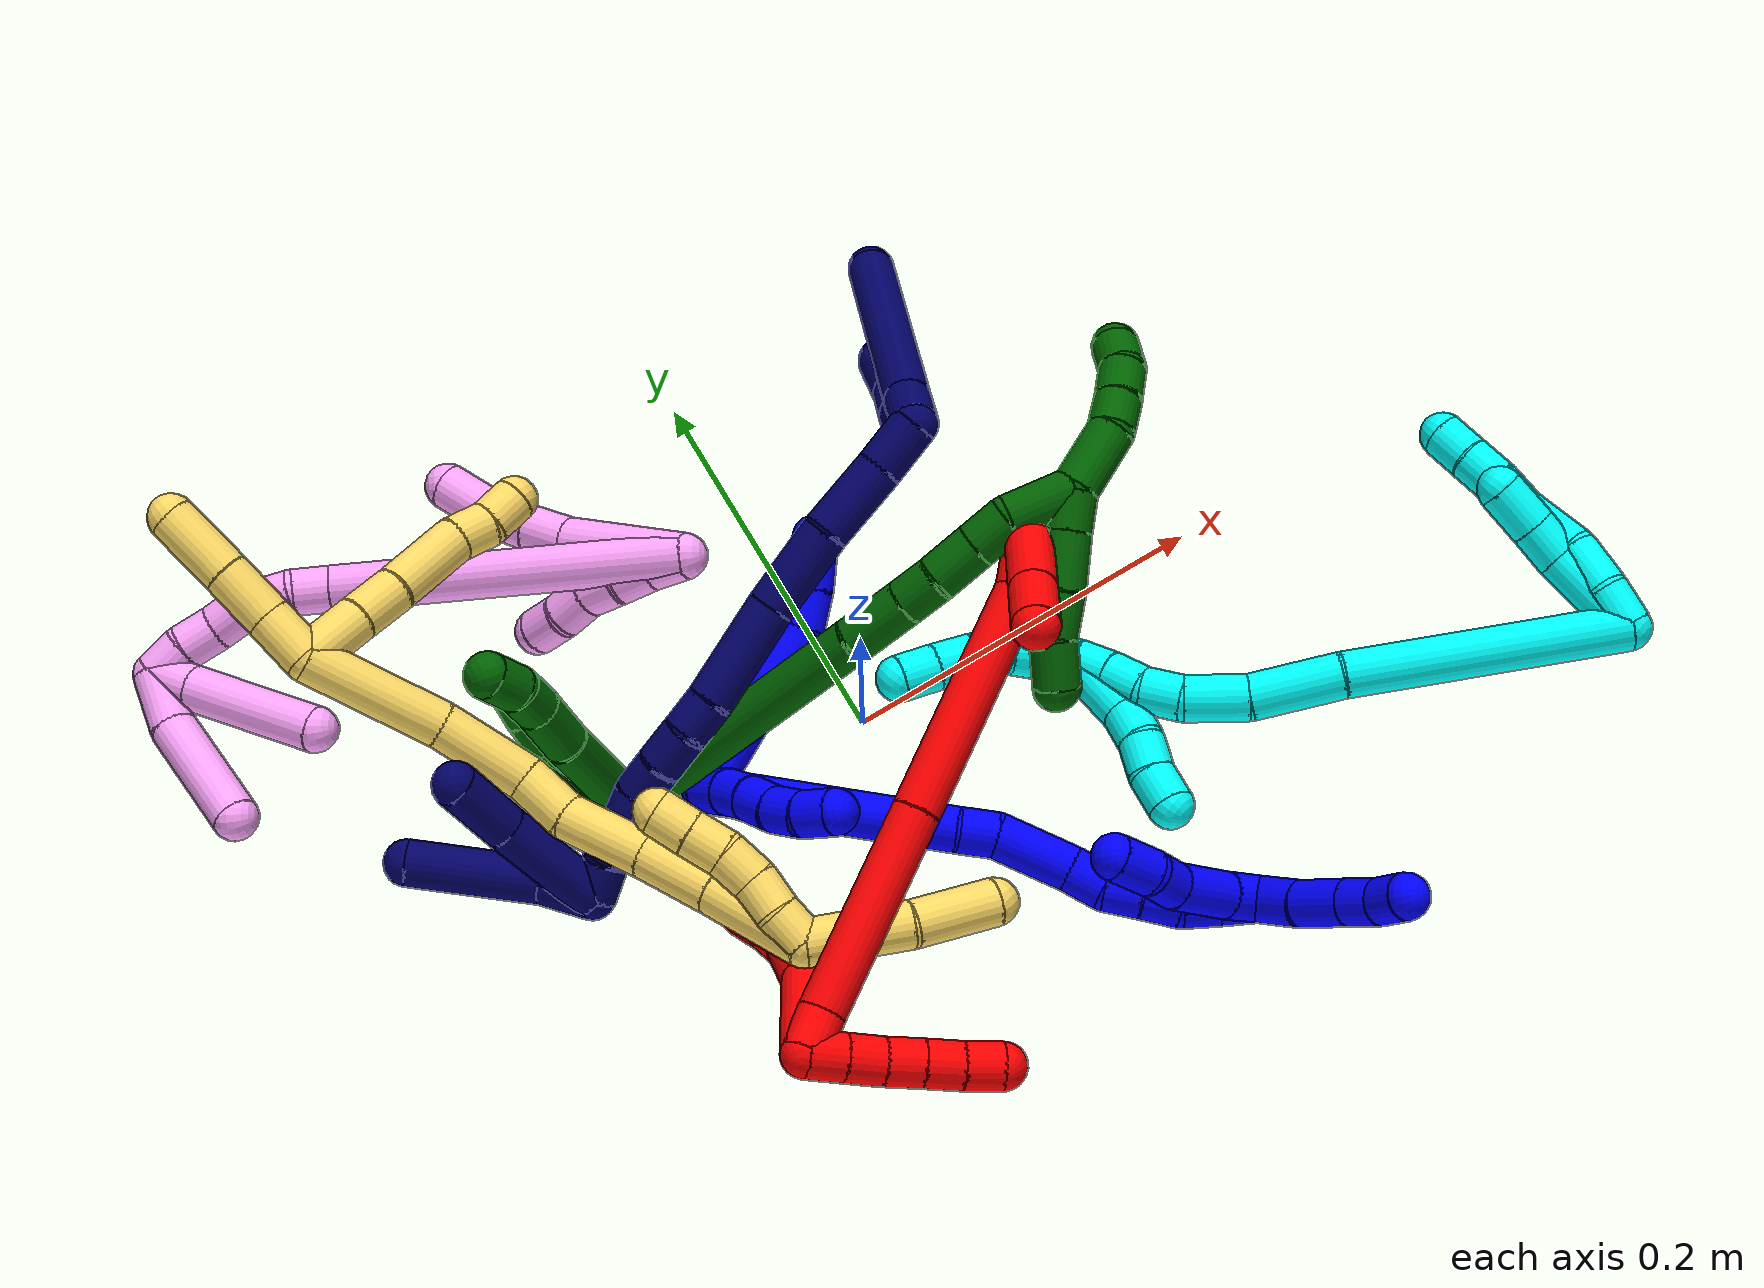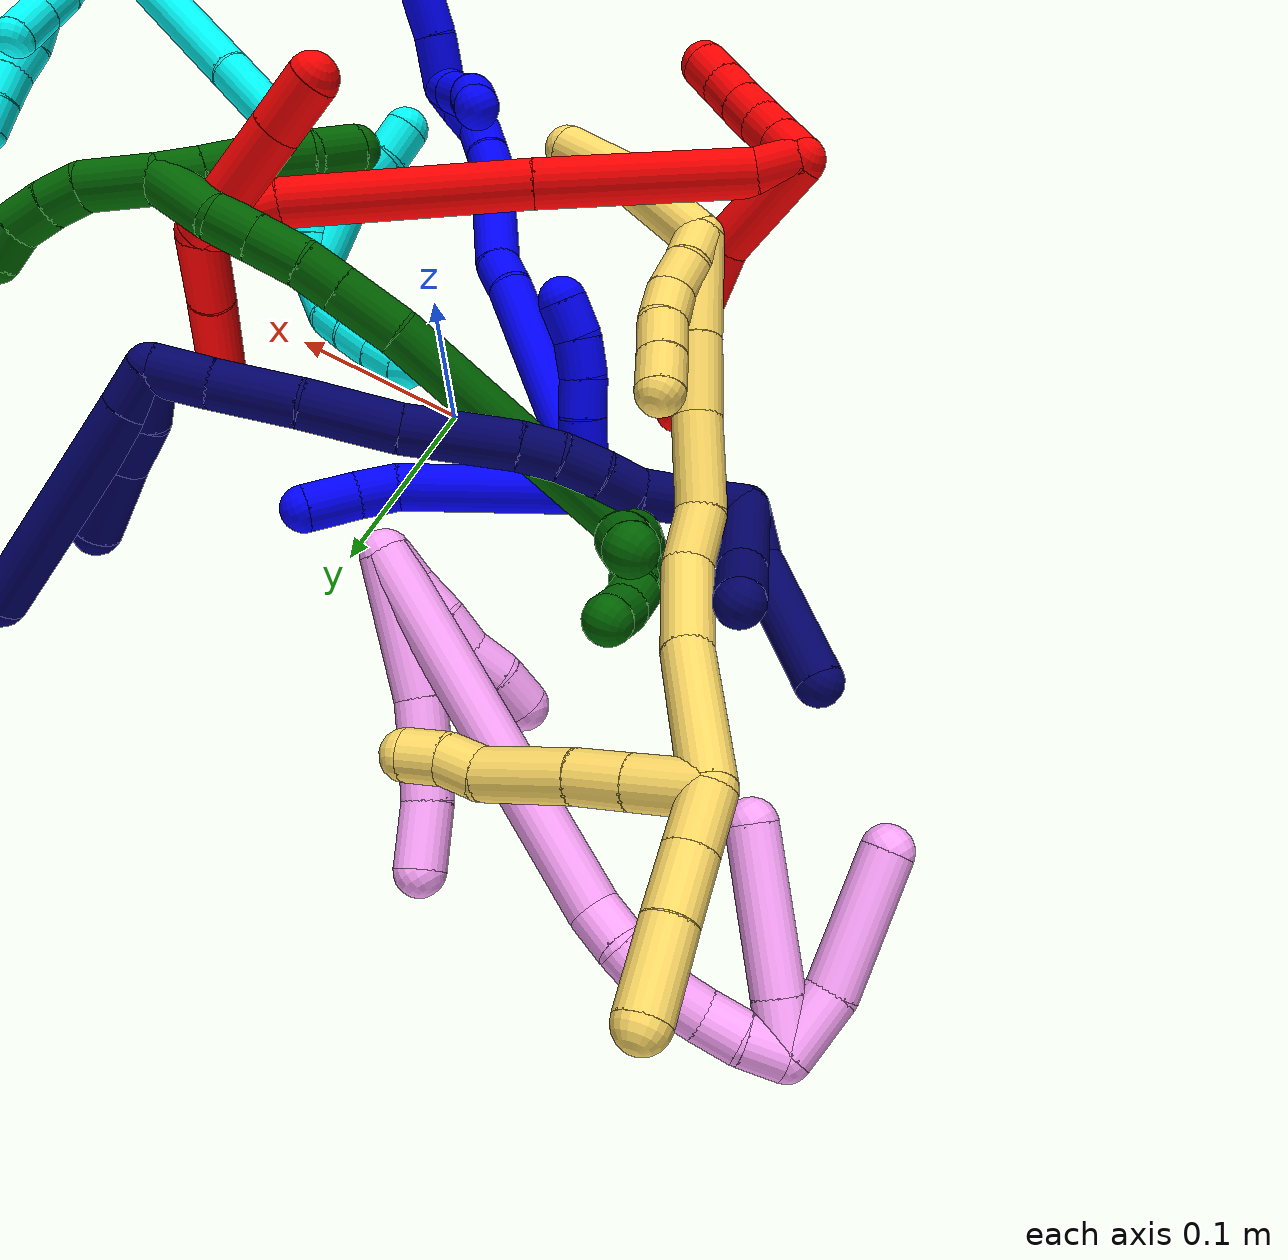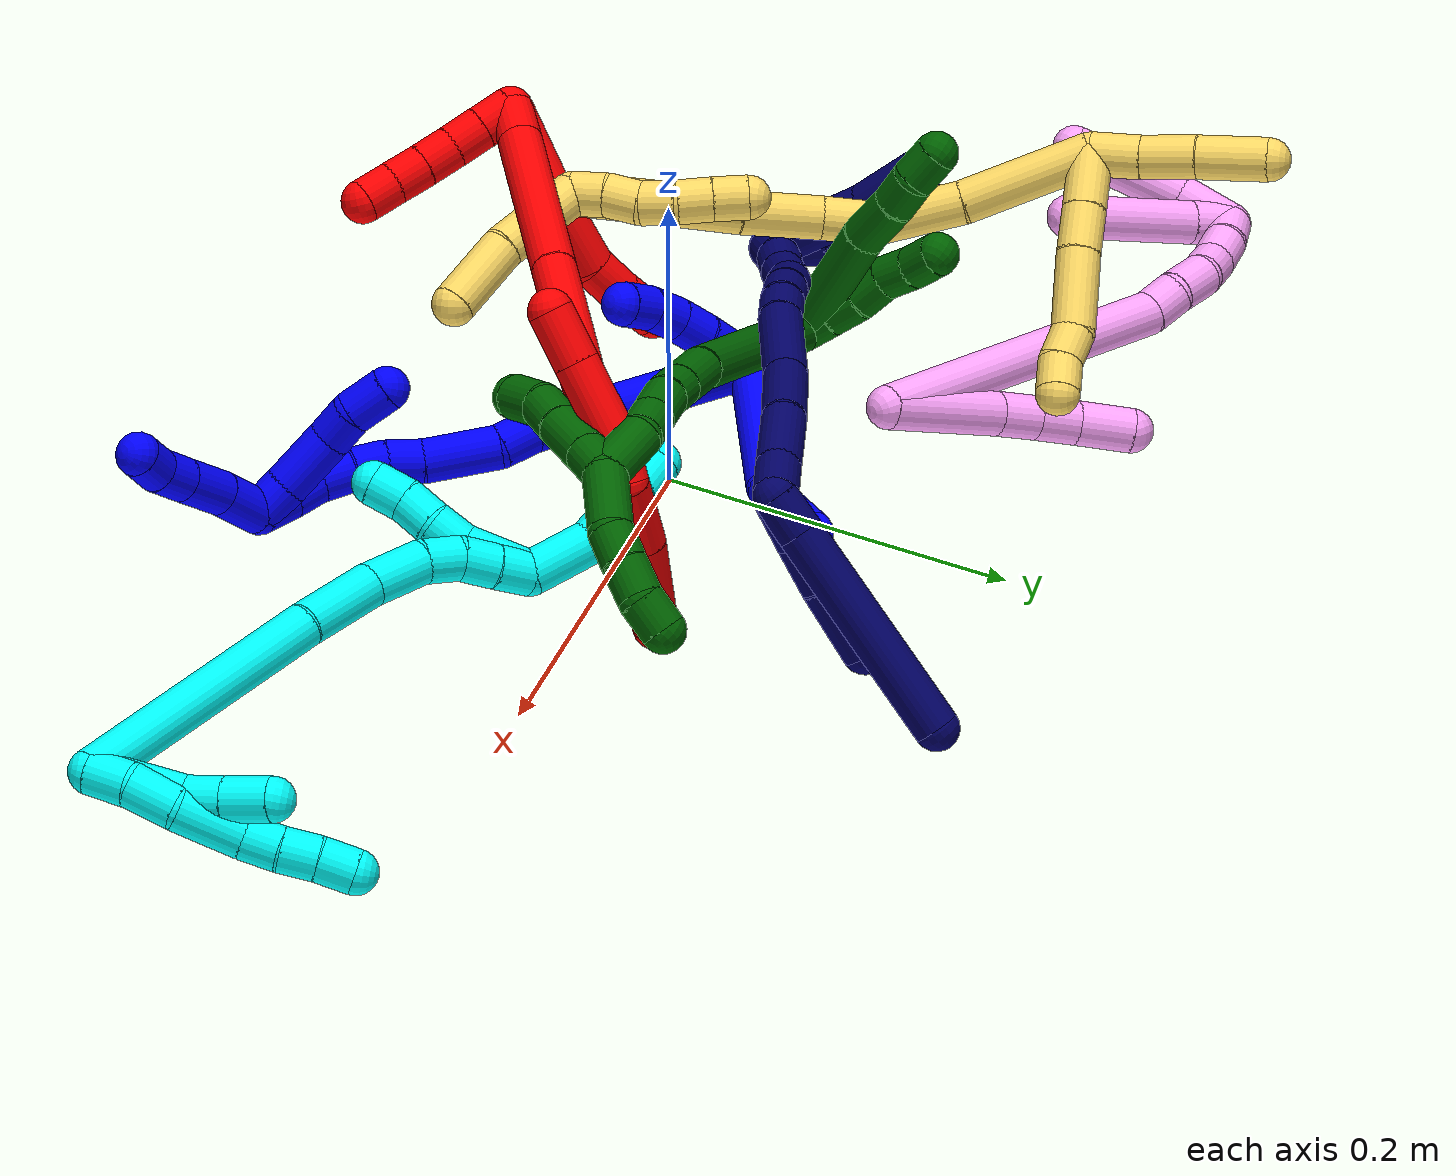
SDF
<sdf version="1.7">
 <world name="default">
  <plugin name="TubeGeneratorPlugin" filename="libtube_generator_plugin.so"/>
  <model name="photoneo_s_sensor">
   <static>1</static>
   <pose>0 0 2 1.57079 1.57079 3.14159</pose>
   <link name="link">
    <inertial><mass>0.1</mass></inertial>
    <sensor name="sensor" type="depth">
     <update_rate>30</update_rate>
     <camera>
      <horizontal_fov>1.22</horizontal_fov>
      <image><width>1920</width><height>1200</height><format>B8G8R8</format></image>
      <clip><near>0.1</near><far>4</far></clip>
      <depth_camera><output>points</output></depth_camera>
     </camera>
     <plugin name="camera_plugin" filename="libgazebo_ros_depth_camera.so">
      <baseline>0.2</baseline>
      <alwaysOn>1</alwaysOn>
      <updateRate>0.0</updateRate>
      <cameraName>camera_ir</cameraName>
      <imageTopicName>/camera/color/image_raw</imageTopicName>
      <cameraInfoTopicName>/camera/color/camera_info</cameraInfoTopicName>
      <depthImageTopicName>/camera/depth/image_raw</depthImageTopicName>
      <depthImageCameraInfoTopicName>/camera/depth/camera_info</depthImageCameraInfoTopicName>
      <pointCloudTopicName>/camera/depth/points</pointCloudTopicName>
      <frameName>fr_optical</frameName>
      <pointCloudCutoff>0.1</pointCloudCutoff>
      <pointCloudCutoffMax>2.0</pointCloudCutoffMax>
      <distortionK1>0</distortionK1>
      <distortionK2>0</distortionK2>
      <distortionK3>0</distortionK3>
      <distortionT1>0</distortionT1>
      <distortionT2>0</distortionT2>
      <CxPrime>0</CxPrime>
      <Cx>0</Cx>
      <Cy>0</Cy>
      <focalLength>0</focalLength>
      <hackBaseline>0</hackBaseline>
     </plugin>
    </sensor>
   </link>
  </model>
  <gravity>0 0 -9.8</gravity>
  <magnetic_field>6e-06 2.3e-05 -4.2e-05</magnetic_field>
  <atmosphere type="adiabatic"/>
  <physics name="default_physics" default="0" type="ode">
   <max_step_size>0.003</max_step_size>
   <real_time_factor>1</real_time_factor>
   <real_time_update_rate>1000</real_time_update_rate>
   <max_contacts>10000</max_contacts>
   <ode>
    <solver>
     <type>quick</type>
     <iters>100</iters>
     <sor>1.3</sor>
     <use_dynamic_moi_rescaling>0</use_dynamic_moi_rescaling>
    </solver>
    <constraints>
     <contact_max_correcting_vel>0</contact_max_correcting_vel>
     <contact_surface_layer>0.001</contact_surface_layer>
     <cfm>0</cfm>
     <erp>0.2</erp>
    </constraints>
   </ode>
  </physics>
  <scene><ambient>0.4 0.4 0.4 1</ambient><background>0.7 0.7 0.7 1</background><shadows>0</shadows></scene>
  <audio><device>default</device></audio>
  <spherical_coordinates>
   <surface_model>EARTH_WGS84</surface_model>
   <latitude_deg>0</latitude_deg>
   <longitude_deg>0</longitude_deg>
   <elevation>0</elevation>
   <heading_deg>0</heading_deg>
  </spherical_coordinates>
  <model name="bin">
   <static>1</static>
   <link name="bottom">
    <collision name="collision-bottom">
     <pose>0 0 -0.01 0 -0 0</pose>
     <geometry><box><size>0.8 0.6 0.02</size></box></geometry>
     <surface>
      <friction><ode><mu>100</mu><mu2>100</mu2></ode></friction>
      <contact><collide_bitmask>65535</collide_bitmask></contact>
     </surface>
    </collision>
   </link>
   <link name="west_wall">
    <collision name="collision-west_wall">
     <pose>-0.41 0 0.1 0 -0 0</pose>
     <geometry><box><size>0.02 0.6 0.2</size></box></geometry>
     <surface>
      <friction><ode><mu>100</mu><mu2>100</mu2></ode></friction>
      <contact><collide_bitmask>65535</collide_bitmask></contact>
     </surface>
    </collision>
   </link>
   <link name="east_wall">
    <collision name="collision-east_wall">
     <pose>0.41 0 0.1 0 -0 0</pose>
     <geometry><box><size>0.02 0.6 0.2</size></box></geometry>
     <surface>
      <friction><ode><mu>100</mu><mu2>100</mu2></ode></friction>
      <contact><collide_bitmask>65535</collide_bitmask></contact>
     </surface>
    </collision>
   </link>
   <link name="south_wall">
    <collision name="collision-south_wall">
     <pose>0 -0.31 0.1 0 -0 0</pose>
     <geometry><box><size>0.8 0.02 0.2</size></box></geometry>
     <surface>
      <friction><ode><mu>100</mu><mu2>100</mu2></ode></friction>
      <contact><collide_bitmask>65535</collide_bitmask></contact>
     </surface>
    </collision>
   </link>
   <link name="north_wall">
    <collision name="collision-north_wall">
     <pose>0 0.31 0.1 0 -0 0</pose>
     <geometry><box><size>0.8 0.02 0.2</size></box></geometry>
     <surface>
      <friction><ode><mu>100</mu><mu2>100</mu2></ode></friction>
      <contact><collide_bitmask>65535</collide_bitmask></contact>
     </surface>
    </collision>
   </link>
  </model>
  <model name="1">
   <static>0</static>
   <link name="1">
    <collision name="collision-cylinder-e_1_2_8">
     <pose>0.033146 0.030264 0.021653 -0.94977 0.727669 -0.386655</pose>
     <geometry><cylinder><radius>0.0125</radius><length>0.099669</length></cylinder></geometry>
     <surface>
      <friction><ode><mu>1.16</mu><mu2>1.16</mu2><slip1>0</slip1><slip2>0</slip2></ode></friction>
      <contact><ode><kp>1e+06</kp><kd>1</kd><max_vel>0</max_vel><min_depth>0.001</min_depth></ode></contact>
     </surface>
    </collision>
    <visual name="visual-cylinder-e_1_2_8">
     <pose>0.033146 0.030264 0.021653 -0.94977 0.727669 -0.386655</pose>
     <geometry><cylinder><radius>0.0125</radius><length>0.099669</length></cylinder></geometry>
     <material><ambient>0 0 1 1</ambient></material>
    </visual>
    <collision name="collision-cylinder-e_2_8_9">
     <pose>0.071846 0.069664 0.046165 -1.26752 0.52565 -0.390408</pose>
     <geometry><cylinder><radius>0.0125</radius><length>0.022133</length></cylinder></geometry>
     <surface>
      <friction><ode><mu>1.16</mu><mu2>1.16</mu2><slip1>0</slip1><slip2>0</slip2></ode></friction>
      <contact><ode><kp>1e+06</kp><kd>1</kd><max_vel>0</max_vel><min_depth>0.001</min_depth></ode></contact>
     </surface>
    </collision>
    <visual name="visual-cylinder-e_2_8_9">
     <pose>0.071846 0.069664 0.046165 -1.26752 0.52565 -0.390408</pose>
     <geometry><cylinder><radius>0.0125</radius><length>0.022133</length></cylinder></geometry>
     <material><ambient>0 0 1 1</ambient></material>
    </visual>
    <collision name="collision-cylinder-e_3_9_6">
     <pose>0.082684 0.091496 0.052132 -1.33065 0.384251 -0.302937</pose>
     <geometry><cylinder><radius>0.0125</radius><length>0.028198</length></cylinder></geometry>
     <surface>
      <friction><ode><mu>1.16</mu><mu2>1.16</mu2><slip1>0</slip1><slip2>0</slip2></ode></friction>
      <contact><ode><kp>1e+06</kp><kd>1</kd><max_vel>0</max_vel><min_depth>0.001</min_depth></ode></contact>
     </surface>
    </collision>
    <visual name="visual-cylinder-e_3_9_6">
     <pose>0.082684 0.091496 0.052132 -1.33065 0.384251 -0.302937</pose>
     <geometry><cylinder><radius>0.0125</radius><length>0.028198</length></cylinder></geometry>
     <material><ambient>0 0 1 1</ambient></material>
    </visual>
    <collision name="collision-cylinder-e_1_2_10">
     <pose>-0.00296 -0.000787 0.00952 0.082534 -0.300454 -0.0125</pose>
     <geometry><cylinder><radius>0.0125</radius><length>0.02</length></cylinder></geometry>
     <surface>
      <friction><ode><mu>1.16</mu><mu2>1.16</mu2><slip1>0</slip1><slip2>0</slip2></ode></friction>
      <contact><ode><kp>1e+06</kp><kd>1</kd><max_vel>0</max_vel><min_depth>0.001</min_depth></ode></contact>
     </surface>
    </collision>
    <visual name="visual-cylinder-e_1_2_10">
     <pose>-0.00296 -0.000787 0.00952 0.082534 -0.300454 -0.0125</pose>
     <geometry><cylinder><radius>0.0125</radius><length>0.02</length></cylinder></geometry>
     <material><ambient>0 0 1 1</ambient></material>
    </visual>
    <collision name="collision-cylinder-e_2_10_11">
     <pose>-0.009303 -0.003633 0.028222 0.22045 -0.345157 -0.038579</pose>
     <geometry><cylinder><radius>0.0125</radius><length>0.02</length></cylinder></geometry>
     <surface>
      <friction><ode><mu>1.16</mu><mu2>1.16</mu2><slip1>0</slip1><slip2>0</slip2></ode></friction>
      <contact><ode><kp>1e+06</kp><kd>1</kd><max_vel>0</max_vel><min_depth>0.001</min_depth></ode></contact>
     </surface>
    </collision>
    <visual name="visual-cylinder-e_2_10_11">
     <pose>-0.009303 -0.003633 0.028222 0.22045 -0.345157 -0.038579</pose>
     <geometry><cylinder><radius>0.0125</radius><length>0.02</length></cylinder></geometry>
     <material><ambient>0 0 1 1</ambient></material>
    </visual>
    <collision name="collision-cylinder-e_3_11_12">
     <pose>-0.01586 -0.008845 0.046347 0.339108 -0.323024 -0.055772</pose>
     <geometry><cylinder><radius>0.0125</radius><length>0.02</length></cylinder></geometry>
     <surface>
      <friction><ode><mu>1.16</mu><mu2>1.16</mu2><slip1>0</slip1><slip2>0</slip2></ode></friction>
      <contact><ode><kp>1e+06</kp><kd>1</kd><max_vel>0</max_vel><min_depth>0.001</min_depth></ode></contact>
     </surface>
    </collision>
    <visual name="visual-cylinder-e_3_11_12">
     <pose>-0.01586 -0.008845 0.046347 0.339108 -0.323024 -0.055772</pose>
     <geometry><cylinder><radius>0.0125</radius><length>0.02</length></cylinder></geometry>
     <material><ambient>0 0 1 1</ambient></material>
    </visual>
    <collision name="collision-cylinder-e_4_12_13">
     <pose>-0.020894 -0.014074 0.064894 0.212731 -0.18707 -0.020031</pose>
     <geometry><cylinder><radius>0.0125</radius><length>0.02</length></cylinder></geometry>
     <surface>
      <friction><ode><mu>1.16</mu><mu2>1.16</mu2><slip1>0</slip1><slip2>0</slip2></ode></friction>
      <contact><ode><kp>1e+06</kp><kd>1</kd><max_vel>0</max_vel><min_depth>0.001</min_depth></ode></contact>
     </surface>
    </collision>
    <visual name="visual-cylinder-e_4_12_13">
     <pose>-0.020894 -0.014074 0.064894 0.212731 -0.18707 -0.020031</pose>
     <geometry><cylinder><radius>0.0125</radius><length>0.02</length></cylinder></geometry>
     <material><ambient>0 0 1 1</ambient></material>
    </visual>
    <collision name="collision-cylinder-e_5_13_5">
     <pose>-0.022626 -0.016955 0.084464 0.080828 0.012779 0.000517</pose>
     <geometry><cylinder><radius>0.0125</radius><length>0.02</length></cylinder></geometry>
     <surface>
      <friction><ode><mu>1.16</mu><mu2>1.16</mu2><slip1>0</slip1><slip2>0</slip2></ode></friction>
      <contact><ode><kp>1e+06</kp><kd>1</kd><max_vel>0</max_vel><min_depth>0.001</min_depth></ode></contact>
     </surface>
    </collision>
    <visual name="visual-cylinder-e_5_13_5">
     <pose>-0.022626 -0.016955 0.084464 0.080828 0.012779 0.000517</pose>
     <geometry><cylinder><radius>0.0125</radius><length>0.02</length></cylinder></geometry>
     <material><ambient>0 0 1 1</ambient></material>
    </visual>
    <collision name="collision-cylinder-e_1_2_14">
     <pose>0.02678 -0.02902 0.054832 0.486771 0.407507 0.102521</pose>
     <geometry><cylinder><radius>0.0125</radius><length>0.135141</length></cylinder></geometry>
     <surface>
      <friction><ode><mu>1.16</mu><mu2>1.16</mu2><slip1>0</slip1><slip2>0</slip2></ode></friction>
      <contact><ode><kp>1e+06</kp><kd>1</kd><max_vel>0</max_vel><min_depth>0.001</min_depth></ode></contact>
     </surface>
    </collision>
    <visual name="visual-cylinder-e_1_2_14">
     <pose>0.02678 -0.02902 0.054832 0.486771 0.407507 0.102521</pose>
     <geometry><cylinder><radius>0.0125</radius><length>0.135141</length></cylinder></geometry>
     <material><ambient>0 0 1 1</ambient></material>
    </visual>
    <collision name="collision-cylinder-e_2_14_15">
     <pose>0.059156 -0.062677 0.116992 0.564221 0.572997 0.170363</pose>
     <geometry><cylinder><radius>0.0125</radius><length>0.020644</length></cylinder></geometry>
     <surface>
      <friction><ode><mu>1.16</mu><mu2>1.16</mu2><slip1>0</slip1><slip2>0</slip2></ode></friction>
      <contact><ode><kp>1e+06</kp><kd>1</kd><max_vel>0</max_vel><min_depth>0.001</min_depth></ode></contact>
     </surface>
    </collision>
    <visual name="visual-cylinder-e_2_14_15">
     <pose>0.059156 -0.062677 0.116992 0.564221 0.572997 0.170363</pose>
     <geometry><cylinder><radius>0.0125</radius><length>0.020644</length></cylinder></geometry>
     <material><ambient>0 0 1 1</ambient></material>
    </visual>
    <collision name="collision-cylinder-e_3_15_16">
     <pose>0.071607 -0.081455 0.138984 0.767231 0.324615 0.131989</pose>
     <geometry><cylinder><radius>0.0125</radius><length>0.042985</length></cylinder></geometry>
     <surface>
      <friction><ode><mu>1.16</mu><mu2>1.16</mu2><slip1>0</slip1><slip2>0</slip2></ode></friction>
      <contact><ode><kp>1e+06</kp><kd>1</kd><max_vel>0</max_vel><min_depth>0.001</min_depth></ode></contact>
     </surface>
    </collision>
    <visual name="visual-cylinder-e_3_15_16">
     <pose>0.071607 -0.081455 0.138984 0.767231 0.324615 0.131989</pose>
     <geometry><cylinder><radius>0.0125</radius><length>0.042985</length></cylinder></geometry>
     <material><ambient>0 0 1 1</ambient></material>
    </visual>
    <collision name="collision-cylinder-e_4_16_17">
     <pose>0.080065 -0.102558 0.1611 0.751473 0.155976 0.061634</pose>
     <geometry><cylinder><radius>0.0125</radius><length>0.020649</length></cylinder></geometry>
     <surface>
      <friction><ode><mu>1.16</mu><mu2>1.16</mu2><slip1>0</slip1><slip2>0</slip2></ode></friction>
      <contact><ode><kp>1e+06</kp><kd>1</kd><max_vel>0</max_vel><min_depth>0.001</min_depth></ode></contact>
     </surface>
    </collision>
    <visual name="visual-cylinder-e_4_16_17">
     <pose>0.080065 -0.102558 0.1611 0.751473 0.155976 0.061634</pose>
     <geometry><cylinder><radius>0.0125</radius><length>0.020649</length></cylinder></geometry>
     <material><ambient>0 0 1 1</ambient></material>
    </visual>
    <collision name="collision-cylinder-e_5_17_18">
     <pose>0.085135 -0.114209 0.176724 0.520809 0.352553 0.094854</pose>
     <geometry><cylinder><radius>0.0125</radius><length>0.020076</length></cylinder></geometry>
     <surface>
      <friction><ode><mu>1.16</mu><mu2>1.16</mu2><slip1>0</slip1><slip2>0</slip2></ode></friction>
      <contact><ode><kp>1e+06</kp><kd>1</kd><max_vel>0</max_vel><min_depth>0.001</min_depth></ode></contact>
     </surface>
    </collision>
    <visual name="visual-cylinder-e_5_17_18">
     <pose>0.085135 -0.114209 0.176724 0.520809 0.352553 0.094854</pose>
     <geometry><cylinder><radius>0.0125</radius><length>0.020076</length></cylinder></geometry>
     <material><ambient>0 0 1 1</ambient></material>
    </visual>
    <collision name="collision-cylinder-e_6_18_19">
     <pose>0.092916 -0.12405 0.192466 0.597672 0.440313 0.137661</pose>
     <geometry><cylinder><radius>0.0125</radius><length>0.020248</length></cylinder></geometry>
     <surface>
      <friction><ode><mu>1.16</mu><mu2>1.16</mu2><slip1>0</slip1><slip2>0</slip2></ode></friction>
      <contact><ode><kp>1e+06</kp><kd>1</kd><max_vel>0</max_vel><min_depth>0.001</min_depth></ode></contact>
     </surface>
    </collision>
    <visual name="visual-cylinder-e_6_18_19">
     <pose>0.092916 -0.12405 0.192466 0.597672 0.440313 0.137661</pose>
     <geometry><cylinder><radius>0.0125</radius><length>0.020248</length></cylinder></geometry>
     <material><ambient>0 0 1 1</ambient></material>
    </visual>
    <collision name="collision-cylinder-e_7_19_20">
     <pose>0.103006 -0.131737 0.207896 0.31179 0.610299 0.098933</pose>
     <geometry><cylinder><radius>0.0125</radius><length>0.020153</length></cylinder></geometry>
     <surface>
      <friction><ode><mu>1.16</mu><mu2>1.16</mu2><slip1>0</slip1><slip2>0</slip2></ode></friction>
      <contact><ode><kp>1e+06</kp><kd>1</kd><max_vel>0</max_vel><min_depth>0.001</min_depth></ode></contact>
     </surface>
    </collision>
    <visual name="visual-cylinder-e_7_19_20">
     <pose>0.103006 -0.131737 0.207896 0.31179 0.610299 0.098933</pose>
     <geometry><cylinder><radius>0.0125</radius><length>0.020153</length></cylinder></geometry>
     <material><ambient>0 0 1 1</ambient></material>
    </visual>
    <collision name="collision-cylinder-e_8_20_1">
     <pose>0.113739 -0.136287 0.224264 0.232769 0.515757 0.061652</pose>
     <geometry><cylinder><radius>0.0125</radius><length>0.020104</length></cylinder></geometry>
     <surface>
      <friction><ode><mu>1.16</mu><mu2>1.16</mu2><slip1>0</slip1><slip2>0</slip2></ode></friction>
      <contact><ode><kp>1e+06</kp><kd>1</kd><max_vel>0</max_vel><min_depth>0.001</min_depth></ode></contact>
     </surface>
    </collision>
    <visual name="visual-cylinder-e_8_20_1">
     <pose>0.113739 -0.136287 0.224264 0.232769 0.515757 0.061652</pose>
     <geometry><cylinder><radius>0.0125</radius><length>0.020104</length></cylinder></geometry>
     <material><ambient>0 0 1 1</ambient></material>
    </visual>
    <collision name="collision-cylinder-e_1_1_21">
     <pose>0.114868 -0.140026 0.247027 0.120237 -0.26055 -0.015772</pose>
     <geometry><cylinder><radius>0.0125</radius><length>0.02972</length></cylinder></geometry>
     <surface>
      <friction><ode><mu>1.16</mu><mu2>1.16</mu2><slip1>0</slip1><slip2>0</slip2></ode></friction>
      <contact><ode><kp>1e+06</kp><kd>1</kd><max_vel>0</max_vel><min_depth>0.001</min_depth></ode></contact>
     </surface>
    </collision>
    <visual name="visual-cylinder-e_1_1_21">
     <pose>0.114868 -0.140026 0.247027 0.120237 -0.26055 -0.015772</pose>
     <geometry><cylinder><radius>0.0125</radius><length>0.02972</length></cylinder></geometry>
     <material><ambient>0 0 1 1</ambient></material>
    </visual>
    <collision name="collision-cylinder-e_2_21_22">
     <pose>0.108812 -0.142399 0.276079 0.043921 -0.149337 -0.003286</pose>
     <geometry><cylinder><radius>0.0125</radius><length>0.029956</length></cylinder></geometry>
     <surface>
      <friction><ode><mu>1.16</mu><mu2>1.16</mu2><slip1>0</slip1><slip2>0</slip2></ode></friction>
      <contact><ode><kp>1e+06</kp><kd>1</kd><max_vel>0</max_vel><min_depth>0.001</min_depth></ode></contact>
     </surface>
    </collision>
    <visual name="visual-cylinder-e_2_21_22">
     <pose>0.108812 -0.142399 0.276079 0.043921 -0.149337 -0.003286</pose>
     <geometry><cylinder><radius>0.0125</radius><length>0.029956</length></cylinder></geometry>
     <material><ambient>0 0 1 1</ambient></material>
    </visual>
    <collision name="collision-cylinder-e_3_22_23">
     <pose>0.104968 -0.14348 0.30074 0.043682 -0.162185 -0.003551</pose>
     <geometry><cylinder><radius>0.0125</radius><length>0.02001</length></cylinder></geometry>
     <surface>
      <friction><ode><mu>1.16</mu><mu2>1.16</mu2><slip1>0</slip1><slip2>0</slip2></ode></friction>
      <contact><ode><kp>1e+06</kp><kd>1</kd><max_vel>0</max_vel><min_depth>0.001</min_depth></ode></contact>
     </surface>
    </collision>
    <visual name="visual-cylinder-e_3_22_23">
     <pose>0.104968 -0.14348 0.30074 0.043682 -0.162185 -0.003551</pose>
     <geometry><cylinder><radius>0.0125</radius><length>0.02001</length></cylinder></geometry>
     <material><ambient>0 0 1 1</ambient></material>
    </visual>
    <collision name="collision-cylinder-e_4_23_4">
     <pose>0.099964 -0.14249 0.320073 -0.149023 -0.340109 0.025635</pose>
     <geometry><cylinder><radius>0.0125</radius><length>0.020314</length></cylinder></geometry>
     <surface>
      <friction><ode><mu>1.16</mu><mu2>1.16</mu2><slip1>0</slip1><slip2>0</slip2></ode></friction>
      <contact><ode><kp>1e+06</kp><kd>1</kd><max_vel>0</max_vel><min_depth>0.001</min_depth></ode></contact>
     </surface>
    </collision>
    <visual name="visual-cylinder-e_4_23_4">
     <pose>0.099964 -0.14249 0.320073 -0.149023 -0.340109 0.025635</pose>
     <geometry><cylinder><radius>0.0125</radius><length>0.020314</length></cylinder></geometry>
     <material><ambient>0 0 1 1</ambient></material>
    </visual>
    <collision name="collision-cylinder-e_1_1_24">
     <pose>0.110498 -0.133565 0.228915 -2.25401 -0.930314 1.62495</pose>
     <geometry><cylinder><radius>0.0125</radius><length>0.020449</length></cylinder></geometry>
     <surface>
      <friction><ode><mu>1.16</mu><mu2>1.16</mu2><slip1>0</slip1><slip2>0</slip2></ode></friction>
      <contact><ode><kp>1e+06</kp><kd>1</kd><max_vel>0</max_vel><min_depth>0.001</min_depth></ode></contact>
     </surface>
    </collision>
    <visual name="visual-cylinder-e_1_1_24">
     <pose>0.110498 -0.133565 0.228915 -2.25401 -0.930314 1.62495</pose>
     <geometry><cylinder><radius>0.0125</radius><length>0.020449</length></cylinder></geometry>
     <material><ambient>0 0 1 1</ambient></material>
    </visual>
    <collision name="collision-cylinder-e_2_24_25">
     <pose>0.087867 -0.119971 0.219846 -2.10282 -0.952091 1.4676</pose>
     <geometry><cylinder><radius>0.0125</radius><length>0.035434</length></cylinder></geometry>
     <surface>
      <friction><ode><mu>1.16</mu><mu2>1.16</mu2><slip1>0</slip1><slip2>0</slip2></ode></friction>
      <contact><ode><kp>1e+06</kp><kd>1</kd><max_vel>0</max_vel><min_depth>0.001</min_depth></ode></contact>
     </surface>
    </collision>
    <visual name="visual-cylinder-e_2_24_25">
     <pose>0.087867 -0.119971 0.219846 -2.10282 -0.952091 1.4676</pose>
     <geometry><cylinder><radius>0.0125</radius><length>0.035434</length></cylinder></geometry>
     <material><ambient>0 0 1 1</ambient></material>
    </visual>
    <collision name="collision-cylinder-e_3_25_26">
     <pose>0.065689 -0.104534 0.214201 -1.63629 -0.865373 0.916325</pose>
     <geometry><cylinder><radius>0.0125</radius><length>0.020347</length></cylinder></geometry>
     <surface>
      <friction><ode><mu>1.16</mu><mu2>1.16</mu2><slip1>0</slip1><slip2>0</slip2></ode></friction>
      <contact><ode><kp>1e+06</kp><kd>1</kd><max_vel>0</max_vel><min_depth>0.001</min_depth></ode></contact>
     </surface>
    </collision>
    <visual name="visual-cylinder-e_3_25_26">
     <pose>0.065689 -0.104534 0.214201 -1.63629 -0.865373 0.916325</pose>
     <geometry><cylinder><radius>0.0125</radius><length>0.020347</length></cylinder></geometry>
     <material><ambient>0 0 1 1</ambient></material>
    </visual>
    <collision name="collision-cylinder-e_4_26_3">
     <pose>0.050083 -0.090036 0.209672 -2.04846 -0.722687 1.11173</pose>
     <geometry><cylinder><radius>0.0125</radius><length>0.02377</length></cylinder></geometry>
     <surface>
      <friction><ode><mu>1.16</mu><mu2>1.16</mu2><slip1>0</slip1><slip2>0</slip2></ode></friction>
      <contact><ode><kp>1e+06</kp><kd>1</kd><max_vel>0</max_vel><min_depth>0.001</min_depth></ode></contact>
     </surface>
    </collision>
    <visual name="visual-cylinder-e_4_26_3">
     <pose>0.050083 -0.090036 0.209672 -2.04846 -0.722687 1.11173</pose>
     <geometry><cylinder><radius>0.0125</radius><length>0.02377</length></cylinder></geometry>
     <material><ambient>0 0 1 1</ambient></material>
    </visual>
    <collision name="collision-sphere-3">
     <pose>0.042222 -0.082119 0.205574 0 -0 0</pose>
     <geometry><sphere><radius>0.0125</radius></sphere></geometry>
     <surface>
      <friction><ode><mu>1.16</mu><mu2>1.16</mu2><slip1>0</slip1><slip2>0</slip2></ode></friction>
      <contact><ode><kp>1e+06</kp><kd>1</kd><max_vel>0</max_vel><min_depth>0.001</min_depth></ode></contact>
     </surface>
    </collision>
    <visual name="visual-sphere-3">
     <pose>0.042222 -0.082119 0.205574 0 -0 0</pose>
     <geometry><sphere><radius>0.0125</radius></sphere></geometry>
     <material><ambient>0 0 1 1</ambient></material>
    </visual>
    <collision name="collision-sphere-26">
     <pose>0.057943 -0.097952 0.21377 0 -0 0</pose>
     <geometry><sphere><radius>0.0125</radius></sphere></geometry>
     <surface>
      <friction><ode><mu>1.16</mu><mu2>1.16</mu2><slip1>0</slip1><slip2>0</slip2></ode></friction>
      <contact><ode><kp>1e+06</kp><kd>1</kd><max_vel>0</max_vel><min_depth>0.001</min_depth></ode></contact>
     </surface>
    </collision>
    <visual name="visual-sphere-26">
     <pose>0.057943 -0.097952 0.21377 0 -0 0</pose>
     <geometry><sphere><radius>0.0125</radius></sphere></geometry>
     <material><ambient>0 0 1 1</ambient></material>
    </visual>
    <collision name="collision-sphere-25">
     <pose>0.073434 -0.111116 0.214633 0 -0 0</pose>
     <geometry><sphere><radius>0.0125</radius></sphere></geometry>
     <surface>
      <friction><ode><mu>1.16</mu><mu2>1.16</mu2><slip1>0</slip1><slip2>0</slip2></ode></friction>
      <contact><ode><kp>1e+06</kp><kd>1</kd><max_vel>0</max_vel><min_depth>0.001</min_depth></ode></contact>
     </surface>
    </collision>
    <visual name="visual-sphere-25">
     <pose>0.073434 -0.111116 0.214633 0 -0 0</pose>
     <geometry><sphere><radius>0.0125</radius></sphere></geometry>
     <material><ambient>0 0 1 1</ambient></material>
    </visual>
    <collision name="collision-sphere-24">
     <pose>0.1023 -0.128827 0.225058 0 -0 0</pose>
     <geometry><sphere><radius>0.0125</radius></sphere></geometry>
     <surface>
      <friction><ode><mu>1.16</mu><mu2>1.16</mu2><slip1>0</slip1><slip2>0</slip2></ode></friction>
      <contact><ode><kp>1e+06</kp><kd>1</kd><max_vel>0</max_vel><min_depth>0.001</min_depth></ode></contact>
     </surface>
    </collision>
    <visual name="visual-sphere-24">
     <pose>0.1023 -0.128827 0.225058 0 -0 0</pose>
     <geometry><sphere><radius>0.0125</radius></sphere></geometry>
     <material><ambient>0 0 1 1</ambient></material>
    </visual>
    <collision name="collision-sphere-4">
     <pose>0.096575 -0.141068 0.329543 0 -0 0</pose>
     <geometry><sphere><radius>0.0125</radius></sphere></geometry>
     <surface>
      <friction><ode><mu>1.16</mu><mu2>1.16</mu2><slip1>0</slip1><slip2>0</slip2></ode></friction>
      <contact><ode><kp>1e+06</kp><kd>1</kd><max_vel>0</max_vel><min_depth>0.001</min_depth></ode></contact>
     </surface>
    </collision>
    <visual name="visual-sphere-4">
     <pose>0.096575 -0.141068 0.329543 0 -0 0</pose>
     <geometry><sphere><radius>0.0125</radius></sphere></geometry>
     <material><ambient>0 0 1 1</ambient></material>
    </visual>
    <collision name="collision-sphere-23">
     <pose>0.103352 -0.143911 0.310604 0 -0 0</pose>
     <geometry><sphere><radius>0.0125</radius></sphere></geometry>
     <surface>
      <friction><ode><mu>1.16</mu><mu2>1.16</mu2><slip1>0</slip1><slip2>0</slip2></ode></friction>
      <contact><ode><kp>1e+06</kp><kd>1</kd><max_vel>0</max_vel><min_depth>0.001</min_depth></ode></contact>
     </surface>
    </collision>
    <visual name="visual-sphere-23">
     <pose>0.103352 -0.143911 0.310604 0 -0 0</pose>
     <geometry><sphere><radius>0.0125</radius></sphere></geometry>
     <material><ambient>0 0 1 1</ambient></material>
    </visual>
    <collision name="collision-sphere-22">
     <pose>0.106583 -0.143049 0.290876 0 -0 0</pose>
     <geometry><sphere><radius>0.0125</radius></sphere></geometry>
     <surface>
      <friction><ode><mu>1.16</mu><mu2>1.16</mu2><slip1>0</slip1><slip2>0</slip2></ode></friction>
      <contact><ode><kp>1e+06</kp><kd>1</kd><max_vel>0</max_vel><min_depth>0.001</min_depth></ode></contact>
     </surface>
    </collision>
    <visual name="visual-sphere-22">
     <pose>0.106583 -0.143049 0.290876 0 -0 0</pose>
     <geometry><sphere><radius>0.0125</radius></sphere></geometry>
     <material><ambient>0 0 1 1</ambient></material>
    </visual>
    <collision name="collision-sphere-21">
     <pose>0.11104 -0.141748 0.261282 0 -0 0</pose>
     <geometry><sphere><radius>0.0125</radius></sphere></geometry>
     <surface>
      <friction><ode><mu>1.16</mu><mu2>1.16</mu2><slip1>0</slip1><slip2>0</slip2></ode></friction>
      <contact><ode><kp>1e+06</kp><kd>1</kd><max_vel>0</max_vel><min_depth>0.001</min_depth></ode></contact>
     </surface>
    </collision>
    <visual name="visual-sphere-21">
     <pose>0.11104 -0.141748 0.261282 0 -0 0</pose>
     <geometry><sphere><radius>0.0125</radius></sphere></geometry>
     <material><ambient>0 0 1 1</ambient></material>
    </visual>
    <collision name="collision-sphere-1">
     <pose>0.118696 -0.138304 0.232772 0 -0 0</pose>
     <geometry><sphere><radius>0.0125</radius></sphere></geometry>
     <surface>
      <friction><ode><mu>1.16</mu><mu2>1.16</mu2><slip1>0</slip1><slip2>0</slip2></ode></friction>
      <contact><ode><kp>1e+06</kp><kd>1</kd><max_vel>0</max_vel><min_depth>0.001</min_depth></ode></contact>
     </surface>
    </collision>
    <visual name="visual-sphere-1">
     <pose>0.118696 -0.138304 0.232772 0 -0 0</pose>
     <geometry><sphere><radius>0.0125</radius></sphere></geometry>
     <material><ambient>0 0 1 1</ambient></material>
    </visual>
    <collision name="collision-sphere-11">
     <pose>-0.012686 -0.00569 0.037404 0 -0 0</pose>
     <geometry><sphere><radius>0.0125</radius></sphere></geometry>
     <surface>
      <friction><ode><mu>1.16</mu><mu2>1.16</mu2><slip1>0</slip1><slip2>0</slip2></ode></friction>
      <contact><ode><kp>1e+06</kp><kd>1</kd><max_vel>0</max_vel><min_depth>0.001</min_depth></ode></contact>
     </surface>
    </collision>
    <visual name="visual-sphere-11">
     <pose>-0.012686 -0.00569 0.037404 0 -0 0</pose>
     <geometry><sphere><radius>0.0125</radius></sphere></geometry>
     <material><ambient>0 0 1 1</ambient></material>
    </visual>
    <collision name="collision-sphere-10">
     <pose>-0.005919 -0.001575 0.019039 0 -0 0</pose>
     <geometry><sphere><radius>0.0125</radius></sphere></geometry>
     <surface>
      <friction><ode><mu>1.16</mu><mu2>1.16</mu2><slip1>0</slip1><slip2>0</slip2></ode></friction>
      <contact><ode><kp>1e+06</kp><kd>1</kd><max_vel>0</max_vel><min_depth>0.001</min_depth></ode></contact>
     </surface>
    </collision>
    <visual name="visual-sphere-10">
     <pose>-0.005919 -0.001575 0.019039 0 -0 0</pose>
     <geometry><sphere><radius>0.0125</radius></sphere></geometry>
     <material><ambient>0 0 1 1</ambient></material>
    </visual>
    <collision name="collision-sphere-6">
     <pose>0.087969 0.104192 0.055241 0 -0 0</pose>
     <geometry><sphere><radius>0.0125</radius></sphere></geometry>
     <surface>
      <friction><ode><mu>1.16</mu><mu2>1.16</mu2><slip1>0</slip1><slip2>0</slip2></ode></friction>
      <contact><ode><kp>1e+06</kp><kd>1</kd><max_vel>0</max_vel><min_depth>0.001</min_depth></ode></contact>
     </surface>
    </collision>
    <visual name="visual-sphere-6">
     <pose>0.087969 0.104192 0.055241 0 -0 0</pose>
     <geometry><sphere><radius>0.0125</radius></sphere></geometry>
     <material><ambient>0 0 1 1</ambient></material>
    </visual>
    <collision name="collision-sphere-9">
     <pose>0.077398 0.0788 0.049023 0 -0 0</pose>
     <geometry><sphere><radius>0.0125</radius></sphere></geometry>
     <surface>
      <friction><ode><mu>1.16</mu><mu2>1.16</mu2><slip1>0</slip1><slip2>0</slip2></ode></friction>
      <contact><ode><kp>1e+06</kp><kd>1</kd><max_vel>0</max_vel><min_depth>0.001</min_depth></ode></contact>
     </surface>
    </collision>
    <visual name="visual-sphere-9">
     <pose>0.077398 0.0788 0.049023 0 -0 0</pose>
     <geometry><sphere><radius>0.0125</radius></sphere></geometry>
     <material><ambient>0 0 1 1</ambient></material>
    </visual>
    <collision name="collision-sphere-2">
     <geometry><sphere><radius>0.0125</radius></sphere></geometry>
     <surface>
      <friction><ode><mu>1.16</mu><mu2>1.16</mu2><slip1>0</slip1><slip2>0</slip2></ode></friction>
      <contact><ode><kp>1e+06</kp><kd>1</kd><max_vel>0</max_vel><min_depth>0.001</min_depth></ode></contact>
     </surface>
    </collision>
    <visual name="visual-sphere-2">
     <geometry><sphere><radius>0.0125</radius></sphere></geometry>
     <material><ambient>0 0 1 1</ambient></material>
    </visual>
    <collision name="collision-sphere-19">
     <pose>0.097231 -0.129203 0.200037 0 -0 0</pose>
     <geometry><sphere><radius>0.0125</radius></sphere></geometry>
     <surface>
      <friction><ode><mu>1.16</mu><mu2>1.16</mu2><slip1>0</slip1><slip2>0</slip2></ode></friction>
      <contact><ode><kp>1e+06</kp><kd>1</kd><max_vel>0</max_vel><min_depth>0.001</min_depth></ode></contact>
     </surface>
    </collision>
    <visual name="visual-sphere-19">
     <pose>0.097231 -0.129203 0.200037 0 -0 0</pose>
     <geometry><sphere><radius>0.0125</radius></sphere></geometry>
     <material><ambient>0 0 1 1</ambient></material>
    </visual>
    <collision name="collision-sphere-8">
     <pose>0.066293 0.060529 0.043306 0 -0 0</pose>
     <geometry><sphere><radius>0.0125</radius></sphere></geometry>
     <surface>
      <friction><ode><mu>1.16</mu><mu2>1.16</mu2><slip1>0</slip1><slip2>0</slip2></ode></friction>
      <contact><ode><kp>1e+06</kp><kd>1</kd><max_vel>0</max_vel><min_depth>0.001</min_depth></ode></contact>
     </surface>
    </collision>
    <visual name="visual-sphere-8">
     <pose>0.066293 0.060529 0.043306 0 -0 0</pose>
     <geometry><sphere><radius>0.0125</radius></sphere></geometry>
     <material><ambient>0 0 1 1</ambient></material>
    </visual>
    <collision name="collision-sphere-12">
     <pose>-0.019035 -0.011999 0.05529 0 -0 0</pose>
     <geometry><sphere><radius>0.0125</radius></sphere></geometry>
     <surface>
      <friction><ode><mu>1.16</mu><mu2>1.16</mu2><slip1>0</slip1><slip2>0</slip2></ode></friction>
      <contact><ode><kp>1e+06</kp><kd>1</kd><max_vel>0</max_vel><min_depth>0.001</min_depth></ode></contact>
     </surface>
    </collision>
    <visual name="visual-sphere-12">
     <pose>-0.019035 -0.011999 0.05529 0 -0 0</pose>
     <geometry><sphere><radius>0.0125</radius></sphere></geometry>
     <material><ambient>0 0 1 1</ambient></material>
    </visual>
    <collision name="collision-sphere-13">
     <pose>-0.022754 -0.016148 0.074498 0 -0 0</pose>
     <geometry><sphere><radius>0.0125</radius></sphere></geometry>
     <surface>
      <friction><ode><mu>1.16</mu><mu2>1.16</mu2><slip1>0</slip1><slip2>0</slip2></ode></friction>
      <contact><ode><kp>1e+06</kp><kd>1</kd><max_vel>0</max_vel><min_depth>0.001</min_depth></ode></contact>
     </surface>
    </collision>
    <visual name="visual-sphere-13">
     <pose>-0.022754 -0.016148 0.074498 0 -0 0</pose>
     <geometry><sphere><radius>0.0125</radius></sphere></geometry>
     <material><ambient>0 0 1 1</ambient></material>
    </visual>
    <collision name="collision-sphere-5">
     <pose>-0.022499 -0.017763 0.094431 0 -0 0</pose>
     <geometry><sphere><radius>0.0125</radius></sphere></geometry>
     <surface>
      <friction><ode><mu>1.16</mu><mu2>1.16</mu2><slip1>0</slip1><slip2>0</slip2></ode></friction>
      <contact><ode><kp>1e+06</kp><kd>1</kd><max_vel>0</max_vel><min_depth>0.001</min_depth></ode></contact>
     </surface>
    </collision>
    <visual name="visual-sphere-5">
     <pose>-0.022499 -0.017763 0.094431 0 -0 0</pose>
     <geometry><sphere><radius>0.0125</radius></sphere></geometry>
     <material><ambient>0 0 1 1</ambient></material>
    </visual>
    <collision name="collision-sphere-14">
     <pose>0.053559 -0.058039 0.109663 0 -0 0</pose>
     <geometry><sphere><radius>0.0125</radius></sphere></geometry>
     <surface>
      <friction><ode><mu>1.16</mu><mu2>1.16</mu2><slip1>0</slip1><slip2>0</slip2></ode></friction>
      <contact><ode><kp>1e+06</kp><kd>1</kd><max_vel>0</max_vel><min_depth>0.001</min_depth></ode></contact>
     </surface>
    </collision>
    <visual name="visual-sphere-14">
     <pose>0.053559 -0.058039 0.109663 0 -0 0</pose>
     <geometry><sphere><radius>0.0125</radius></sphere></geometry>
     <material><ambient>0 0 1 1</ambient></material>
    </visual>
    <collision name="collision-sphere-15">
     <pose>0.064752 -0.067315 0.124321 0 -0 0</pose>
     <geometry><sphere><radius>0.0125</radius></sphere></geometry>
     <surface>
      <friction><ode><mu>1.16</mu><mu2>1.16</mu2><slip1>0</slip1><slip2>0</slip2></ode></friction>
      <contact><ode><kp>1e+06</kp><kd>1</kd><max_vel>0</max_vel><min_depth>0.001</min_depth></ode></contact>
     </surface>
    </collision>
    <visual name="visual-sphere-15">
     <pose>0.064752 -0.067315 0.124321 0 -0 0</pose>
     <geometry><sphere><radius>0.0125</radius></sphere></geometry>
     <material><ambient>0 0 1 1</ambient></material>
    </visual>
    <collision name="collision-sphere-16">
     <pose>0.078462 -0.095595 0.153648 0 -0 0</pose>
     <geometry><sphere><radius>0.0125</radius></sphere></geometry>
     <surface>
      <friction><ode><mu>1.16</mu><mu2>1.16</mu2><slip1>0</slip1><slip2>0</slip2></ode></friction>
      <contact><ode><kp>1e+06</kp><kd>1</kd><max_vel>0</max_vel><min_depth>0.001</min_depth></ode></contact>
     </surface>
    </collision>
    <visual name="visual-sphere-16">
     <pose>0.078462 -0.095595 0.153648 0 -0 0</pose>
     <geometry><sphere><radius>0.0125</radius></sphere></geometry>
     <material><ambient>0 0 1 1</ambient></material>
    </visual>
    <collision name="collision-sphere-17">
     <pose>0.081669 -0.109521 0.168552 0 -0 0</pose>
     <geometry><sphere><radius>0.0125</radius></sphere></geometry>
     <surface>
      <friction><ode><mu>1.16</mu><mu2>1.16</mu2><slip1>0</slip1><slip2>0</slip2></ode></friction>
      <contact><ode><kp>1e+06</kp><kd>1</kd><max_vel>0</max_vel><min_depth>0.001</min_depth></ode></contact>
     </surface>
    </collision>
    <visual name="visual-sphere-17">
     <pose>0.081669 -0.109521 0.168552 0 -0 0</pose>
     <geometry><sphere><radius>0.0125</radius></sphere></geometry>
     <material><ambient>0 0 1 1</ambient></material>
    </visual>
    <collision name="collision-sphere-18">
     <pose>0.088601 -0.118896 0.184896 0 -0 0</pose>
     <geometry><sphere><radius>0.0125</radius></sphere></geometry>
     <surface>
      <friction><ode><mu>1.16</mu><mu2>1.16</mu2><slip1>0</slip1><slip2>0</slip2></ode></friction>
      <contact><ode><kp>1e+06</kp><kd>1</kd><max_vel>0</max_vel><min_depth>0.001</min_depth></ode></contact>
     </surface>
    </collision>
    <visual name="visual-sphere-18">
     <pose>0.088601 -0.118896 0.184896 0 -0 0</pose>
     <geometry><sphere><radius>0.0125</radius></sphere></geometry>
     <material><ambient>0 0 1 1</ambient></material>
    </visual>
    <collision name="collision-sphere-20">
     <pose>0.108781 -0.13427 0.215756 0 -0 0</pose>
     <geometry><sphere><radius>0.0125</radius></sphere></geometry>
     <surface>
      <friction><ode><mu>1.16</mu><mu2>1.16</mu2><slip1>0</slip1><slip2>0</slip2></ode></friction>
      <contact><ode><kp>1e+06</kp><kd>1</kd><max_vel>0</max_vel><min_depth>0.001</min_depth></ode></contact>
     </surface>
    </collision>
    <visual name="visual-sphere-20">
     <pose>0.108781 -0.13427 0.215756 0 -0 0</pose>
     <geometry><sphere><radius>0.0125</radius></sphere></geometry>
     <material><ambient>0 0 1 1</ambient></material>
    </visual>
    <inertial>
     <pose>0.056029 -0.053632 0.126044 0 -0 0</pose>
     <mass>0.75</mass>
     <inertia>
      <ixx>0.000299</ixx>
      <ixy>0</ixy>
      <ixz>0</ixz>
      <iyy>0.000294</iyy>
      <iyz>0</iyz>
      <izz>-6.3e-05</izz>
     </inertia>
    </inertial>
   </link>
   <pose>-0.091427 0.009534 0.01227 0.555652 0.79456 0.212921</pose>
  </model>
  <model name="2">
   <static>0</static>
   <link name="2">
    <collision name="collision-cylinder-e_1_2_8">
     <pose>0.000896 0.006701 -0.02778 -2.90488 0.03133 -0.261992</pose>
     <geometry><cylinder><radius>0.0125</radius><length>0.057181</length></cylinder></geometry>
     <surface>
      <friction><ode><mu>1.16</mu><mu2>1.16</mu2><slip1>0</slip1><slip2>0</slip2></ode></friction>
      <contact><ode><kp>1e+06</kp><kd>1</kd><max_vel>0</max_vel><min_depth>0.001</min_depth></ode></contact>
     </surface>
    </collision>
    <visual name="visual-cylinder-e_1_2_8">
     <pose>0.000896 0.006701 -0.02778 -2.90488 0.03133 -0.261992</pose>
     <geometry><cylinder><radius>0.0125</radius><length>0.057181</length></cylinder></geometry>
     <material><ambient>1 0 0 1</ambient></material>
    </visual>
    <collision name="collision-cylinder-e_2_8_9">
     <pose>-0.004313 0.015752 -0.076634 -3.03059 -0.280283 2.39121</pose>
     <geometry><cylinder><radius>0.0125</radius><length>0.044133</length></cylinder></geometry>
     <surface>
      <friction><ode><mu>1.16</mu><mu2>1.16</mu2><slip1>0</slip1><slip2>0</slip2></ode></friction>
      <contact><ode><kp>1e+06</kp><kd>1</kd><max_vel>0</max_vel><min_depth>0.001</min_depth></ode></contact>
     </surface>
    </collision>
    <visual name="visual-cylinder-e_2_8_9">
     <pose>-0.004313 0.015752 -0.076634 -3.03059 -0.280283 2.39121</pose>
     <geometry><cylinder><radius>0.0125</radius><length>0.044133</length></cylinder></geometry>
     <material><ambient>1 0 0 1</ambient></material>
    </visual>
    <collision name="collision-cylinder-e_3_9_10">
     <pose>-0.01607 0.021455 -0.107707 -2.8179 -0.49205 1.98854</pose>
     <geometry><cylinder><radius>0.0125</radius><length>0.02393</length></cylinder></geometry>
     <surface>
      <friction><ode><mu>1.16</mu><mu2>1.16</mu2><slip1>0</slip1><slip2>0</slip2></ode></friction>
      <contact><ode><kp>1e+06</kp><kd>1</kd><max_vel>0</max_vel><min_depth>0.001</min_depth></ode></contact>
     </surface>
    </collision>
    <visual name="visual-cylinder-e_3_9_10">
     <pose>-0.01607 0.021455 -0.107707 -2.8179 -0.49205 1.98854</pose>
     <geometry><cylinder><radius>0.0125</radius><length>0.02393</length></cylinder></geometry>
     <material><ambient>1 0 0 1</ambient></material>
    </visual>
    <collision name="collision-cylinder-e_4_10_6">
     <pose>-0.028565 0.028432 -0.127362 -2.78268 -0.585727 2.05837</pose>
     <geometry><cylinder><radius>0.0125</radius><length>0.024756</length></cylinder></geometry>
     <surface>
      <friction><ode><mu>1.16</mu><mu2>1.16</mu2><slip1>0</slip1><slip2>0</slip2></ode></friction>
      <contact><ode><kp>1e+06</kp><kd>1</kd><max_vel>0</max_vel><min_depth>0.001</min_depth></ode></contact>
     </surface>
    </collision>
    <visual name="visual-cylinder-e_4_10_6">
     <pose>-0.028565 0.028432 -0.127362 -2.78268 -0.585727 2.05837</pose>
     <geometry><cylinder><radius>0.0125</radius><length>0.024756</length></cylinder></geometry>
     <material><ambient>1 0 0 1</ambient></material>
    </visual>
    <collision name="collision-cylinder-e_1_2_11">
     <pose>0.007096 -0.006487 -0.002751 1.97195 0.788923 1.12257</pose>
     <geometry><cylinder><radius>0.0125</radius><length>0.02</length></cylinder></geometry>
     <surface>
      <friction><ode><mu>1.16</mu><mu2>1.16</mu2><slip1>0</slip1><slip2>0</slip2></ode></friction>
      <contact><ode><kp>1e+06</kp><kd>1</kd><max_vel>0</max_vel><min_depth>0.001</min_depth></ode></contact>
     </surface>
    </collision>
    <visual name="visual-cylinder-e_1_2_11">
     <pose>0.007096 -0.006487 -0.002751 1.97195 0.788923 1.12257</pose>
     <geometry><cylinder><radius>0.0125</radius><length>0.02</length></cylinder></geometry>
     <material><ambient>1 0 0 1</ambient></material>
    </visual>
    <collision name="collision-cylinder-e_2_11_12">
     <pose>0.02129 -0.019463 -0.008241 1.97002 0.789271 1.12112</pose>
     <geometry><cylinder><radius>0.0125</radius><length>0.02</length></cylinder></geometry>
     <surface>
      <friction><ode><mu>1.16</mu><mu2>1.16</mu2><slip1>0</slip1><slip2>0</slip2></ode></friction>
      <contact><ode><kp>1e+06</kp><kd>1</kd><max_vel>0</max_vel><min_depth>0.001</min_depth></ode></contact>
     </surface>
    </collision>
    <visual name="visual-cylinder-e_2_11_12">
     <pose>0.02129 -0.019463 -0.008241 1.97002 0.789271 1.12112</pose>
     <geometry><cylinder><radius>0.0125</radius><length>0.02</length></cylinder></geometry>
     <material><ambient>1 0 0 1</ambient></material>
    </visual>
    <collision name="collision-cylinder-e_3_12_13">
     <pose>0.036021 -0.031939 -0.013413 1.9571 0.868232 1.2067</pose>
     <geometry><cylinder><radius>0.0125</radius><length>0.02</length></cylinder></geometry>
     <surface>
      <friction><ode><mu>1.16</mu><mu2>1.16</mu2><slip1>0</slip1><slip2>0</slip2></ode></friction>
      <contact><ode><kp>1e+06</kp><kd>1</kd><max_vel>0</max_vel><min_depth>0.001</min_depth></ode></contact>
     </surface>
    </collision>
    <visual name="visual-cylinder-e_3_12_13">
     <pose>0.036021 -0.031939 -0.013413 1.9571 0.868232 1.2067</pose>
     <geometry><cylinder><radius>0.0125</radius><length>0.02</length></cylinder></geometry>
     <material><ambient>1 0 0 1</ambient></material>
    </visual>
    <collision name="collision-cylinder-e_4_13_14">
     <pose>0.051304 -0.043985 -0.018023 1.91539 0.87121 1.16889</pose>
     <geometry><cylinder><radius>0.0125</radius><length>0.02</length></cylinder></geometry>
     <surface>
      <friction><ode><mu>1.16</mu><mu2>1.16</mu2><slip1>0</slip1><slip2>0</slip2></ode></friction>
      <contact><ode><kp>1e+06</kp><kd>1</kd><max_vel>0</max_vel><min_depth>0.001</min_depth></ode></contact>
     </surface>
    </collision>
    <visual name="visual-cylinder-e_4_13_14">
     <pose>0.051304 -0.043985 -0.018023 1.91539 0.87121 1.16889</pose>
     <geometry><cylinder><radius>0.0125</radius><length>0.02</length></cylinder></geometry>
     <material><ambient>1 0 0 1</ambient></material>
    </visual>
    <collision name="collision-cylinder-e_5_14_5">
     <pose>0.06702 -0.055588 -0.022257 1.92643 0.938201 1.25974</pose>
     <geometry><cylinder><radius>0.0125</radius><length>0.02</length></cylinder></geometry>
     <surface>
      <friction><ode><mu>1.16</mu><mu2>1.16</mu2><slip1>0</slip1><slip2>0</slip2></ode></friction>
      <contact><ode><kp>1e+06</kp><kd>1</kd><max_vel>0</max_vel><min_depth>0.001</min_depth></ode></contact>
     </surface>
    </collision>
    <visual name="visual-cylinder-e_5_14_5">
     <pose>0.06702 -0.055588 -0.022257 1.92643 0.938201 1.25974</pose>
     <geometry><cylinder><radius>0.0125</radius><length>0.02</length></cylinder></geometry>
     <material><ambient>1 0 0 1</ambient></material>
    </visual>
    <collision name="collision-cylinder-e_1_2_15">
     <pose>0.00649 0.004428 -0.008234 -2.64824 0.606846 -1.78694</pose>
     <geometry><cylinder><radius>0.0125</radius><length>0.022763</length></cylinder></geometry>
     <surface>
      <friction><ode><mu>1.16</mu><mu2>1.16</mu2><slip1>0</slip1><slip2>0</slip2></ode></friction>
      <contact><ode><kp>1e+06</kp><kd>1</kd><max_vel>0</max_vel><min_depth>0.001</min_depth></ode></contact>
     </surface>
    </collision>
    <visual name="visual-cylinder-e_1_2_15">
     <pose>0.00649 0.004428 -0.008234 -2.64824 0.606846 -1.78694</pose>
     <geometry><cylinder><radius>0.0125</radius><length>0.022763</length></cylinder></geometry>
     <material><ambient>1 0 0 1</ambient></material>
    </visual>
    <collision name="collision-cylinder-e_2_15_16">
     <pose>0.052119 0.034677 -0.045633 -2.41692 0.787763 -1.66266</pose>
     <geometry><cylinder><radius>0.0125</radius><length>0.110437</length></cylinder></geometry>
     <surface>
      <friction><ode><mu>1.16</mu><mu2>1.16</mu2><slip1>0</slip1><slip2>0</slip2></ode></friction>
      <contact><ode><kp>1e+06</kp><kd>1</kd><max_vel>0</max_vel><min_depth>0.001</min_depth></ode></contact>
     </surface>
    </collision>
    <visual name="visual-cylinder-e_2_15_16">
     <pose>0.052119 0.034677 -0.045633 -2.41692 0.787763 -1.66266</pose>
     <geometry><cylinder><radius>0.0125</radius><length>0.110437</length></cylinder></geometry>
     <material><ambient>1 0 0 1</ambient></material>
    </visual>
    <collision name="collision-cylinder-e_3_16_17">
     <pose>0.134664 0.089048 -0.109393 -2.45165 0.769015 -1.68927</pose>
     <geometry><cylinder><radius>0.0125</radius><length>0.124837</length></cylinder></geometry>
     <surface>
      <friction><ode><mu>1.16</mu><mu2>1.16</mu2><slip1>0</slip1><slip2>0</slip2></ode></friction>
      <contact><ode><kp>1e+06</kp><kd>1</kd><max_vel>0</max_vel><min_depth>0.001</min_depth></ode></contact>
     </surface>
    </collision>
    <visual name="visual-cylinder-e_3_16_17">
     <pose>0.134664 0.089048 -0.109393 -2.45165 0.769015 -1.68927</pose>
     <geometry><cylinder><radius>0.0125</radius><length>0.124837</length></cylinder></geometry>
     <material><ambient>1 0 0 1</ambient></material>
    </visual>
    <collision name="collision-cylinder-e_4_17_18">
     <pose>0.183457 0.124218 -0.150211 -2.3252 0.535025 -1.12971</pose>
     <geometry><cylinder><radius>0.0125</radius><length>0.021125</length></cylinder></geometry>
     <surface>
      <friction><ode><mu>1.16</mu><mu2>1.16</mu2><slip1>0</slip1><slip2>0</slip2></ode></friction>
      <contact><ode><kp>1e+06</kp><kd>1</kd><max_vel>0</max_vel><min_depth>0.001</min_depth></ode></contact>
     </surface>
    </collision>
    <visual name="visual-cylinder-e_4_17_18">
     <pose>0.183457 0.124218 -0.150211 -2.3252 0.535025 -1.12971</pose>
     <geometry><cylinder><radius>0.0125</radius><length>0.021125</length></cylinder></geometry>
     <material><ambient>1 0 0 1</ambient></material>
    </visual>
    <collision name="collision-cylinder-e_5_18_1">
     <pose>0.193503 0.135394 -0.164563 -2.63083 0.463727 -1.47043</pose>
     <geometry><cylinder><radius>0.0125</radius><length>0.020837</length></cylinder></geometry>
     <surface>
      <friction><ode><mu>1.16</mu><mu2>1.16</mu2><slip1>0</slip1><slip2>0</slip2></ode></friction>
      <contact><ode><kp>1e+06</kp><kd>1</kd><max_vel>0</max_vel><min_depth>0.001</min_depth></ode></contact>
     </surface>
    </collision>
    <visual name="visual-cylinder-e_5_18_1">
     <pose>0.193503 0.135394 -0.164563 -2.63083 0.463727 -1.47043</pose>
     <geometry><cylinder><radius>0.0125</radius><length>0.020837</length></cylinder></geometry>
     <material><ambient>1 0 0 1</ambient></material>
    </visual>
    <collision name="collision-cylinder-e_1_1_19">
     <pose>0.190011 0.134828 -0.191488 2.87557 -0.396329 -1.96604</pose>
     <geometry><cylinder><radius>0.0125</radius><length>0.042237</length></cylinder></geometry>
     <surface>
      <friction><ode><mu>1.16</mu><mu2>1.16</mu2><slip1>0</slip1><slip2>0</slip2></ode></friction>
      <contact><ode><kp>1e+06</kp><kd>1</kd><max_vel>0</max_vel><min_depth>0.001</min_depth></ode></contact>
     </surface>
    </collision>
    <visual name="visual-cylinder-e_1_1_19">
     <pose>0.190011 0.134828 -0.191488 2.87557 -0.396329 -1.96604</pose>
     <geometry><cylinder><radius>0.0125</radius><length>0.042237</length></cylinder></geometry>
     <material><ambient>1 0 0 1</ambient></material>
    </visual>
    <collision name="collision-cylinder-e_2_19_4">
     <pose>0.17308 0.120761 -0.236305 2.81047 -0.308834 -1.49997</pose>
     <geometry><cylinder><radius>0.0125</radius><length>0.057763</length></cylinder></geometry>
     <surface>
      <friction><ode><mu>1.16</mu><mu2>1.16</mu2><slip1>0</slip1><slip2>0</slip2></ode></friction>
      <contact><ode><kp>1e+06</kp><kd>1</kd><max_vel>0</max_vel><min_depth>0.001</min_depth></ode></contact>
     </surface>
    </collision>
    <visual name="visual-cylinder-e_2_19_4">
     <pose>0.17308 0.120761 -0.236305 2.81047 -0.308834 -1.49997</pose>
     <geometry><cylinder><radius>0.0125</radius><length>0.057763</length></cylinder></geometry>
     <material><ambient>1 0 0 1</ambient></material>
    </visual>
    <collision name="collision-cylinder-e_1_1_20">
     <pose>0.196512 0.138949 -0.159847 0.077752 -0.127448 -0.004964</pose>
     <geometry><cylinder><radius>0.0125</radius><length>0.025979</length></cylinder></geometry>
     <surface>
      <friction><ode><mu>1.16</mu><mu2>1.16</mu2><slip1>0</slip1><slip2>0</slip2></ode></friction>
      <contact><ode><kp>1e+06</kp><kd>1</kd><max_vel>0</max_vel><min_depth>0.001</min_depth></ode></contact>
     </surface>
    </collision>
    <visual name="visual-cylinder-e_1_1_20">
     <pose>0.196512 0.138949 -0.159847 0.077752 -0.127448 -0.004964</pose>
     <geometry><cylinder><radius>0.0125</radius><length>0.025979</length></cylinder></geometry>
     <material><ambient>1 0 0 1</ambient></material>
    </visual>
    <collision name="collision-cylinder-e_2_20_21">
     <pose>0.19386 0.131987 -0.126211 0.279232 -0.046252 -0.006501</pose>
     <geometry><cylinder><radius>0.0125</radius><length>0.043303</length></cylinder></geometry>
     <surface>
      <friction><ode><mu>1.16</mu><mu2>1.16</mu2><slip1>0</slip1><slip2>0</slip2></ode></friction>
      <contact><ode><kp>1e+06</kp><kd>1</kd><max_vel>0</max_vel><min_depth>0.001</min_depth></ode></contact>
     </surface>
    </collision>
    <visual name="visual-cylinder-e_2_20_21">
     <pose>0.19386 0.131987 -0.126211 0.279232 -0.046252 -0.006501</pose>
     <geometry><cylinder><radius>0.0125</radius><length>0.043303</length></cylinder></geometry>
     <material><ambient>1 0 0 1</ambient></material>
    </visual>
    <collision name="collision-cylinder-e_3_21_3">
     <pose>0.192166 0.12193 -0.090634 0.270192 -0.045162 -0.00614</pose>
     <geometry><cylinder><radius>0.0125</radius><length>0.030718</length></cylinder></geometry>
     <surface>
      <friction><ode><mu>1.16</mu><mu2>1.16</mu2><slip1>0</slip1><slip2>0</slip2></ode></friction>
      <contact><ode><kp>1e+06</kp><kd>1</kd><max_vel>0</max_vel><min_depth>0.001</min_depth></ode></contact>
     </surface>
    </collision>
    <visual name="visual-cylinder-e_3_21_3">
     <pose>0.192166 0.12193 -0.090634 0.270192 -0.045162 -0.00614</pose>
     <geometry><cylinder><radius>0.0125</radius><length>0.030718</length></cylinder></geometry>
     <material><ambient>1 0 0 1</ambient></material>
    </visual>
    <collision name="collision-sphere-3">
     <pose>0.191472 0.117835 -0.075847 0 -0 0</pose>
     <geometry><sphere><radius>0.0125</radius></sphere></geometry>
     <surface>
      <friction><ode><mu>1.16</mu><mu2>1.16</mu2><slip1>0</slip1><slip2>0</slip2></ode></friction>
      <contact><ode><kp>1e+06</kp><kd>1</kd><max_vel>0</max_vel><min_depth>0.001</min_depth></ode></contact>
     </surface>
    </collision>
    <visual name="visual-sphere-3">
     <pose>0.191472 0.117835 -0.075847 0 -0 0</pose>
     <geometry><sphere><radius>0.0125</radius></sphere></geometry>
     <material><ambient>1 0 0 1</ambient></material>
    </visual>
    <collision name="collision-sphere-21">
     <pose>0.192859 0.126026 -0.10542 0 -0 0</pose>
     <geometry><sphere><radius>0.0125</radius></sphere></geometry>
     <surface>
      <friction><ode><mu>1.16</mu><mu2>1.16</mu2><slip1>0</slip1><slip2>0</slip2></ode></friction>
      <contact><ode><kp>1e+06</kp><kd>1</kd><max_vel>0</max_vel><min_depth>0.001</min_depth></ode></contact>
     </surface>
    </collision>
    <visual name="visual-sphere-21">
     <pose>0.192859 0.126026 -0.10542 0 -0 0</pose>
     <geometry><sphere><radius>0.0125</radius></sphere></geometry>
     <material><ambient>1 0 0 1</ambient></material>
    </visual>
    <collision name="collision-sphere-20">
     <pose>0.194861 0.137948 -0.147001 0 -0 0</pose>
     <geometry><sphere><radius>0.0125</radius></sphere></geometry>
     <surface>
      <friction><ode><mu>1.16</mu><mu2>1.16</mu2><slip1>0</slip1><slip2>0</slip2></ode></friction>
      <contact><ode><kp>1e+06</kp><kd>1</kd><max_vel>0</max_vel><min_depth>0.001</min_depth></ode></contact>
     </surface>
    </collision>
    <visual name="visual-sphere-20">
     <pose>0.194861 0.137948 -0.147001 0 -0 0</pose>
     <geometry><sphere><radius>0.0125</radius></sphere></geometry>
     <material><ambient>1 0 0 1</ambient></material>
    </visual>
    <collision name="collision-sphere-4">
     <pose>0.164301 0.111816 -0.262325 0 -0 0</pose>
     <geometry><sphere><radius>0.0125</radius></sphere></geometry>
     <surface>
      <friction><ode><mu>1.16</mu><mu2>1.16</mu2><slip1>0</slip1><slip2>0</slip2></ode></friction>
      <contact><ode><kp>1e+06</kp><kd>1</kd><max_vel>0</max_vel><min_depth>0.001</min_depth></ode></contact>
     </surface>
    </collision>
    <visual name="visual-sphere-4">
     <pose>0.164301 0.111816 -0.262325 0 -0 0</pose>
     <geometry><sphere><radius>0.0125</radius></sphere></geometry>
     <material><ambient>1 0 0 1</ambient></material>
    </visual>
    <collision name="collision-sphere-11">
     <pose>0.014192 -0.012973 -0.005503 0 -0 0</pose>
     <geometry><sphere><radius>0.0125</radius></sphere></geometry>
     <surface>
      <friction><ode><mu>1.16</mu><mu2>1.16</mu2><slip1>0</slip1><slip2>0</slip2></ode></friction>
      <contact><ode><kp>1e+06</kp><kd>1</kd><max_vel>0</max_vel><min_depth>0.001</min_depth></ode></contact>
     </surface>
    </collision>
    <visual name="visual-sphere-11">
     <pose>0.014192 -0.012973 -0.005503 0 -0 0</pose>
     <geometry><sphere><radius>0.0125</radius></sphere></geometry>
     <material><ambient>1 0 0 1</ambient></material>
    </visual>
    <collision name="collision-sphere-6">
     <pose>-0.035408 0.032055 -0.13702 0 -0 0</pose>
     <geometry><sphere><radius>0.0125</radius></sphere></geometry>
     <surface>
      <friction><ode><mu>1.16</mu><mu2>1.16</mu2><slip1>0</slip1><slip2>0</slip2></ode></friction>
      <contact><ode><kp>1e+06</kp><kd>1</kd><max_vel>0</max_vel><min_depth>0.001</min_depth></ode></contact>
     </surface>
    </collision>
    <visual name="visual-sphere-6">
     <pose>-0.035408 0.032055 -0.13702 0 -0 0</pose>
     <geometry><sphere><radius>0.0125</radius></sphere></geometry>
     <material><ambient>1 0 0 1</ambient></material>
    </visual>
    <collision name="collision-sphere-10">
     <pose>-0.021723 0.024809 -0.117705 0 -0 0</pose>
     <geometry><sphere><radius>0.0125</radius></sphere></geometry>
     <surface>
      <friction><ode><mu>1.16</mu><mu2>1.16</mu2><slip1>0</slip1><slip2>0</slip2></ode></friction>
      <contact><ode><kp>1e+06</kp><kd>1</kd><max_vel>0</max_vel><min_depth>0.001</min_depth></ode></contact>
     </surface>
    </collision>
    <visual name="visual-sphere-10">
     <pose>-0.021723 0.024809 -0.117705 0 -0 0</pose>
     <geometry><sphere><radius>0.0125</radius></sphere></geometry>
     <material><ambient>1 0 0 1</ambient></material>
    </visual>
    <collision name="collision-sphere-9">
     <pose>-0.010417 0.018101 -0.097709 0 -0 0</pose>
     <geometry><sphere><radius>0.0125</radius></sphere></geometry>
     <surface>
      <friction><ode><mu>1.16</mu><mu2>1.16</mu2><slip1>0</slip1><slip2>0</slip2></ode></friction>
      <contact><ode><kp>1e+06</kp><kd>1</kd><max_vel>0</max_vel><min_depth>0.001</min_depth></ode></contact>
     </surface>
    </collision>
    <visual name="visual-sphere-9">
     <pose>-0.010417 0.018101 -0.097709 0 -0 0</pose>
     <geometry><sphere><radius>0.0125</radius></sphere></geometry>
     <material><ambient>1 0 0 1</ambient></material>
    </visual>
    <collision name="collision-sphere-2">
     <geometry><sphere><radius>0.0125</radius></sphere></geometry>
     <surface>
      <friction><ode><mu>1.16</mu><mu2>1.16</mu2><slip1>0</slip1><slip2>0</slip2></ode></friction>
      <contact><ode><kp>1e+06</kp><kd>1</kd><max_vel>0</max_vel><min_depth>0.001</min_depth></ode></contact>
     </surface>
    </collision>
    <visual name="visual-sphere-2">
     <geometry><sphere><radius>0.0125</radius></sphere></geometry>
     <material><ambient>1 0 0 1</ambient></material>
    </visual>
    <collision name="collision-sphere-19">
     <pose>0.181858 0.129706 -0.210285 0 -0 0</pose>
     <geometry><sphere><radius>0.0125</radius></sphere></geometry>
     <surface>
      <friction><ode><mu>1.16</mu><mu2>1.16</mu2><slip1>0</slip1><slip2>0</slip2></ode></friction>
      <contact><ode><kp>1e+06</kp><kd>1</kd><max_vel>0</max_vel><min_depth>0.001</min_depth></ode></contact>
     </surface>
    </collision>
    <visual name="visual-sphere-19">
     <pose>0.181858 0.129706 -0.210285 0 -0 0</pose>
     <geometry><sphere><radius>0.0125</radius></sphere></geometry>
     <material><ambient>1 0 0 1</ambient></material>
    </visual>
    <collision name="collision-sphere-8">
     <pose>0.001791 0.013403 -0.055559 0 -0 0</pose>
     <geometry><sphere><radius>0.0125</radius></sphere></geometry>
     <surface>
      <friction><ode><mu>1.16</mu><mu2>1.16</mu2><slip1>0</slip1><slip2>0</slip2></ode></friction>
      <contact><ode><kp>1e+06</kp><kd>1</kd><max_vel>0</max_vel><min_depth>0.001</min_depth></ode></contact>
     </surface>
    </collision>
    <visual name="visual-sphere-8">
     <pose>0.001791 0.013403 -0.055559 0 -0 0</pose>
     <geometry><sphere><radius>0.0125</radius></sphere></geometry>
     <material><ambient>1 0 0 1</ambient></material>
    </visual>
    <collision name="collision-sphere-12">
     <pose>0.028389 -0.025953 -0.010978 0 -0 0</pose>
     <geometry><sphere><radius>0.0125</radius></sphere></geometry>
     <surface>
      <friction><ode><mu>1.16</mu><mu2>1.16</mu2><slip1>0</slip1><slip2>0</slip2></ode></friction>
      <contact><ode><kp>1e+06</kp><kd>1</kd><max_vel>0</max_vel><min_depth>0.001</min_depth></ode></contact>
     </surface>
    </collision>
    <visual name="visual-sphere-12">
     <pose>0.028389 -0.025953 -0.010978 0 -0 0</pose>
     <geometry><sphere><radius>0.0125</radius></sphere></geometry>
     <material><ambient>1 0 0 1</ambient></material>
    </visual>
    <collision name="collision-sphere-13">
     <pose>0.043652 -0.037924 -0.015848 0 -0 0</pose>
     <geometry><sphere><radius>0.0125</radius></sphere></geometry>
     <surface>
      <friction><ode><mu>1.16</mu><mu2>1.16</mu2><slip1>0</slip1><slip2>0</slip2></ode></friction>
      <contact><ode><kp>1e+06</kp><kd>1</kd><max_vel>0</max_vel><min_depth>0.001</min_depth></ode></contact>
     </surface>
    </collision>
    <visual name="visual-sphere-13">
     <pose>0.043652 -0.037924 -0.015848 0 -0 0</pose>
     <geometry><sphere><radius>0.0125</radius></sphere></geometry>
     <material><ambient>1 0 0 1</ambient></material>
    </visual>
    <collision name="collision-sphere-14">
     <pose>0.058955 -0.050045 -0.020198 0 -0 0</pose>
     <geometry><sphere><radius>0.0125</radius></sphere></geometry>
     <surface>
      <friction><ode><mu>1.16</mu><mu2>1.16</mu2><slip1>0</slip1><slip2>0</slip2></ode></friction>
      <contact><ode><kp>1e+06</kp><kd>1</kd><max_vel>0</max_vel><min_depth>0.001</min_depth></ode></contact>
     </surface>
    </collision>
    <visual name="visual-sphere-14">
     <pose>0.058955 -0.050045 -0.020198 0 -0 0</pose>
     <geometry><sphere><radius>0.0125</radius></sphere></geometry>
     <material><ambient>1 0 0 1</ambient></material>
    </visual>
    <collision name="collision-sphere-5">
     <pose>0.075085 -0.06113 -0.024315 0 -0 0</pose>
     <geometry><sphere><radius>0.0125</radius></sphere></geometry>
     <surface>
      <friction><ode><mu>1.16</mu><mu2>1.16</mu2><slip1>0</slip1><slip2>0</slip2></ode></friction>
      <contact><ode><kp>1e+06</kp><kd>1</kd><max_vel>0</max_vel><min_depth>0.001</min_depth></ode></contact>
     </surface>
    </collision>
    <visual name="visual-sphere-5">
     <pose>0.075085 -0.06113 -0.024315 0 -0 0</pose>
     <geometry><sphere><radius>0.0125</radius></sphere></geometry>
     <material><ambient>1 0 0 1</ambient></material>
    </visual>
    <collision name="collision-sphere-15">
     <pose>0.012981 0.008855 -0.016469 0 -0 0</pose>
     <geometry><sphere><radius>0.0125</radius></sphere></geometry>
     <surface>
      <friction><ode><mu>1.16</mu><mu2>1.16</mu2><slip1>0</slip1><slip2>0</slip2></ode></friction>
      <contact><ode><kp>1e+06</kp><kd>1</kd><max_vel>0</max_vel><min_depth>0.001</min_depth></ode></contact>
     </surface>
    </collision>
    <visual name="visual-sphere-15">
     <pose>0.012981 0.008855 -0.016469 0 -0 0</pose>
     <geometry><sphere><radius>0.0125</radius></sphere></geometry>
     <material><ambient>1 0 0 1</ambient></material>
    </visual>
    <collision name="collision-sphere-16">
     <pose>0.091257 0.060498 -0.074798 0 -0 0</pose>
     <geometry><sphere><radius>0.0125</radius></sphere></geometry>
     <surface>
      <friction><ode><mu>1.16</mu><mu2>1.16</mu2><slip1>0</slip1><slip2>0</slip2></ode></friction>
      <contact><ode><kp>1e+06</kp><kd>1</kd><max_vel>0</max_vel><min_depth>0.001</min_depth></ode></contact>
     </surface>
    </collision>
    <visual name="visual-sphere-16">
     <pose>0.091257 0.060498 -0.074798 0 -0 0</pose>
     <geometry><sphere><radius>0.0125</radius></sphere></geometry>
     <material><ambient>1 0 0 1</ambient></material>
    </visual>
    <collision name="collision-sphere-17">
     <pose>0.178072 0.117597 -0.143988 0 -0 0</pose>
     <geometry><sphere><radius>0.0125</radius></sphere></geometry>
     <surface>
      <friction><ode><mu>1.16</mu><mu2>1.16</mu2><slip1>0</slip1><slip2>0</slip2></ode></friction>
      <contact><ode><kp>1e+06</kp><kd>1</kd><max_vel>0</max_vel><min_depth>0.001</min_depth></ode></contact>
     </surface>
    </collision>
    <visual name="visual-sphere-17">
     <pose>0.178072 0.117597 -0.143988 0 -0 0</pose>
     <geometry><sphere><radius>0.0125</radius></sphere></geometry>
     <material><ambient>1 0 0 1</ambient></material>
    </visual>
    <collision name="collision-sphere-18">
     <pose>0.188843 0.130839 -0.156434 0 -0 0</pose>
     <geometry><sphere><radius>0.0125</radius></sphere></geometry>
     <surface>
      <friction><ode><mu>1.16</mu><mu2>1.16</mu2><slip1>0</slip1><slip2>0</slip2></ode></friction>
      <contact><ode><kp>1e+06</kp><kd>1</kd><max_vel>0</max_vel><min_depth>0.001</min_depth></ode></contact>
     </surface>
    </collision>
    <visual name="visual-sphere-18">
     <pose>0.188843 0.130839 -0.156434 0 -0 0</pose>
     <geometry><sphere><radius>0.0125</radius></sphere></geometry>
     <material><ambient>1 0 0 1</ambient></material>
    </visual>
    <collision name="collision-sphere-1">
     <pose>0.198163 0.13995 -0.172692 0 -0 0</pose>
     <geometry><sphere><radius>0.0125</radius></sphere></geometry>
     <surface>
      <friction><ode><mu>1.16</mu><mu2>1.16</mu2><slip1>0</slip1><slip2>0</slip2></ode></friction>
      <contact><ode><kp>1e+06</kp><kd>1</kd><max_vel>0</max_vel><min_depth>0.001</min_depth></ode></contact>
     </surface>
    </collision>
    <visual name="visual-sphere-1">
     <pose>0.198163 0.13995 -0.172692 0 -0 0</pose>
     <geometry><sphere><radius>0.0125</radius></sphere></geometry>
     <material><ambient>1 0 0 1</ambient></material>
    </visual>
    <inertial>
     <pose>0.093963 0.060506 -0.095493 0 -0 0</pose>
     <mass>0.75</mass>
     <inertia>
      <ixx>-0.000202</ixx>
      <ixy>0</ixy>
      <ixz>0</ixz>
      <iyy>-4.9e-05</iyy>
      <iyz>0</iyz>
      <izz>-0.000343</izz>
     </inertia>
    </inertial>
   </link>
   <pose>-0.121106 -0.149583 0.123759 0.493225 -0.348077 -0.125006</pose>
  </model>
  <model name="3">
   <static>0</static>
   <link name="3">
    <collision name="collision-cylinder-e_1_2_8">
     <pose>0.002147 0.003756 -0.010749 -2.80545 0.186398 -1.00704</pose>
     <geometry><cylinder><radius>0.0125</radius><length>0.023175</length></cylinder></geometry>
     <surface>
      <friction><ode><mu>1.16</mu><mu2>1.16</mu2><slip1>0</slip1><slip2>0</slip2></ode></friction>
      <contact><ode><kp>1e+06</kp><kd>1</kd><max_vel>0</max_vel><min_depth>0.001</min_depth></ode></contact>
     </surface>
    </collision>
    <visual name="visual-cylinder-e_1_2_8">
     <pose>0.002147 0.003756 -0.010749 -2.80545 0.186398 -1.00704</pose>
     <geometry><cylinder><radius>0.0125</radius><length>0.023175</length></cylinder></geometry>
     <material><ambient>0.003922 1 0.996078 1</ambient></material>
    </visual>
    <collision name="collision-cylinder-e_2_8_9">
     <pose>0.008215 0.00917 -0.034516 -3.0149 0.290323 -2.32284</pose>
     <geometry><cylinder><radius>0.0125</radius><length>0.027392</length></cylinder></geometry>
     <surface>
      <friction><ode><mu>1.16</mu><mu2>1.16</mu2><slip1>0</slip1><slip2>0</slip2></ode></friction>
      <contact><ode><kp>1e+06</kp><kd>1</kd><max_vel>0</max_vel><min_depth>0.001</min_depth></ode></contact>
     </surface>
    </collision>
    <visual name="visual-cylinder-e_2_8_9">
     <pose>0.008215 0.00917 -0.034516 -3.0149 0.290323 -2.32284</pose>
     <geometry><cylinder><radius>0.0125</radius><length>0.027392</length></cylinder></geometry>
     <material><ambient>0.003922 1 0.996078 1</ambient></material>
    </visual>
    <collision name="collision-cylinder-e_3_9_10">
     <pose>0.01556 0.008536 -0.066186 3.01934 0.180249 1.951</pose>
     <geometry><cylinder><radius>0.0125</radius><length>0.038203</length></cylinder></geometry>
     <surface>
      <friction><ode><mu>1.16</mu><mu2>1.16</mu2><slip1>0</slip1><slip2>0</slip2></ode></friction>
      <contact><ode><kp>1e+06</kp><kd>1</kd><max_vel>0</max_vel><min_depth>0.001</min_depth></ode></contact>
     </surface>
    </collision>
    <visual name="visual-cylinder-e_3_9_10">
     <pose>0.01556 0.008536 -0.066186 3.01934 0.180249 1.951</pose>
     <geometry><cylinder><radius>0.0125</radius><length>0.038203</length></cylinder></geometry>
     <material><ambient>0.003922 1 0.996078 1</ambient></material>
    </visual>
    <collision name="collision-cylinder-e_4_10_11">
     <pose>0.020654 0.007652 -0.094924 -3.00297 0.162483 -1.72956</pose>
     <geometry><cylinder><radius>0.0125</radius><length>0.020639</length></cylinder></geometry>
     <surface>
      <friction><ode><mu>1.16</mu><mu2>1.16</mu2><slip1>0</slip1><slip2>0</slip2></ode></friction>
      <contact><ode><kp>1e+06</kp><kd>1</kd><max_vel>0</max_vel><min_depth>0.001</min_depth></ode></contact>
     </surface>
    </collision>
    <visual name="visual-cylinder-e_4_10_11">
     <pose>0.020654 0.007652 -0.094924 -3.00297 0.162483 -1.72956</pose>
     <geometry><cylinder><radius>0.0125</radius><length>0.020639</length></cylinder></geometry>
     <material><ambient>0.003922 1 0.996078 1</ambient></material>
    </visual>
    <collision name="collision-cylinder-e_5_11_12">
     <pose>0.022953 0.009693 -0.115167 -3.07921 0.061729 -1.56022</pose>
     <geometry><cylinder><radius>0.0125</radius><length>0.020394</length></cylinder></geometry>
     <surface>
      <friction><ode><mu>1.16</mu><mu2>1.16</mu2><slip1>0</slip1><slip2>0</slip2></ode></friction>
      <contact><ode><kp>1e+06</kp><kd>1</kd><max_vel>0</max_vel><min_depth>0.001</min_depth></ode></contact>
     </surface>
    </collision>
    <visual name="visual-cylinder-e_5_11_12">
     <pose>0.022953 0.009693 -0.115167 -3.07921 0.061729 -1.56022</pose>
     <geometry><cylinder><radius>0.0125</radius><length>0.020394</length></cylinder></geometry>
     <material><ambient>0.003922 1 0.996078 1</ambient></material>
    </visual>
    <collision name="collision-cylinder-e_6_12_6">
     <pose>0.025015 0.010296 -0.135321 3.13842 0.142376 3.09718</pose>
     <geometry><cylinder><radius>0.0125</radius><length>0.020197</length></cylinder></geometry>
     <surface>
      <friction><ode><mu>1.16</mu><mu2>1.16</mu2><slip1>0</slip1><slip2>0</slip2></ode></friction>
      <contact><ode><kp>1e+06</kp><kd>1</kd><max_vel>0</max_vel><min_depth>0.001</min_depth></ode></contact>
     </surface>
    </collision>
    <visual name="visual-cylinder-e_6_12_6">
     <pose>0.025015 0.010296 -0.135321 3.13842 0.142376 3.09718</pose>
     <geometry><cylinder><radius>0.0125</radius><length>0.020197</length></cylinder></geometry>
     <material><ambient>0.003922 1 0.996078 1</ambient></material>
    </visual>
    <collision name="collision-cylinder-e_1_2_13">
     <pose>0.002592 0.002995 -0.025529 -3.0248 0.100503 -1.42082</pose>
     <geometry><cylinder><radius>0.0125</radius><length>0.05167</length></cylinder></geometry>
     <surface>
      <friction><ode><mu>1.16</mu><mu2>1.16</mu2><slip1>0</slip1><slip2>0</slip2></ode></friction>
      <contact><ode><kp>1e+06</kp><kd>1</kd><max_vel>0</max_vel><min_depth>0.001</min_depth></ode></contact>
     </surface>
    </collision>
    <visual name="visual-cylinder-e_1_2_13">
     <pose>0.002592 0.002995 -0.025529 -3.0248 0.100503 -1.42082</pose>
     <geometry><cylinder><radius>0.0125</radius><length>0.05167</length></cylinder></geometry>
     <material><ambient>0.003922 1 0.996078 1</ambient></material>
    </visual>
    <collision name="collision-cylinder-e_2_13_14">
     <pose>0.00433 0.010303 -0.061237 -2.74083 -0.077164 0.375621</pose>
     <geometry><cylinder><radius>0.0125</radius><length>0.022174</length></cylinder></geometry>
     <surface>
      <friction><ode><mu>1.16</mu><mu2>1.16</mu2><slip1>0</slip1><slip2>0</slip2></ode></friction>
      <contact><ode><kp>1e+06</kp><kd>1</kd><max_vel>0</max_vel><min_depth>0.001</min_depth></ode></contact>
     </surface>
    </collision>
    <visual name="visual-cylinder-e_2_13_14">
     <pose>0.00433 0.010303 -0.061237 -2.74083 -0.077164 0.375621</pose>
     <geometry><cylinder><radius>0.0125</radius><length>0.022174</length></cylinder></geometry>
     <material><ambient>0.003922 1 0.996078 1</ambient></material>
    </visual>
    <collision name="collision-cylinder-e_3_14_5">
     <pose>0.002008 0.019761 -0.083349 -2.7345 -0.112404 0.53223</pose>
     <geometry><cylinder><radius>0.0125</radius><length>0.026156</length></cylinder></geometry>
     <surface>
      <friction><ode><mu>1.16</mu><mu2>1.16</mu2><slip1>0</slip1><slip2>0</slip2></ode></friction>
      <contact><ode><kp>1e+06</kp><kd>1</kd><max_vel>0</max_vel><min_depth>0.001</min_depth></ode></contact>
     </surface>
    </collision>
    <visual name="visual-cylinder-e_3_14_5">
     <pose>0.002008 0.019761 -0.083349 -2.7345 -0.112404 0.53223</pose>
     <geometry><cylinder><radius>0.0125</radius><length>0.026156</length></cylinder></geometry>
     <material><ambient>0.003922 1 0.996078 1</ambient></material>
    </visual>
    <collision name="collision-cylinder-e_1_2_15">
     <pose>-0.055385 -0.0227 -0.047302 2.69416 -0.812451 -2.16853</pose>
     <geometry><cylinder><radius>0.0125</radius><length>0.152582</length></cylinder></geometry>
     <surface>
      <friction><ode><mu>1.16</mu><mu2>1.16</mu2><slip1>0</slip1><slip2>0</slip2></ode></friction>
      <contact><ode><kp>1e+06</kp><kd>1</kd><max_vel>0</max_vel><min_depth>0.001</min_depth></ode></contact>
     </surface>
    </collision>
    <visual name="visual-cylinder-e_1_2_15">
     <pose>-0.055385 -0.0227 -0.047302 2.69416 -0.812451 -2.16853</pose>
     <geometry><cylinder><radius>0.0125</radius><length>0.152582</length></cylinder></geometry>
     <material><ambient>0.003922 1 0.996078 1</ambient></material>
    </visual>
    <collision name="collision-cylinder-e_2_15_16">
     <pose>-0.127583 -0.055956 -0.10964 2.5295 -0.741093 -1.77595</pose>
     <geometry><cylinder><radius>0.0125</radius><length>0.049807</length></cylinder></geometry>
     <surface>
      <friction><ode><mu>1.16</mu><mu2>1.16</mu2><slip1>0</slip1><slip2>0</slip2></ode></friction>
      <contact><ode><kp>1e+06</kp><kd>1</kd><max_vel>0</max_vel><min_depth>0.001</min_depth></ode></contact>
     </surface>
    </collision>
    <visual name="visual-cylinder-e_2_15_16">
     <pose>-0.127583 -0.055956 -0.10964 2.5295 -0.741093 -1.77595</pose>
     <geometry><cylinder><radius>0.0125</radius><length>0.049807</length></cylinder></geometry>
     <material><ambient>0.003922 1 0.996078 1</ambient></material>
    </visual>
    <collision name="collision-cylinder-e_3_16_17">
     <pose>-0.154924 -0.071112 -0.137572 2.79896 -0.655586 -2.20033</pose>
     <geometry><cylinder><radius>0.0125</radius><length>0.034543</length></cylinder></geometry>
     <surface>
      <friction><ode><mu>1.16</mu><mu2>1.16</mu2><slip1>0</slip1><slip2>0</slip2></ode></friction>
      <contact><ode><kp>1e+06</kp><kd>1</kd><max_vel>0</max_vel><min_depth>0.001</min_depth></ode></contact>
     </surface>
    </collision>
    <visual name="visual-cylinder-e_3_16_17">
     <pose>-0.154924 -0.071112 -0.137572 2.79896 -0.655586 -2.20033</pose>
     <geometry><cylinder><radius>0.0125</radius><length>0.034543</length></cylinder></geometry>
     <material><ambient>0.003922 1 0.996078 1</ambient></material>
    </visual>
    <collision name="collision-cylinder-e_4_17_18">
     <pose>-0.169217 -0.078402 -0.160333 2.87539 -0.352706 -1.85287</pose>
     <geometry><cylinder><radius>0.0125</radius><length>0.021793</length></cylinder></geometry>
     <surface>
      <friction><ode><mu>1.16</mu><mu2>1.16</mu2><slip1>0</slip1><slip2>0</slip2></ode></friction>
      <contact><ode><kp>1e+06</kp><kd>1</kd><max_vel>0</max_vel><min_depth>0.001</min_depth></ode></contact>
     </surface>
    </collision>
    <visual name="visual-cylinder-e_4_17_18">
     <pose>-0.169217 -0.078402 -0.160333 2.87539 -0.352706 -1.85287</pose>
     <geometry><cylinder><radius>0.0125</radius><length>0.021793</length></cylinder></geometry>
     <material><ambient>0.003922 1 0.996078 1</ambient></material>
    </visual>
    <collision name="collision-cylinder-e_5_18_19">
     <pose>-0.173347 -0.083661 -0.180201 2.89022 -0.035386 -0.278276</pose>
     <geometry><cylinder><radius>0.0125</radius><length>0.020666</length></cylinder></geometry>
     <surface>
      <friction><ode><mu>1.16</mu><mu2>1.16</mu2><slip1>0</slip1><slip2>0</slip2></ode></friction>
      <contact><ode><kp>1e+06</kp><kd>1</kd><max_vel>0</max_vel><min_depth>0.001</min_depth></ode></contact>
     </surface>
    </collision>
    <visual name="visual-cylinder-e_5_18_19">
     <pose>-0.173347 -0.083661 -0.180201 2.89022 -0.035386 -0.278276</pose>
     <geometry><cylinder><radius>0.0125</radius><length>0.020666</length></cylinder></geometry>
     <material><ambient>0.003922 1 0.996078 1</ambient></material>
    </visual>
    <collision name="collision-cylinder-e_6_19_1">
     <pose>-0.174552 -0.089419 -0.199965 2.82573 -0.081538 -0.501493</pose>
     <geometry><cylinder><radius>0.0125</radius><length>0.020609</length></cylinder></geometry>
     <surface>
      <friction><ode><mu>1.16</mu><mu2>1.16</mu2><slip1>0</slip1><slip2>0</slip2></ode></friction>
      <contact><ode><kp>1e+06</kp><kd>1</kd><max_vel>0</max_vel><min_depth>0.001</min_depth></ode></contact>
     </surface>
    </collision>
    <visual name="visual-cylinder-e_6_19_1">
     <pose>-0.174552 -0.089419 -0.199965 2.82573 -0.081538 -0.501493</pose>
     <geometry><cylinder><radius>0.0125</radius><length>0.020609</length></cylinder></geometry>
     <material><ambient>0.003922 1 0.996078 1</ambient></material>
    </visual>
    <collision name="collision-cylinder-e_1_1_20">
     <pose>-0.187375 -0.092568 -0.223941 -3.13862 -0.700492 3.13346</pose>
     <geometry><cylinder><radius>0.0125</radius><length>0.037184</length></cylinder></geometry>
     <surface>
      <friction><ode><mu>1.16</mu><mu2>1.16</mu2><slip1>0</slip1><slip2>0</slip2></ode></friction>
      <contact><ode><kp>1e+06</kp><kd>1</kd><max_vel>0</max_vel><min_depth>0.001</min_depth></ode></contact>
     </surface>
    </collision>
    <visual name="visual-cylinder-e_1_1_20">
     <pose>-0.187375 -0.092568 -0.223941 -3.13862 -0.700492 3.13346</pose>
     <geometry><cylinder><radius>0.0125</radius><length>0.037184</length></cylinder></geometry>
     <material><ambient>0.003922 1 0.996078 1</ambient></material>
    </visual>
    <collision name="collision-cylinder-e_2_20_21">
     <pose>-0.208506 -0.093243 -0.243508 3.00834 -1.03738 -2.90886</pose>
     <geometry><cylinder><radius>0.0125</radius><length>0.021243</length></cylinder></geometry>
     <surface>
      <friction><ode><mu>1.16</mu><mu2>1.16</mu2><slip1>0</slip1><slip2>0</slip2></ode></friction>
      <contact><ode><kp>1e+06</kp><kd>1</kd><max_vel>0</max_vel><min_depth>0.001</min_depth></ode></contact>
     </surface>
    </collision>
    <visual name="visual-cylinder-e_2_20_21">
     <pose>-0.208506 -0.093243 -0.243508 3.00834 -1.03738 -2.90886</pose>
     <geometry><cylinder><radius>0.0125</radius><length>0.021243</length></cylinder></geometry>
     <material><ambient>0.003922 1 0.996078 1</ambient></material>
    </visual>
    <collision name="collision-cylinder-e_3_21_22">
     <pose>-0.226478 -0.09645 -0.253814 2.67575 -1.00999 -2.33085</pose>
     <geometry><cylinder><radius>0.0125</radius><length>0.020845</length></cylinder></geometry>
     <surface>
      <friction><ode><mu>1.16</mu><mu2>1.16</mu2><slip1>0</slip1><slip2>0</slip2></ode></friction>
      <contact><ode><kp>1e+06</kp><kd>1</kd><max_vel>0</max_vel><min_depth>0.001</min_depth></ode></contact>
     </surface>
    </collision>
    <visual name="visual-cylinder-e_3_21_22">
     <pose>-0.226478 -0.09645 -0.253814 2.67575 -1.00999 -2.33085</pose>
     <geometry><cylinder><radius>0.0125</radius><length>0.020845</length></cylinder></geometry>
     <material><ambient>0.003922 1 0.996078 1</ambient></material>
    </visual>
    <collision name="collision-cylinder-e_4_22_4">
     <pose>-0.244426 -0.101137 -0.263167 2.67867 -1.07635 -2.38954</pose>
     <geometry><cylinder><radius>0.0125</radius><length>0.020727</length></cylinder></geometry>
     <surface>
      <friction><ode><mu>1.16</mu><mu2>1.16</mu2><slip1>0</slip1><slip2>0</slip2></ode></friction>
      <contact><ode><kp>1e+06</kp><kd>1</kd><max_vel>0</max_vel><min_depth>0.001</min_depth></ode></contact>
     </surface>
    </collision>
    <visual name="visual-cylinder-e_4_22_4">
     <pose>-0.244426 -0.101137 -0.263167 2.67867 -1.07635 -2.38954</pose>
     <geometry><cylinder><radius>0.0125</radius><length>0.020727</length></cylinder></geometry>
     <material><ambient>0.003922 1 0.996078 1</ambient></material>
    </visual>
    <collision name="collision-cylinder-e_1_1_23">
     <pose>-0.179061 -0.092954 -0.190414 0.017811 -0.187755 -0.001677</pose>
     <geometry><cylinder><radius>0.0125</radius><length>0.039324</length></cylinder></geometry>
     <surface>
      <friction><ode><mu>1.16</mu><mu2>1.16</mu2><slip1>0</slip1><slip2>0</slip2></ode></friction>
      <contact><ode><kp>1e+06</kp><kd>1</kd><max_vel>0</max_vel><min_depth>0.001</min_depth></ode></contact>
     </surface>
    </collision>
    <visual name="visual-cylinder-e_1_1_23">
     <pose>-0.179061 -0.092954 -0.190414 0.017811 -0.187755 -0.001677</pose>
     <geometry><cylinder><radius>0.0125</radius><length>0.039324</length></cylinder></geometry>
     <material><ambient>0.003922 1 0.996078 1</ambient></material>
    </visual>
    <collision name="collision-cylinder-e_2_23_24">
     <pose>-0.187295 -0.093161 -0.161953 -0.014995 -0.462727 0.003533</pose>
     <geometry><cylinder><radius>0.0125</radius><length>0.020446</length></cylinder></geometry>
     <surface>
      <friction><ode><mu>1.16</mu><mu2>1.16</mu2><slip1>0</slip1><slip2>0</slip2></ode></friction>
      <contact><ode><kp>1e+06</kp><kd>1</kd><max_vel>0</max_vel><min_depth>0.001</min_depth></ode></contact>
     </surface>
    </collision>
    <visual name="visual-cylinder-e_2_23_24">
     <pose>-0.187295 -0.093161 -0.161953 -0.014995 -0.462727 0.003533</pose>
     <geometry><cylinder><radius>0.0125</radius><length>0.020446</length></cylinder></geometry>
     <material><ambient>0.003922 1 0.996078 1</ambient></material>
    </visual>
    <collision name="collision-cylinder-e_3_24_25">
     <pose>-0.197107 -0.094965 -0.144498 0.229566 -0.551491 -0.06522</pose>
     <geometry><cylinder><radius>0.0125</radius><length>0.020035</length></cylinder></geometry>
     <surface>
      <friction><ode><mu>1.16</mu><mu2>1.16</mu2><slip1>0</slip1><slip2>0</slip2></ode></friction>
      <contact><ode><kp>1e+06</kp><kd>1</kd><max_vel>0</max_vel><min_depth>0.001</min_depth></ode></contact>
     </surface>
    </collision>
    <visual name="visual-cylinder-e_3_24_25">
     <pose>-0.197107 -0.094965 -0.144498 0.229566 -0.551491 -0.06522</pose>
     <geometry><cylinder><radius>0.0125</radius><length>0.020035</length></cylinder></geometry>
     <material><ambient>0.003922 1 0.996078 1</ambient></material>
    </visual>
    <collision name="collision-cylinder-e_4_25_3">
     <pose>-0.205634 -0.098265 -0.126736 0.142688 -0.330676 -0.023849</pose>
     <geometry><cylinder><radius>0.0125</radius><length>0.020194</length></cylinder></geometry>
     <surface>
      <friction><ode><mu>1.16</mu><mu2>1.16</mu2><slip1>0</slip1><slip2>0</slip2></ode></friction>
      <contact><ode><kp>1e+06</kp><kd>1</kd><max_vel>0</max_vel><min_depth>0.001</min_depth></ode></contact>
     </surface>
    </collision>
    <visual name="visual-cylinder-e_4_25_3">
     <pose>-0.205634 -0.098265 -0.126736 0.142688 -0.330676 -0.023849</pose>
     <geometry><cylinder><radius>0.0125</radius><length>0.020194</length></cylinder></geometry>
     <material><ambient>0.003922 1 0.996078 1</ambient></material>
    </visual>
    <collision name="collision-sphere-3">
     <pose>-0.208912 -0.099623 -0.117283 0 -0 0</pose>
     <geometry><sphere><radius>0.0125</radius></sphere></geometry>
     <surface>
      <friction><ode><mu>1.16</mu><mu2>1.16</mu2><slip1>0</slip1><slip2>0</slip2></ode></friction>
      <contact><ode><kp>1e+06</kp><kd>1</kd><max_vel>0</max_vel><min_depth>0.001</min_depth></ode></contact>
     </surface>
    </collision>
    <visual name="visual-sphere-3">
     <pose>-0.208912 -0.099623 -0.117283 0 -0 0</pose>
     <geometry><sphere><radius>0.0125</radius></sphere></geometry>
     <material><ambient>0.003922 1 0.996078 1</ambient></material>
    </visual>
    <collision name="collision-sphere-25">
     <pose>-0.202356 -0.096907 -0.136189 0 -0 0</pose>
     <geometry><sphere><radius>0.0125</radius></sphere></geometry>
     <surface>
      <friction><ode><mu>1.16</mu><mu2>1.16</mu2><slip1>0</slip1><slip2>0</slip2></ode></friction>
      <contact><ode><kp>1e+06</kp><kd>1</kd><max_vel>0</max_vel><min_depth>0.001</min_depth></ode></contact>
     </surface>
    </collision>
    <visual name="visual-sphere-25">
     <pose>-0.202356 -0.096907 -0.136189 0 -0 0</pose>
     <geometry><sphere><radius>0.0125</radius></sphere></geometry>
     <material><ambient>0.003922 1 0.996078 1</ambient></material>
    </visual>
    <collision name="collision-sphere-24">
     <pose>-0.191858 -0.093023 -0.152806 0 -0 0</pose>
     <geometry><sphere><radius>0.0125</radius></sphere></geometry>
     <surface>
      <friction><ode><mu>1.16</mu><mu2>1.16</mu2><slip1>0</slip1><slip2>0</slip2></ode></friction>
      <contact><ode><kp>1e+06</kp><kd>1</kd><max_vel>0</max_vel><min_depth>0.001</min_depth></ode></contact>
     </surface>
    </collision>
    <visual name="visual-sphere-24">
     <pose>-0.191858 -0.093023 -0.152806 0 -0 0</pose>
     <geometry><sphere><radius>0.0125</radius></sphere></geometry>
     <material><ambient>0.003922 1 0.996078 1</ambient></material>
    </visual>
    <collision name="collision-sphere-23">
     <pose>-0.182731 -0.093298 -0.1711 0 -0 0</pose>
     <geometry><sphere><radius>0.0125</radius></sphere></geometry>
     <surface>
      <friction><ode><mu>1.16</mu><mu2>1.16</mu2><slip1>0</slip1><slip2>0</slip2></ode></friction>
      <contact><ode><kp>1e+06</kp><kd>1</kd><max_vel>0</max_vel><min_depth>0.001</min_depth></ode></contact>
     </surface>
    </collision>
    <visual name="visual-sphere-23">
     <pose>-0.182731 -0.093298 -0.1711 0 -0 0</pose>
     <geometry><sphere><radius>0.0125</radius></sphere></geometry>
     <material><ambient>0.003922 1 0.996078 1</ambient></material>
    </visual>
    <collision name="collision-sphere-4">
     <pose>-0.253549 -0.103333 -0.267568 0 -0 0</pose>
     <geometry><sphere><radius>0.0125</radius></sphere></geometry>
     <surface>
      <friction><ode><mu>1.16</mu><mu2>1.16</mu2><slip1>0</slip1><slip2>0</slip2></ode></friction>
      <contact><ode><kp>1e+06</kp><kd>1</kd><max_vel>0</max_vel><min_depth>0.001</min_depth></ode></contact>
     </surface>
    </collision>
    <visual name="visual-sphere-4">
     <pose>-0.253549 -0.103333 -0.267568 0 -0 0</pose>
     <geometry><sphere><radius>0.0125</radius></sphere></geometry>
     <material><ambient>0.003922 1 0.996078 1</ambient></material>
    </visual>
    <collision name="collision-sphere-22">
     <pose>-0.235304 -0.09894 -0.258767 0 -0 0</pose>
     <geometry><sphere><radius>0.0125</radius></sphere></geometry>
     <surface>
      <friction><ode><mu>1.16</mu><mu2>1.16</mu2><slip1>0</slip1><slip2>0</slip2></ode></friction>
      <contact><ode><kp>1e+06</kp><kd>1</kd><max_vel>0</max_vel><min_depth>0.001</min_depth></ode></contact>
     </surface>
    </collision>
    <visual name="visual-sphere-22">
     <pose>-0.235304 -0.09894 -0.258767 0 -0 0</pose>
     <geometry><sphere><radius>0.0125</radius></sphere></geometry>
     <material><ambient>0.003922 1 0.996078 1</ambient></material>
    </visual>
    <collision name="collision-sphere-21">
     <pose>-0.217652 -0.09396 -0.248861 0 -0 0</pose>
     <geometry><sphere><radius>0.0125</radius></sphere></geometry>
     <surface>
      <friction><ode><mu>1.16</mu><mu2>1.16</mu2><slip1>0</slip1><slip2>0</slip2></ode></friction>
      <contact><ode><kp>1e+06</kp><kd>1</kd><max_vel>0</max_vel><min_depth>0.001</min_depth></ode></contact>
     </surface>
    </collision>
    <visual name="visual-sphere-21">
     <pose>-0.217652 -0.09396 -0.248861 0 -0 0</pose>
     <geometry><sphere><radius>0.0125</radius></sphere></geometry>
     <material><ambient>0.003922 1 0.996078 1</ambient></material>
    </visual>
    <collision name="collision-sphere-20">
     <pose>-0.19936 -0.092525 -0.238155 0 -0 0</pose>
     <geometry><sphere><radius>0.0125</radius></sphere></geometry>
     <surface>
      <friction><ode><mu>1.16</mu><mu2>1.16</mu2><slip1>0</slip1><slip2>0</slip2></ode></friction>
      <contact><ode><kp>1e+06</kp><kd>1</kd><max_vel>0</max_vel><min_depth>0.001</min_depth></ode></contact>
     </surface>
    </collision>
    <visual name="visual-sphere-20">
     <pose>-0.19936 -0.092525 -0.238155 0 -0 0</pose>
     <geometry><sphere><radius>0.0125</radius></sphere></geometry>
     <material><ambient>0.003922 1 0.996078 1</ambient></material>
    </visual>
    <collision name="collision-sphere-12">
     <pose>0.023582 0.010328 -0.125325 0 -0 0</pose>
     <geometry><sphere><radius>0.0125</radius></sphere></geometry>
     <surface>
      <friction><ode><mu>1.16</mu><mu2>1.16</mu2><slip1>0</slip1><slip2>0</slip2></ode></friction>
      <contact><ode><kp>1e+06</kp><kd>1</kd><max_vel>0</max_vel><min_depth>0.001</min_depth></ode></contact>
     </surface>
    </collision>
    <visual name="visual-sphere-12">
     <pose>0.023582 0.010328 -0.125325 0 -0 0</pose>
     <geometry><sphere><radius>0.0125</radius></sphere></geometry>
     <material><ambient>0.003922 1 0.996078 1</ambient></material>
    </visual>
    <collision name="collision-sphere-11">
     <pose>0.022324 0.009059 -0.10501 0 -0 0</pose>
     <geometry><sphere><radius>0.0125</radius></sphere></geometry>
     <surface>
      <friction><ode><mu>1.16</mu><mu2>1.16</mu2><slip1>0</slip1><slip2>0</slip2></ode></friction>
      <contact><ode><kp>1e+06</kp><kd>1</kd><max_vel>0</max_vel><min_depth>0.001</min_depth></ode></contact>
     </surface>
    </collision>
    <visual name="visual-sphere-11">
     <pose>0.022324 0.009059 -0.10501 0 -0 0</pose>
     <geometry><sphere><radius>0.0125</radius></sphere></geometry>
     <material><ambient>0.003922 1 0.996078 1</ambient></material>
    </visual>
    <collision name="collision-sphere-10">
     <pose>0.018985 0.006245 -0.084838 0 -0 0</pose>
     <geometry><sphere><radius>0.0125</radius></sphere></geometry>
     <surface>
      <friction><ode><mu>1.16</mu><mu2>1.16</mu2><slip1>0</slip1><slip2>0</slip2></ode></friction>
      <contact><ode><kp>1e+06</kp><kd>1</kd><max_vel>0</max_vel><min_depth>0.001</min_depth></ode></contact>
     </surface>
    </collision>
    <visual name="visual-sphere-10">
     <pose>0.018985 0.006245 -0.084838 0 -0 0</pose>
     <geometry><sphere><radius>0.0125</radius></sphere></geometry>
     <material><ambient>0.003922 1 0.996078 1</ambient></material>
    </visual>
    <collision name="collision-sphere-9">
     <pose>0.012136 0.010828 -0.047534 0 -0 0</pose>
     <geometry><sphere><radius>0.0125</radius></sphere></geometry>
     <surface>
      <friction><ode><mu>1.16</mu><mu2>1.16</mu2><slip1>0</slip1><slip2>0</slip2></ode></friction>
      <contact><ode><kp>1e+06</kp><kd>1</kd><max_vel>0</max_vel><min_depth>0.001</min_depth></ode></contact>
     </surface>
    </collision>
    <visual name="visual-sphere-9">
     <pose>0.012136 0.010828 -0.047534 0 -0 0</pose>
     <geometry><sphere><radius>0.0125</radius></sphere></geometry>
     <material><ambient>0.003922 1 0.996078 1</ambient></material>
    </visual>
    <collision name="collision-sphere-2">
     <geometry><sphere><radius>0.0125</radius></sphere></geometry>
     <surface>
      <friction><ode><mu>1.16</mu><mu2>1.16</mu2><slip1>0</slip1><slip2>0</slip2></ode></friction>
      <contact><ode><kp>1e+06</kp><kd>1</kd><max_vel>0</max_vel><min_depth>0.001</min_depth></ode></contact>
     </surface>
    </collision>
    <visual name="visual-sphere-2">
     <geometry><sphere><radius>0.0125</radius></sphere></geometry>
     <material><ambient>0.003922 1 0.996078 1</ambient></material>
    </visual>
    <collision name="collision-sphere-19">
     <pose>-0.173712 -0.086229 -0.190203 0 -0 0</pose>
     <geometry><sphere><radius>0.0125</radius></sphere></geometry>
     <surface>
      <friction><ode><mu>1.16</mu><mu2>1.16</mu2><slip1>0</slip1><slip2>0</slip2></ode></friction>
      <contact><ode><kp>1e+06</kp><kd>1</kd><max_vel>0</max_vel><min_depth>0.001</min_depth></ode></contact>
     </surface>
    </collision>
    <visual name="visual-sphere-19">
     <pose>-0.173712 -0.086229 -0.190203 0 -0 0</pose>
     <geometry><sphere><radius>0.0125</radius></sphere></geometry>
     <material><ambient>0.003922 1 0.996078 1</ambient></material>
    </visual>
    <collision name="collision-sphere-8">
     <pose>0.004295 0.007512 -0.021499 0 -0 0</pose>
     <geometry><sphere><radius>0.0125</radius></sphere></geometry>
     <surface>
      <friction><ode><mu>1.16</mu><mu2>1.16</mu2><slip1>0</slip1><slip2>0</slip2></ode></friction>
      <contact><ode><kp>1e+06</kp><kd>1</kd><max_vel>0</max_vel><min_depth>0.001</min_depth></ode></contact>
     </surface>
    </collision>
    <visual name="visual-sphere-8">
     <pose>0.004295 0.007512 -0.021499 0 -0 0</pose>
     <geometry><sphere><radius>0.0125</radius></sphere></geometry>
     <material><ambient>0.003922 1 0.996078 1</ambient></material>
    </visual>
    <collision name="collision-sphere-6">
     <pose>0.026448 0.010264 -0.145318 0 -0 0</pose>
     <geometry><sphere><radius>0.0125</radius></sphere></geometry>
     <surface>
      <friction><ode><mu>1.16</mu><mu2>1.16</mu2><slip1>0</slip1><slip2>0</slip2></ode></friction>
      <contact><ode><kp>1e+06</kp><kd>1</kd><max_vel>0</max_vel><min_depth>0.001</min_depth></ode></contact>
     </surface>
    </collision>
    <visual name="visual-sphere-6">
     <pose>0.026448 0.010264 -0.145318 0 -0 0</pose>
     <geometry><sphere><radius>0.0125</radius></sphere></geometry>
     <material><ambient>0.003922 1 0.996078 1</ambient></material>
    </visual>
    <collision name="collision-sphere-13">
     <pose>0.005184 0.005991 -0.051059 0 -0 0</pose>
     <geometry><sphere><radius>0.0125</radius></sphere></geometry>
     <surface>
      <friction><ode><mu>1.16</mu><mu2>1.16</mu2><slip1>0</slip1><slip2>0</slip2></ode></friction>
      <contact><ode><kp>1e+06</kp><kd>1</kd><max_vel>0</max_vel><min_depth>0.001</min_depth></ode></contact>
     </surface>
    </collision>
    <visual name="visual-sphere-13">
     <pose>0.005184 0.005991 -0.051059 0 -0 0</pose>
     <geometry><sphere><radius>0.0125</radius></sphere></geometry>
     <material><ambient>0.003922 1 0.996078 1</ambient></material>
    </visual>
    <collision name="collision-sphere-14">
     <pose>0.003475 0.014616 -0.071415 0 -0 0</pose>
     <geometry><sphere><radius>0.0125</radius></sphere></geometry>
     <surface>
      <friction><ode><mu>1.16</mu><mu2>1.16</mu2><slip1>0</slip1><slip2>0</slip2></ode></friction>
      <contact><ode><kp>1e+06</kp><kd>1</kd><max_vel>0</max_vel><min_depth>0.001</min_depth></ode></contact>
     </surface>
    </collision>
    <visual name="visual-sphere-14">
     <pose>0.003475 0.014616 -0.071415 0 -0 0</pose>
     <geometry><sphere><radius>0.0125</radius></sphere></geometry>
     <material><ambient>0.003922 1 0.996078 1</ambient></material>
    </visual>
    <collision name="collision-sphere-5">
     <pose>0.000541 0.024906 -0.095282 0 -0 0</pose>
     <geometry><sphere><radius>0.0125</radius></sphere></geometry>
     <surface>
      <friction><ode><mu>1.16</mu><mu2>1.16</mu2><slip1>0</slip1><slip2>0</slip2></ode></friction>
      <contact><ode><kp>1e+06</kp><kd>1</kd><max_vel>0</max_vel><min_depth>0.001</min_depth></ode></contact>
     </surface>
    </collision>
    <visual name="visual-sphere-5">
     <pose>0.000541 0.024906 -0.095282 0 -0 0</pose>
     <geometry><sphere><radius>0.0125</radius></sphere></geometry>
     <material><ambient>0.003922 1 0.996078 1</ambient></material>
    </visual>
    <collision name="collision-sphere-15">
     <pose>-0.11077 -0.0454 -0.094604 0 -0 0</pose>
     <geometry><sphere><radius>0.0125</radius></sphere></geometry>
     <surface>
      <friction><ode><mu>1.16</mu><mu2>1.16</mu2><slip1>0</slip1><slip2>0</slip2></ode></friction>
      <contact><ode><kp>1e+06</kp><kd>1</kd><max_vel>0</max_vel><min_depth>0.001</min_depth></ode></contact>
     </surface>
    </collision>
    <visual name="visual-sphere-15">
     <pose>-0.11077 -0.0454 -0.094604 0 -0 0</pose>
     <geometry><sphere><radius>0.0125</radius></sphere></geometry>
     <material><ambient>0.003922 1 0.996078 1</ambient></material>
    </visual>
    <collision name="collision-sphere-16">
     <pose>-0.144395 -0.066512 -0.124677 0 -0 0</pose>
     <geometry><sphere><radius>0.0125</radius></sphere></geometry>
     <surface>
      <friction><ode><mu>1.16</mu><mu2>1.16</mu2><slip1>0</slip1><slip2>0</slip2></ode></friction>
      <contact><ode><kp>1e+06</kp><kd>1</kd><max_vel>0</max_vel><min_depth>0.001</min_depth></ode></contact>
     </surface>
    </collision>
    <visual name="visual-sphere-16">
     <pose>-0.144395 -0.066512 -0.124677 0 -0 0</pose>
     <geometry><sphere><radius>0.0125</radius></sphere></geometry>
     <material><ambient>0.003922 1 0.996078 1</ambient></material>
    </visual>
    <collision name="collision-sphere-17">
     <pose>-0.165453 -0.075712 -0.150467 0 -0 0</pose>
     <geometry><sphere><radius>0.0125</radius></sphere></geometry>
     <surface>
      <friction><ode><mu>1.16</mu><mu2>1.16</mu2><slip1>0</slip1><slip2>0</slip2></ode></friction>
      <contact><ode><kp>1e+06</kp><kd>1</kd><max_vel>0</max_vel><min_depth>0.001</min_depth></ode></contact>
     </surface>
    </collision>
    <visual name="visual-sphere-17">
     <pose>-0.165453 -0.075712 -0.150467 0 -0 0</pose>
     <geometry><sphere><radius>0.0125</radius></sphere></geometry>
     <material><ambient>0.003922 1 0.996078 1</ambient></material>
    </visual>
    <collision name="collision-sphere-18">
     <pose>-0.172981 -0.081092 -0.170199 0 -0 0</pose>
     <geometry><sphere><radius>0.0125</radius></sphere></geometry>
     <surface>
      <friction><ode><mu>1.16</mu><mu2>1.16</mu2><slip1>0</slip1><slip2>0</slip2></ode></friction>
      <contact><ode><kp>1e+06</kp><kd>1</kd><max_vel>0</max_vel><min_depth>0.001</min_depth></ode></contact>
     </surface>
    </collision>
    <visual name="visual-sphere-18">
     <pose>-0.172981 -0.081092 -0.170199 0 -0 0</pose>
     <geometry><sphere><radius>0.0125</radius></sphere></geometry>
     <material><ambient>0.003922 1 0.996078 1</ambient></material>
    </visual>
    <collision name="collision-sphere-1">
     <pose>-0.175391 -0.09261 -0.209727 0 -0 0</pose>
     <geometry><sphere><radius>0.0125</radius></sphere></geometry>
     <surface>
      <friction><ode><mu>1.16</mu><mu2>1.16</mu2><slip1>0</slip1><slip2>0</slip2></ode></friction>
      <contact><ode><kp>1e+06</kp><kd>1</kd><max_vel>0</max_vel><min_depth>0.001</min_depth></ode></contact>
     </surface>
    </collision>
    <visual name="visual-sphere-1">
     <pose>-0.175391 -0.09261 -0.209727 0 -0 0</pose>
     <geometry><sphere><radius>0.0125</radius></sphere></geometry>
     <material><ambient>0.003922 1 0.996078 1</ambient></material>
    </visual>
    <inertial>
     <pose>-0.091506 -0.041115 -0.113187 0 -0 0</pose>
     <mass>0.75</mass>
     <inertia>
      <ixx>-0.000334</ixx>
      <ixy>0</ixy>
      <ixz>0</ixz>
      <iyy>5.5e-05</iyy>
      <iyz>0</iyz>
      <izz>0.000301</izz>
     </inertia>
    </inertial>
   </link>
   <pose>0.36587 -0.169031 0.044266 1.34625 0.5359 0.200562</pose>
  </model>
  <model name="4">
   <static>0</static>
   <link name="4">
    <collision name="collision-cylinder-e_1_2_8">
     <pose>-0.010136 0.005351 0.033088 -0.160334 -0.29367 0.023763</pose>
     <geometry><cylinder><radius>0.0125</radius><length>0.070033</length></cylinder></geometry>
     <surface>
      <friction><ode><mu>1.16</mu><mu2>1.16</mu2><slip1>0</slip1><slip2>0</slip2></ode></friction>
      <contact><ode><kp>1e+06</kp><kd>1</kd><max_vel>0</max_vel><min_depth>0.001</min_depth></ode></contact>
     </surface>
    </collision>
    <visual name="visual-cylinder-e_1_2_8">
     <pose>-0.010136 0.005351 0.033088 -0.160334 -0.29367 0.023763</pose>
     <geometry><cylinder><radius>0.0125</radius><length>0.070033</length></cylinder></geometry>
     <material><ambient>1 0.65098 0.996078 1</ambient></material>
    </visual>
    <collision name="collision-cylinder-e_2_8_9">
     <pose>-0.023869 0.014289 0.076975 -0.320674 -0.306093 0.049883</pose>
     <geometry><cylinder><radius>0.0125</radius><length>0.02387</length></cylinder></geometry>
     <surface>
      <friction><ode><mu>1.16</mu><mu2>1.16</mu2><slip1>0</slip1><slip2>0</slip2></ode></friction>
      <contact><ode><kp>1e+06</kp><kd>1</kd><max_vel>0</max_vel><min_depth>0.001</min_depth></ode></contact>
     </surface>
    </collision>
    <visual name="visual-cylinder-e_2_8_9">
     <pose>-0.023869 0.014289 0.076975 -0.320674 -0.306093 0.049883</pose>
     <geometry><cylinder><radius>0.0125</radius><length>0.02387</length></cylinder></geometry>
     <material><ambient>1 0.65098 0.996078 1</ambient></material>
    </visual>
    <collision name="collision-cylinder-e_3_9_10">
     <pose>-0.031269 0.022006 0.09864 -0.363231 -0.316255 0.058549</pose>
     <geometry><cylinder><radius>0.0125</radius><length>0.024459</length></cylinder></geometry>
     <surface>
      <friction><ode><mu>1.16</mu><mu2>1.16</mu2><slip1>0</slip1><slip2>0</slip2></ode></friction>
      <contact><ode><kp>1e+06</kp><kd>1</kd><max_vel>0</max_vel><min_depth>0.001</min_depth></ode></contact>
     </surface>
    </collision>
    <visual name="visual-cylinder-e_3_9_10">
     <pose>-0.031269 0.022006 0.09864 -0.363231 -0.316255 0.058549</pose>
     <geometry><cylinder><radius>0.0125</radius><length>0.024459</length></cylinder></geometry>
     <material><ambient>1 0.65098 0.996078 1</ambient></material>
    </visual>
    <collision name="collision-cylinder-e_4_10_6">
     <pose>-0.039548 0.03413 0.1224 -0.55498 -0.286831 0.082219</pose>
     <geometry><cylinder><radius>0.0125</radius><length>0.031638</length></cylinder></geometry>
     <surface>
      <friction><ode><mu>1.16</mu><mu2>1.16</mu2><slip1>0</slip1><slip2>0</slip2></ode></friction>
      <contact><ode><kp>1e+06</kp><kd>1</kd><max_vel>0</max_vel><min_depth>0.001</min_depth></ode></contact>
     </surface>
    </collision>
    <visual name="visual-cylinder-e_4_10_6">
     <pose>-0.039548 0.03413 0.1224 -0.55498 -0.286831 0.082219</pose>
     <geometry><cylinder><radius>0.0125</radius><length>0.031638</length></cylinder></geometry>
     <material><ambient>1 0.65098 0.996078 1</ambient></material>
    </visual>
    <collision name="collision-cylinder-e_1_2_11">
     <pose>-0.001428 -0.002379 0.009607 0.24276 -0.143245 -0.017502</pose>
     <geometry><cylinder><radius>0.0125</radius><length>0.02</length></cylinder></geometry>
     <surface>
      <friction><ode><mu>1.16</mu><mu2>1.16</mu2><slip1>0</slip1><slip2>0</slip2></ode></friction>
      <contact><ode><kp>1e+06</kp><kd>1</kd><max_vel>0</max_vel><min_depth>0.001</min_depth></ode></contact>
     </surface>
    </collision>
    <visual name="visual-cylinder-e_1_2_11">
     <pose>-0.001428 -0.002379 0.009607 0.24276 -0.143245 -0.017502</pose>
     <geometry><cylinder><radius>0.0125</radius><length>0.02</length></cylinder></geometry>
     <material><ambient>1 0.65098 0.996078 1</ambient></material>
    </visual>
    <collision name="collision-cylinder-e_2_11_12">
     <pose>-0.00367 -0.007925 0.028665 0.323343 -0.081572 -0.013311</pose>
     <geometry><cylinder><radius>0.0125</radius><length>0.02</length></cylinder></geometry>
     <surface>
      <friction><ode><mu>1.16</mu><mu2>1.16</mu2><slip1>0</slip1><slip2>0</slip2></ode></friction>
      <contact><ode><kp>1e+06</kp><kd>1</kd><max_vel>0</max_vel><min_depth>0.001</min_depth></ode></contact>
     </surface>
    </collision>
    <visual name="visual-cylinder-e_2_11_12">
     <pose>-0.00367 -0.007925 0.028665 0.323343 -0.081572 -0.013311</pose>
     <geometry><cylinder><radius>0.0125</radius><length>0.02</length></cylinder></geometry>
     <material><ambient>1 0.65098 0.996078 1</ambient></material>
    </visual>
    <collision name="collision-cylinder-e_3_12_13">
     <pose>-0.006999 -0.014104 0.047314 0.316399 -0.254149 -0.040759</pose>
     <geometry><cylinder><radius>0.0125</radius><length>0.02</length></cylinder></geometry>
     <surface>
      <friction><ode><mu>1.16</mu><mu2>1.16</mu2><slip1>0</slip1><slip2>0</slip2></ode></friction>
      <contact><ode><kp>1e+06</kp><kd>1</kd><max_vel>0</max_vel><min_depth>0.001</min_depth></ode></contact>
     </surface>
    </collision>
    <visual name="visual-cylinder-e_3_12_13">
     <pose>-0.006999 -0.014104 0.047314 0.316399 -0.254149 -0.040759</pose>
     <geometry><cylinder><radius>0.0125</radius><length>0.02</length></cylinder></geometry>
     <material><ambient>1 0.65098 0.996078 1</ambient></material>
    </visual>
    <collision name="collision-cylinder-e_4_13_14">
     <pose>-0.011129 -0.022574 0.064733 0.586196 -0.16228 -0.049072</pose>
     <geometry><cylinder><radius>0.0125</radius><length>0.02</length></cylinder></geometry>
     <surface>
      <friction><ode><mu>1.16</mu><mu2>1.16</mu2><slip1>0</slip1><slip2>0</slip2></ode></friction>
      <contact><ode><kp>1e+06</kp><kd>1</kd><max_vel>0</max_vel><min_depth>0.001</min_depth></ode></contact>
     </surface>
    </collision>
    <visual name="visual-cylinder-e_4_13_14">
     <pose>-0.011129 -0.022574 0.064733 0.586196 -0.16228 -0.049072</pose>
     <geometry><cylinder><radius>0.0125</radius><length>0.02</length></cylinder></geometry>
     <material><ambient>1 0.65098 0.996078 1</ambient></material>
    </visual>
    <collision name="collision-cylinder-e_5_14_5">
     <pose>-0.016369 -0.032309 0.081235 0.476594 -0.370896 -0.09108</pose>
     <geometry><cylinder><radius>0.0125</radius><length>0.02</length></cylinder></geometry>
     <surface>
      <friction><ode><mu>1.16</mu><mu2>1.16</mu2><slip1>0</slip1><slip2>0</slip2></ode></friction>
      <contact><ode><kp>1e+06</kp><kd>1</kd><max_vel>0</max_vel><min_depth>0.001</min_depth></ode></contact>
     </surface>
    </collision>
    <visual name="visual-cylinder-e_5_14_5">
     <pose>-0.016369 -0.032309 0.081235 0.476594 -0.370896 -0.09108</pose>
     <geometry><cylinder><radius>0.0125</radius><length>0.02</length></cylinder></geometry>
     <material><ambient>1 0.65098 0.996078 1</ambient></material>
    </visual>
    <collision name="collision-cylinder-e_1_2_15">
     <pose>0.001097 2.4e-05 0.09615 -0.000248 0.01141 -1e-06</pose>
     <geometry><cylinder><radius>0.0125</radius><length>0.192313</length></cylinder></geometry>
     <surface>
      <friction><ode><mu>1.16</mu><mu2>1.16</mu2><slip1>0</slip1><slip2>0</slip2></ode></friction>
      <contact><ode><kp>1e+06</kp><kd>1</kd><max_vel>0</max_vel><min_depth>0.001</min_depth></ode></contact>
     </surface>
    </collision>
    <visual name="visual-cylinder-e_1_2_15">
     <pose>0.001097 2.4e-05 0.09615 -0.000248 0.01141 -1e-06</pose>
     <geometry><cylinder><radius>0.0125</radius><length>0.192313</length></cylinder></geometry>
     <material><ambient>1 0.65098 0.996078 1</ambient></material>
    </visual>
    <collision name="collision-cylinder-e_2_15_16">
     <pose>0.005502 0.000454 0.202102 -0.041441 0.325173 -0.006799</pose>
     <geometry><cylinder><radius>0.0125</radius><length>0.020706</length></cylinder></geometry>
     <surface>
      <friction><ode><mu>1.16</mu><mu2>1.16</mu2><slip1>0</slip1><slip2>0</slip2></ode></friction>
      <contact><ode><kp>1e+06</kp><kd>1</kd><max_vel>0</max_vel><min_depth>0.001</min_depth></ode></contact>
     </surface>
    </collision>
    <visual name="visual-cylinder-e_2_15_16">
     <pose>0.005502 0.000454 0.202102 -0.041441 0.325173 -0.006799</pose>
     <geometry><cylinder><radius>0.0125</radius><length>0.020706</length></cylinder></geometry>
     <material><ambient>1 0.65098 0.996078 1</ambient></material>
    </visual>
    <collision name="collision-cylinder-e_3_16_17">
     <pose>0.010328 -0.001467 0.224599 0.18133 0.117164 0.010664</pose>
     <geometry><cylinder><radius>0.0125</radius><length>0.025993</length></cylinder></geometry>
     <surface>
      <friction><ode><mu>1.16</mu><mu2>1.16</mu2><slip1>0</slip1><slip2>0</slip2></ode></friction>
      <contact><ode><kp>1e+06</kp><kd>1</kd><max_vel>0</max_vel><min_depth>0.001</min_depth></ode></contact>
     </surface>
    </collision>
    <visual name="visual-cylinder-e_3_16_17">
     <pose>0.010328 -0.001467 0.224599 0.18133 0.117164 0.010664</pose>
     <geometry><cylinder><radius>0.0125</radius><length>0.025993</length></cylinder></geometry>
     <material><ambient>1 0.65098 0.996078 1</ambient></material>
    </visual>
    <collision name="collision-cylinder-e_4_17_18">
     <pose>0.012535 -0.008709 0.246189 0.504815 0.067513 0.017418</pose>
     <geometry><cylinder><radius>0.0125</radius><length>0.02037</length></cylinder></geometry>
     <surface>
      <friction><ode><mu>1.16</mu><mu2>1.16</mu2><slip1>0</slip1><slip2>0</slip2></ode></friction>
      <contact><ode><kp>1e+06</kp><kd>1</kd><max_vel>0</max_vel><min_depth>0.001</min_depth></ode></contact>
     </surface>
    </collision>
    <visual name="visual-cylinder-e_4_17_18">
     <pose>0.012535 -0.008709 0.246189 0.504815 0.067513 0.017418</pose>
     <geometry><cylinder><radius>0.0125</radius><length>0.02037</length></cylinder></geometry>
     <material><ambient>1 0.65098 0.996078 1</ambient></material>
    </visual>
    <collision name="collision-cylinder-e_5_18_19">
     <pose>0.01624 -0.017762 0.263915 0.43817 0.300091 0.067298</pose>
     <geometry><cylinder><radius>0.0125</radius><length>0.020418</length></cylinder></geometry>
     <surface>
      <friction><ode><mu>1.16</mu><mu2>1.16</mu2><slip1>0</slip1><slip2>0</slip2></ode></friction>
      <contact><ode><kp>1e+06</kp><kd>1</kd><max_vel>0</max_vel><min_depth>0.001</min_depth></ode></contact>
     </surface>
    </collision>
    <visual name="visual-cylinder-e_5_18_19">
     <pose>0.01624 -0.017762 0.263915 0.43817 0.300091 0.067298</pose>
     <geometry><cylinder><radius>0.0125</radius><length>0.020418</length></cylinder></geometry>
     <material><ambient>1 0.65098 0.996078 1</ambient></material>
    </visual>
    <collision name="collision-cylinder-e_6_19_1">
     <pose>0.021678 -0.027933 0.280478 0.662614 0.242024 0.083613</pose>
     <geometry><cylinder><radius>0.0125</radius><length>0.0202</length></cylinder></geometry>
     <surface>
      <friction><ode><mu>1.16</mu><mu2>1.16</mu2><slip1>0</slip1><slip2>0</slip2></ode></friction>
      <contact><ode><kp>1e+06</kp><kd>1</kd><max_vel>0</max_vel><min_depth>0.001</min_depth></ode></contact>
     </surface>
    </collision>
    <visual name="visual-cylinder-e_6_19_1">
     <pose>0.021678 -0.027933 0.280478 0.662614 0.242024 0.083613</pose>
     <geometry><cylinder><radius>0.0125</radius><length>0.0202</length></cylinder></geometry>
     <material><ambient>1 0.65098 0.996078 1</ambient></material>
    </visual>
    <collision name="collision-cylinder-e_1_1_20">
     <pose>0.026958 -0.038087 0.277111 2.78593 0.236947 1.16991</pose>
     <geometry><cylinder><radius>0.0125</radius><length>0.024358</length></cylinder></geometry>
     <surface>
      <friction><ode><mu>1.16</mu><mu2>1.16</mu2><slip1>0</slip1><slip2>0</slip2></ode></friction>
      <contact><ode><kp>1e+06</kp><kd>1</kd><max_vel>0</max_vel><min_depth>0.001</min_depth></ode></contact>
     </surface>
    </collision>
    <visual name="visual-cylinder-e_1_1_20">
     <pose>0.026958 -0.038087 0.277111 2.78593 0.236947 1.16991</pose>
     <geometry><cylinder><radius>0.0125</radius><length>0.024358</length></cylinder></geometry>
     <material><ambient>1 0.65098 0.996078 1</ambient></material>
    </visual>
    <collision name="collision-cylinder-e_2_20_4">
     <pose>0.038833 -0.05396 0.231213 2.81596 0.240723 1.26931</pose>
     <geometry><cylinder><radius>0.0125</radius><length>0.075642</length></cylinder></geometry>
     <surface>
      <friction><ode><mu>1.16</mu><mu2>1.16</mu2><slip1>0</slip1><slip2>0</slip2></ode></friction>
      <contact><ode><kp>1e+06</kp><kd>1</kd><max_vel>0</max_vel><min_depth>0.001</min_depth></ode></contact>
     </surface>
    </collision>
    <visual name="visual-cylinder-e_2_20_4">
     <pose>0.038833 -0.05396 0.231213 2.81596 0.240723 1.26931</pose>
     <geometry><cylinder><radius>0.0125</radius><length>0.075642</length></cylinder></geometry>
     <material><ambient>1 0.65098 0.996078 1</ambient></material>
    </visual>
    <collision name="collision-cylinder-e_1_1_21">
     <pose>0.03191 -0.047346 0.282561 1.97019 0.493386 0.725635</pose>
     <geometry><cylinder><radius>0.0125</radius><length>0.032983</length></cylinder></geometry>
     <surface>
      <friction><ode><mu>1.16</mu><mu2>1.16</mu2><slip1>0</slip1><slip2>0</slip2></ode></friction>
      <contact><ode><kp>1e+06</kp><kd>1</kd><max_vel>0</max_vel><min_depth>0.001</min_depth></ode></contact>
     </surface>
    </collision>
    <visual name="visual-cylinder-e_1_1_21">
     <pose>0.03191 -0.047346 0.282561 1.97019 0.493386 0.725635</pose>
     <geometry><cylinder><radius>0.0125</radius><length>0.032983</length></cylinder></geometry>
     <material><ambient>1 0.65098 0.996078 1</ambient></material>
    </visual>
    <collision name="collision-cylinder-e_2_21_3">
     <pose>0.056341 -0.082174 0.25725 2.31283 0.519021 1.08614</pose>
     <geometry><cylinder><radius>0.0125</radius><length>0.067017</length></cylinder></geometry>
     <surface>
      <friction><ode><mu>1.16</mu><mu2>1.16</mu2><slip1>0</slip1><slip2>0</slip2></ode></friction>
      <contact><ode><kp>1e+06</kp><kd>1</kd><max_vel>0</max_vel><min_depth>0.001</min_depth></ode></contact>
     </surface>
    </collision>
    <visual name="visual-cylinder-e_2_21_3">
     <pose>0.056341 -0.082174 0.25725 2.31283 0.519021 1.08614</pose>
     <geometry><cylinder><radius>0.0125</radius><length>0.067017</length></cylinder></geometry>
     <material><ambient>1 0.65098 0.996078 1</ambient></material>
    </visual>
    <collision name="collision-sphere-3">
     <pose>0.072963 -0.10362 0.237587 0 -0 0</pose>
     <geometry><sphere><radius>0.0125</radius></sphere></geometry>
     <surface>
      <friction><ode><mu>1.16</mu><mu2>1.16</mu2><slip1>0</slip1><slip2>0</slip2></ode></friction>
      <contact><ode><kp>1e+06</kp><kd>1</kd><max_vel>0</max_vel><min_depth>0.001</min_depth></ode></contact>
     </surface>
    </collision>
    <visual name="visual-sphere-3">
     <pose>0.072963 -0.10362 0.237587 0 -0 0</pose>
     <geometry><sphere><radius>0.0125</radius></sphere></geometry>
     <material><ambient>1 0.65098 0.996078 1</ambient></material>
    </visual>
    <collision name="collision-sphere-21">
     <pose>0.03972 -0.060728 0.276913 0 -0 0</pose>
     <geometry><sphere><radius>0.0125</radius></sphere></geometry>
     <surface>
      <friction><ode><mu>1.16</mu><mu2>1.16</mu2><slip1>0</slip1><slip2>0</slip2></ode></friction>
      <contact><ode><kp>1e+06</kp><kd>1</kd><max_vel>0</max_vel><min_depth>0.001</min_depth></ode></contact>
     </surface>
    </collision>
    <visual name="visual-sphere-21">
     <pose>0.03972 -0.060728 0.276913 0 -0 0</pose>
     <geometry><sphere><radius>0.0125</radius></sphere></geometry>
     <material><ambient>1 0.65098 0.996078 1</ambient></material>
    </visual>
    <collision name="collision-sphere-4">
     <pose>0.04785 -0.06571 0.196412 0 -0 0</pose>
     <geometry><sphere><radius>0.0125</radius></sphere></geometry>
     <surface>
      <friction><ode><mu>1.16</mu><mu2>1.16</mu2><slip1>0</slip1><slip2>0</slip2></ode></friction>
      <contact><ode><kp>1e+06</kp><kd>1</kd><max_vel>0</max_vel><min_depth>0.001</min_depth></ode></contact>
     </surface>
    </collision>
    <visual name="visual-sphere-4">
     <pose>0.04785 -0.06571 0.196412 0 -0 0</pose>
     <geometry><sphere><radius>0.0125</radius></sphere></geometry>
     <material><ambient>1 0.65098 0.996078 1</ambient></material>
    </visual>
    <collision name="collision-sphere-20">
     <pose>0.029817 -0.04221 0.266013 0 -0 0</pose>
     <geometry><sphere><radius>0.0125</radius></sphere></geometry>
     <surface>
      <friction><ode><mu>1.16</mu><mu2>1.16</mu2><slip1>0</slip1><slip2>0</slip2></ode></friction>
      <contact><ode><kp>1e+06</kp><kd>1</kd><max_vel>0</max_vel><min_depth>0.001</min_depth></ode></contact>
     </surface>
    </collision>
    <visual name="visual-sphere-20">
     <pose>0.029817 -0.04221 0.266013 0 -0 0</pose>
     <geometry><sphere><radius>0.0125</radius></sphere></geometry>
     <material><ambient>1 0.65098 0.996078 1</ambient></material>
    </visual>
    <collision name="collision-sphere-11">
     <pose>-0.002855 -0.004758 0.019215 0 -0 0</pose>
     <geometry><sphere><radius>0.0125</radius></sphere></geometry>
     <surface>
      <friction><ode><mu>1.16</mu><mu2>1.16</mu2><slip1>0</slip1><slip2>0</slip2></ode></friction>
      <contact><ode><kp>1e+06</kp><kd>1</kd><max_vel>0</max_vel><min_depth>0.001</min_depth></ode></contact>
     </surface>
    </collision>
    <visual name="visual-sphere-11">
     <pose>-0.002855 -0.004758 0.019215 0 -0 0</pose>
     <geometry><sphere><radius>0.0125</radius></sphere></geometry>
     <material><ambient>1 0.65098 0.996078 1</ambient></material>
    </visual>
    <collision name="collision-sphere-6">
     <pose>-0.044023 0.042125 0.135295 0 -0 0</pose>
     <geometry><sphere><radius>0.0125</radius></sphere></geometry>
     <surface>
      <friction><ode><mu>1.16</mu><mu2>1.16</mu2><slip1>0</slip1><slip2>0</slip2></ode></friction>
      <contact><ode><kp>1e+06</kp><kd>1</kd><max_vel>0</max_vel><min_depth>0.001</min_depth></ode></contact>
     </surface>
    </collision>
    <visual name="visual-sphere-6">
     <pose>-0.044023 0.042125 0.135295 0 -0 0</pose>
     <geometry><sphere><radius>0.0125</radius></sphere></geometry>
     <material><ambient>1 0.65098 0.996078 1</ambient></material>
    </visual>
    <collision name="collision-sphere-10">
     <pose>-0.035072 0.026135 0.109505 0 -0 0</pose>
     <geometry><sphere><radius>0.0125</radius></sphere></geometry>
     <surface>
      <friction><ode><mu>1.16</mu><mu2>1.16</mu2><slip1>0</slip1><slip2>0</slip2></ode></friction>
      <contact><ode><kp>1e+06</kp><kd>1</kd><max_vel>0</max_vel><min_depth>0.001</min_depth></ode></contact>
     </surface>
    </collision>
    <visual name="visual-sphere-10">
     <pose>-0.035072 0.026135 0.109505 0 -0 0</pose>
     <geometry><sphere><radius>0.0125</radius></sphere></geometry>
     <material><ambient>1 0.65098 0.996078 1</ambient></material>
    </visual>
    <collision name="collision-sphere-9">
     <pose>-0.027465 0.017876 0.087775 0 -0 0</pose>
     <geometry><sphere><radius>0.0125</radius></sphere></geometry>
     <surface>
      <friction><ode><mu>1.16</mu><mu2>1.16</mu2><slip1>0</slip1><slip2>0</slip2></ode></friction>
      <contact><ode><kp>1e+06</kp><kd>1</kd><max_vel>0</max_vel><min_depth>0.001</min_depth></ode></contact>
     </surface>
    </collision>
    <visual name="visual-sphere-9">
     <pose>-0.027465 0.017876 0.087775 0 -0 0</pose>
     <geometry><sphere><radius>0.0125</radius></sphere></geometry>
     <material><ambient>1 0.65098 0.996078 1</ambient></material>
    </visual>
    <collision name="collision-sphere-2">
     <geometry><sphere><radius>0.0125</radius></sphere></geometry>
     <surface>
      <friction><ode><mu>1.16</mu><mu2>1.16</mu2><slip1>0</slip1><slip2>0</slip2></ode></friction>
      <contact><ode><kp>1e+06</kp><kd>1</kd><max_vel>0</max_vel><min_depth>0.001</min_depth></ode></contact>
     </surface>
    </collision>
    <visual name="visual-sphere-2">
     <geometry><sphere><radius>0.0125</radius></sphere></geometry>
     <material><ambient>1 0.65098 0.996078 1</ambient></material>
    </visual>
    <collision name="collision-sphere-19">
     <pose>0.019258 -0.0219 0.272747 0 -0 0</pose>
     <geometry><sphere><radius>0.0125</radius></sphere></geometry>
     <surface>
      <friction><ode><mu>1.16</mu><mu2>1.16</mu2><slip1>0</slip1><slip2>0</slip2></ode></friction>
      <contact><ode><kp>1e+06</kp><kd>1</kd><max_vel>0</max_vel><min_depth>0.001</min_depth></ode></contact>
     </surface>
    </collision>
    <visual name="visual-sphere-19">
     <pose>0.019258 -0.0219 0.272747 0 -0 0</pose>
     <geometry><sphere><radius>0.0125</radius></sphere></geometry>
     <material><ambient>1 0.65098 0.996078 1</ambient></material>
    </visual>
    <collision name="collision-sphere-8">
     <pose>-0.020272 0.010702 0.066175 0 -0 0</pose>
     <geometry><sphere><radius>0.0125</radius></sphere></geometry>
     <surface>
      <friction><ode><mu>1.16</mu><mu2>1.16</mu2><slip1>0</slip1><slip2>0</slip2></ode></friction>
      <contact><ode><kp>1e+06</kp><kd>1</kd><max_vel>0</max_vel><min_depth>0.001</min_depth></ode></contact>
     </surface>
    </collision>
    <visual name="visual-sphere-8">
     <pose>-0.020272 0.010702 0.066175 0 -0 0</pose>
     <geometry><sphere><radius>0.0125</radius></sphere></geometry>
     <material><ambient>1 0.65098 0.996078 1</ambient></material>
    </visual>
    <collision name="collision-sphere-12">
     <pose>-0.004485 -0.011092 0.038115 0 -0 0</pose>
     <geometry><sphere><radius>0.0125</radius></sphere></geometry>
     <surface>
      <friction><ode><mu>1.16</mu><mu2>1.16</mu2><slip1>0</slip1><slip2>0</slip2></ode></friction>
      <contact><ode><kp>1e+06</kp><kd>1</kd><max_vel>0</max_vel><min_depth>0.001</min_depth></ode></contact>
     </surface>
    </collision>
    <visual name="visual-sphere-12">
     <pose>-0.004485 -0.011092 0.038115 0 -0 0</pose>
     <geometry><sphere><radius>0.0125</radius></sphere></geometry>
     <material><ambient>1 0.65098 0.996078 1</ambient></material>
    </visual>
    <collision name="collision-sphere-13">
     <pose>-0.009513 -0.017115 0.056512 0 -0 0</pose>
     <geometry><sphere><radius>0.0125</radius></sphere></geometry>
     <surface>
      <friction><ode><mu>1.16</mu><mu2>1.16</mu2><slip1>0</slip1><slip2>0</slip2></ode></friction>
      <contact><ode><kp>1e+06</kp><kd>1</kd><max_vel>0</max_vel><min_depth>0.001</min_depth></ode></contact>
     </surface>
    </collision>
    <visual name="visual-sphere-13">
     <pose>-0.009513 -0.017115 0.056512 0 -0 0</pose>
     <geometry><sphere><radius>0.0125</radius></sphere></geometry>
     <material><ambient>1 0.65098 0.996078 1</ambient></material>
    </visual>
    <collision name="collision-sphere-14">
     <pose>-0.012745 -0.028034 0.072954 0 -0 0</pose>
     <geometry><sphere><radius>0.0125</radius></sphere></geometry>
     <surface>
      <friction><ode><mu>1.16</mu><mu2>1.16</mu2><slip1>0</slip1><slip2>0</slip2></ode></friction>
      <contact><ode><kp>1e+06</kp><kd>1</kd><max_vel>0</max_vel><min_depth>0.001</min_depth></ode></contact>
     </surface>
    </collision>
    <visual name="visual-sphere-14">
     <pose>-0.012745 -0.028034 0.072954 0 -0 0</pose>
     <geometry><sphere><radius>0.0125</radius></sphere></geometry>
     <material><ambient>1 0.65098 0.996078 1</ambient></material>
    </visual>
    <collision name="collision-sphere-5">
     <pose>-0.019994 -0.036585 0.089517 0 -0 0</pose>
     <geometry><sphere><radius>0.0125</radius></sphere></geometry>
     <surface>
      <friction><ode><mu>1.16</mu><mu2>1.16</mu2><slip1>0</slip1><slip2>0</slip2></ode></friction>
      <contact><ode><kp>1e+06</kp><kd>1</kd><max_vel>0</max_vel><min_depth>0.001</min_depth></ode></contact>
     </surface>
    </collision>
    <visual name="visual-sphere-5">
     <pose>-0.019994 -0.036585 0.089517 0 -0 0</pose>
     <geometry><sphere><radius>0.0125</radius></sphere></geometry>
     <material><ambient>1 0.65098 0.996078 1</ambient></material>
    </visual>
    <collision name="collision-sphere-15">
     <pose>0.002194 4.8e-05 0.1923 0 -0 0</pose>
     <geometry><sphere><radius>0.0125</radius></sphere></geometry>
     <surface>
      <friction><ode><mu>1.16</mu><mu2>1.16</mu2><slip1>0</slip1><slip2>0</slip2></ode></friction>
      <contact><ode><kp>1e+06</kp><kd>1</kd><max_vel>0</max_vel><min_depth>0.001</min_depth></ode></contact>
     </surface>
    </collision>
    <visual name="visual-sphere-15">
     <pose>0.002194 4.8e-05 0.1923 0 -0 0</pose>
     <geometry><sphere><radius>0.0125</radius></sphere></geometry>
     <material><ambient>1 0.65098 0.996078 1</ambient></material>
    </visual>
    <collision name="collision-sphere-16">
     <pose>0.008809 0.000861 0.211904 0 -0 0</pose>
     <geometry><sphere><radius>0.0125</radius></sphere></geometry>
     <surface>
      <friction><ode><mu>1.16</mu><mu2>1.16</mu2><slip1>0</slip1><slip2>0</slip2></ode></friction>
      <contact><ode><kp>1e+06</kp><kd>1</kd><max_vel>0</max_vel><min_depth>0.001</min_depth></ode></contact>
     </surface>
    </collision>
    <visual name="visual-sphere-16">
     <pose>0.008809 0.000861 0.211904 0 -0 0</pose>
     <geometry><sphere><radius>0.0125</radius></sphere></geometry>
     <material><ambient>1 0.65098 0.996078 1</ambient></material>
    </visual>
    <collision name="collision-sphere-17">
     <pose>0.011848 -0.003795 0.237295 0 -0 0</pose>
     <geometry><sphere><radius>0.0125</radius></sphere></geometry>
     <surface>
      <friction><ode><mu>1.16</mu><mu2>1.16</mu2><slip1>0</slip1><slip2>0</slip2></ode></friction>
      <contact><ode><kp>1e+06</kp><kd>1</kd><max_vel>0</max_vel><min_depth>0.001</min_depth></ode></contact>
     </surface>
    </collision>
    <visual name="visual-sphere-17">
     <pose>0.011848 -0.003795 0.237295 0 -0 0</pose>
     <geometry><sphere><radius>0.0125</radius></sphere></geometry>
     <material><ambient>1 0.65098 0.996078 1</ambient></material>
    </visual>
    <collision name="collision-sphere-18">
     <pose>0.013222 -0.013624 0.255084 0 -0 0</pose>
     <geometry><sphere><radius>0.0125</radius></sphere></geometry>
     <surface>
      <friction><ode><mu>1.16</mu><mu2>1.16</mu2><slip1>0</slip1><slip2>0</slip2></ode></friction>
      <contact><ode><kp>1e+06</kp><kd>1</kd><max_vel>0</max_vel><min_depth>0.001</min_depth></ode></contact>
     </surface>
    </collision>
    <visual name="visual-sphere-18">
     <pose>0.013222 -0.013624 0.255084 0 -0 0</pose>
     <geometry><sphere><radius>0.0125</radius></sphere></geometry>
     <material><ambient>1 0.65098 0.996078 1</ambient></material>
    </visual>
    <collision name="collision-sphere-1">
     <pose>0.024099 -0.033965 0.288209 0 -0 0</pose>
     <geometry><sphere><radius>0.0125</radius></sphere></geometry>
     <surface>
      <friction><ode><mu>1.16</mu><mu2>1.16</mu2><slip1>0</slip1><slip2>0</slip2></ode></friction>
      <contact><ode><kp>1e+06</kp><kd>1</kd><max_vel>0</max_vel><min_depth>0.001</min_depth></ode></contact>
     </surface>
    </collision>
    <visual name="visual-sphere-1">
     <pose>0.024099 -0.033965 0.288209 0 -0 0</pose>
     <geometry><sphere><radius>0.0125</radius></sphere></geometry>
     <material><ambient>1 0.65098 0.996078 1</ambient></material>
    </visual>
    <inertial>
     <pose>0.007937 -0.016611 0.14727 0 -0 0</pose>
     <mass>0.75</mass>
     <inertia>
      <ixx>0.000745</ixx>
      <ixy>0</ixy>
      <ixz>0</ixz>
      <iyy>0.000698</iyy>
      <iyz>0</iyz>
      <izz>3.9e-05</izz>
     </inertia>
    </inertial>
   </link>
   <pose>-0.041193 0.112794 0.061948 2.03243 -1.10543 -2.48718</pose>
  </model>
  <model name="5">
   <static>0</static>
   <link name="5">
    <collision name="collision-cylinder-e_1_2_8">
     <pose>0.017642 0.000546 0.000787 -0.606922 1.51655 -0.576652</pose>
     <geometry><cylinder><radius>0.0125</radius><length>0.035336</length></cylinder></geometry>
     <surface>
      <friction><ode><mu>1.16</mu><mu2>1.16</mu2><slip1>0</slip1><slip2>0</slip2></ode></friction>
      <contact><ode><kp>1e+06</kp><kd>1</kd><max_vel>0</max_vel><min_depth>0.001</min_depth></ode></contact>
     </surface>
    </collision>
    <visual name="visual-cylinder-e_1_2_8">
     <pose>0.017642 0.000546 0.000787 -0.606922 1.51655 -0.576652</pose>
     <geometry><cylinder><radius>0.0125</radius><length>0.035336</length></cylinder></geometry>
     <material><ambient>1 0.858824 0.4 1</ambient></material>
    </visual>
    <collision name="collision-cylinder-e_2_8_9">
     <pose>0.048902 0.001688 0.002009 -0.939621 1.5167 -0.896631</pose>
     <geometry><cylinder><radius>0.0125</radius><length>0.027275</length></cylinder></geometry>
     <surface>
      <friction><ode><mu>1.16</mu><mu2>1.16</mu2><slip1>0</slip1><slip2>0</slip2></ode></friction>
      <contact><ode><kp>1e+06</kp><kd>1</kd><max_vel>0</max_vel><min_depth>0.001</min_depth></ode></contact>
     </surface>
    </collision>
    <visual name="visual-cylinder-e_2_8_9">
     <pose>0.048902 0.001688 0.002009 -0.939621 1.5167 -0.896631</pose>
     <geometry><cylinder><radius>0.0125</radius><length>0.027275</length></cylinder></geometry>
     <material><ambient>1 0.858824 0.4 1</ambient></material>
    </visual>
    <collision name="collision-cylinder-e_3_9_10">
     <pose>0.085813 0.004554 0.004233 -0.903581 1.44733 -0.810116</pose>
     <geometry><cylinder><radius>0.0125</radius><length>0.046945</length></cylinder></geometry>
     <surface>
      <friction><ode><mu>1.16</mu><mu2>1.16</mu2><slip1>0</slip1><slip2>0</slip2></ode></friction>
      <contact><ode><kp>1e+06</kp><kd>1</kd><max_vel>0</max_vel><min_depth>0.001</min_depth></ode></contact>
     </surface>
    </collision>
    <visual name="visual-cylinder-e_3_9_10">
     <pose>0.085813 0.004554 0.004233 -0.903581 1.44733 -0.810116</pose>
     <geometry><cylinder><radius>0.0125</radius><length>0.046945</length></cylinder></geometry>
     <material><ambient>1 0.858824 0.4 1</ambient></material>
    </visual>
    <collision name="collision-cylinder-e_4_10_11">
     <pose>0.118931 0.006045 0.004102 2.75569 1.36301 2.66885</pose>
     <geometry><cylinder><radius>0.0125</radius><length>0.020081</length></cylinder></geometry>
     <surface>
      <friction><ode><mu>1.16</mu><mu2>1.16</mu2><slip1>0</slip1><slip2>0</slip2></ode></friction>
      <contact><ode><kp>1e+06</kp><kd>1</kd><max_vel>0</max_vel><min_depth>0.001</min_depth></ode></contact>
     </surface>
    </collision>
    <visual name="visual-cylinder-e_4_10_11">
     <pose>0.118931 0.006045 0.004102 2.75569 1.36301 2.66885</pose>
     <geometry><cylinder><radius>0.0125</radius><length>0.020081</length></cylinder></geometry>
     <material><ambient>1 0.858824 0.4 1</ambient></material>
    </visual>
    <collision name="collision-cylinder-e_5_11_6">
     <pose>0.13886 0.004475 0.003155 0.683068 1.44745 0.608716</pose>
     <geometry><cylinder><radius>0.0125</radius><length>0.020364</length></cylinder></geometry>
     <surface>
      <friction><ode><mu>1.16</mu><mu2>1.16</mu2><slip1>0</slip1><slip2>0</slip2></ode></friction>
      <contact><ode><kp>1e+06</kp><kd>1</kd><max_vel>0</max_vel><min_depth>0.001</min_depth></ode></contact>
     </surface>
    </collision>
    <visual name="visual-cylinder-e_5_11_6">
     <pose>0.13886 0.004475 0.003155 0.683068 1.44745 0.608716</pose>
     <geometry><cylinder><radius>0.0125</radius><length>0.020364</length></cylinder></geometry>
     <material><ambient>1 0.858824 0.4 1</ambient></material>
    </visual>
    <collision name="collision-cylinder-e_1_2_12">
     <pose>-0.000364 0.000599 0.014201 -0.042127 -0.025593 0.000539</pose>
     <geometry><cylinder><radius>0.0125</radius><length>0.028437</length></cylinder></geometry>
     <surface>
      <friction><ode><mu>1.16</mu><mu2>1.16</mu2><slip1>0</slip1><slip2>0</slip2></ode></friction>
      <contact><ode><kp>1e+06</kp><kd>1</kd><max_vel>0</max_vel><min_depth>0.001</min_depth></ode></contact>
     </surface>
    </collision>
    <visual name="visual-cylinder-e_1_2_12">
     <pose>-0.000364 0.000599 0.014201 -0.042127 -0.025593 0.000539</pose>
     <geometry><cylinder><radius>0.0125</radius><length>0.028437</length></cylinder></geometry>
     <material><ambient>1 0.858824 0.4 1</ambient></material>
    </visual>
    <collision name="collision-cylinder-e_2_12_13">
     <pose>-0.001757 0.000636 0.044092 0.035782 -0.065459 -0.001172</pose>
     <geometry><cylinder><radius>0.0125</radius><length>0.031467</length></cylinder></geometry>
     <surface>
      <friction><ode><mu>1.16</mu><mu2>1.16</mu2><slip1>0</slip1><slip2>0</slip2></ode></friction>
      <contact><ode><kp>1e+06</kp><kd>1</kd><max_vel>0</max_vel><min_depth>0.001</min_depth></ode></contact>
     </surface>
    </collision>
    <visual name="visual-cylinder-e_2_12_13">
     <pose>-0.001757 0.000636 0.044092 0.035782 -0.065459 -0.001172</pose>
     <geometry><cylinder><radius>0.0125</radius><length>0.031467</length></cylinder></geometry>
     <material><ambient>1 0.858824 0.4 1</ambient></material>
    </visual>
    <collision name="collision-cylinder-e_3_13_5">
     <pose>-0.003911 0.000586 0.079792 -0.025566 -0.056126 0.000718</pose>
     <geometry><cylinder><radius>0.0125</radius><length>0.040096</length></cylinder></geometry>
     <surface>
      <friction><ode><mu>1.16</mu><mu2>1.16</mu2><slip1>0</slip1><slip2>0</slip2></ode></friction>
      <contact><ode><kp>1e+06</kp><kd>1</kd><max_vel>0</max_vel><min_depth>0.001</min_depth></ode></contact>
     </surface>
    </collision>
    <visual name="visual-cylinder-e_3_13_5">
     <pose>-0.003911 0.000586 0.079792 -0.025566 -0.056126 0.000718</pose>
     <geometry><cylinder><radius>0.0125</radius><length>0.040096</length></cylinder></geometry>
     <material><ambient>1 0.858824 0.4 1</ambient></material>
    </visual>
    <collision name="collision-cylinder-e_1_2_14">
     <pose>0.016967 0.002386 -0.033889 -3.07131 0.463185 -2.8456</pose>
     <geometry><cylinder><radius>0.0125</radius><length>0.075948</length></cylinder></geometry>
     <surface>
      <friction><ode><mu>1.16</mu><mu2>1.16</mu2><slip1>0</slip1><slip2>0</slip2></ode></friction>
      <contact><ode><kp>1e+06</kp><kd>1</kd><max_vel>0</max_vel><min_depth>0.001</min_depth></ode></contact>
     </surface>
    </collision>
    <visual name="visual-cylinder-e_1_2_14">
     <pose>0.016967 0.002386 -0.033889 -3.07131 0.463185 -2.8456</pose>
     <geometry><cylinder><radius>0.0125</radius><length>0.075948</length></cylinder></geometry>
     <material><ambient>1 0.858824 0.4 1</ambient></material>
    </visual>
    <collision name="collision-cylinder-e_2_14_15">
     <pose>0.042303 0.005545 -0.091821 -3.10946 0.334824 -2.95198</pose>
     <geometry><cylinder><radius>0.0125</radius><length>0.05094</length></cylinder></geometry>
     <surface>
      <friction><ode><mu>1.16</mu><mu2>1.16</mu2><slip1>0</slip1><slip2>0</slip2></ode></friction>
      <contact><ode><kp>1e+06</kp><kd>1</kd><max_vel>0</max_vel><min_depth>0.001</min_depth></ode></contact>
     </surface>
    </collision>
    <visual name="visual-cylinder-e_2_14_15">
     <pose>0.042303 0.005545 -0.091821 -3.10946 0.334824 -2.95198</pose>
     <geometry><cylinder><radius>0.0125</radius><length>0.05094</length></cylinder></geometry>
     <material><ambient>1 0.858824 0.4 1</ambient></material>
    </visual>
    <collision name="collision-cylinder-e_3_15_16">
     <pose>0.051368 0.004023 -0.130532 2.98643 0.046798 0.584835</pose>
     <geometry><cylinder><radius>0.0125</radius><length>0.029725</length></cylinder></geometry>
     <surface>
      <friction><ode><mu>1.16</mu><mu2>1.16</mu2><slip1>0</slip1><slip2>0</slip2></ode></friction>
      <contact><ode><kp>1e+06</kp><kd>1</kd><max_vel>0</max_vel><min_depth>0.001</min_depth></ode></contact>
     </surface>
    </collision>
    <visual name="visual-cylinder-e_3_15_16">
     <pose>0.051368 0.004023 -0.130532 2.98643 0.046798 0.584835</pose>
     <geometry><cylinder><radius>0.0125</radius><length>0.029725</length></cylinder></geometry>
     <material><ambient>1 0.858824 0.4 1</ambient></material>
    </visual>
    <collision name="collision-cylinder-e_4_16_17">
     <pose>0.057323 -0.007907 -0.166274 2.71276 0.223209 0.950585</pose>
     <geometry><cylinder><radius>0.0125</radius><length>0.047525</length></cylinder></geometry>
     <surface>
      <friction><ode><mu>1.16</mu><mu2>1.16</mu2><slip1>0</slip1><slip2>0</slip2></ode></friction>
      <contact><ode><kp>1e+06</kp><kd>1</kd><max_vel>0</max_vel><min_depth>0.001</min_depth></ode></contact>
     </surface>
    </collision>
    <visual name="visual-cylinder-e_4_16_17">
     <pose>0.057323 -0.007907 -0.166274 2.71276 0.223209 0.950585</pose>
     <geometry><cylinder><radius>0.0125</radius><length>0.047525</length></cylinder></geometry>
     <material><ambient>1 0.858824 0.4 1</ambient></material>
    </visual>
    <collision name="collision-cylinder-e_5_17_18">
     <pose>0.066062 -0.025935 -0.205496 2.7084 0.172277 0.747921</pose>
     <geometry><cylinder><radius>0.0125</radius><length>0.040589</length></cylinder></geometry>
     <surface>
      <friction><ode><mu>1.16</mu><mu2>1.16</mu2><slip1>0</slip1><slip2>0</slip2></ode></friction>
      <contact><ode><kp>1e+06</kp><kd>1</kd><max_vel>0</max_vel><min_depth>0.001</min_depth></ode></contact>
     </surface>
    </collision>
    <visual name="visual-cylinder-e_5_17_18">
     <pose>0.066062 -0.025935 -0.205496 2.7084 0.172277 0.747921</pose>
     <geometry><cylinder><radius>0.0125</radius><length>0.040589</length></cylinder></geometry>
     <material><ambient>1 0.858824 0.4 1</ambient></material>
    </visual>
    <collision name="collision-cylinder-e_6_18_1">
     <pose>0.074143 -0.04479 -0.248806 2.74755 0.167304 0.795345</pose>
     <geometry><cylinder><radius>0.0125</radius><length>0.055274</length></cylinder></geometry>
     <surface>
      <friction><ode><mu>1.16</mu><mu2>1.16</mu2><slip1>0</slip1><slip2>0</slip2></ode></friction>
      <contact><ode><kp>1e+06</kp><kd>1</kd><max_vel>0</max_vel><min_depth>0.001</min_depth></ode></contact>
     </surface>
    </collision>
    <visual name="visual-cylinder-e_6_18_1">
     <pose>0.074143 -0.04479 -0.248806 2.74755 0.167304 0.795345</pose>
     <geometry><cylinder><radius>0.0125</radius><length>0.055274</length></cylinder></geometry>
     <material><ambient>1 0.858824 0.4 1</ambient></material>
    </visual>
    <collision name="collision-cylinder-e_1_1_19">
     <pose>0.078469 -0.055446 -0.263974 0.019348 -0.027646 -0.000267</pose>
     <geometry><cylinder><radius>0.0125</radius><length>0.02</length></cylinder></geometry>
     <surface>
      <friction><ode><mu>1.16</mu><mu2>1.16</mu2><slip1>0</slip1><slip2>0</slip2></ode></friction>
      <contact><ode><kp>1e+06</kp><kd>1</kd><max_vel>0</max_vel><min_depth>0.001</min_depth></ode></contact>
     </surface>
    </collision>
    <visual name="visual-cylinder-e_1_1_19">
     <pose>0.078469 -0.055446 -0.263974 0.019348 -0.027646 -0.000267</pose>
     <geometry><cylinder><radius>0.0125</radius><length>0.02</length></cylinder></geometry>
     <material><ambient>1 0.858824 0.4 1</ambient></material>
    </visual>
    <collision name="collision-cylinder-e_2_19_20">
     <pose>0.079658 -0.054984 -0.244109 -0.066283 0.147061 -0.004884</pose>
     <geometry><cylinder><radius>0.0125</radius><length>0.02</length></cylinder></geometry>
     <surface>
      <friction><ode><mu>1.16</mu><mu2>1.16</mu2><slip1>0</slip1><slip2>0</slip2></ode></friction>
      <contact><ode><kp>1e+06</kp><kd>1</kd><max_vel>0</max_vel><min_depth>0.001</min_depth></ode></contact>
     </surface>
    </collision>
    <visual name="visual-cylinder-e_2_19_20">
     <pose>0.079658 -0.054984 -0.244109 -0.066283 0.147061 -0.004884</pose>
     <geometry><cylinder><radius>0.0125</radius><length>0.02</length></cylinder></geometry>
     <material><ambient>1 0.858824 0.4 1</ambient></material>
    </visual>
    <collision name="collision-cylinder-e_3_20_21">
     <pose>0.079908 -0.054196 -0.224314 -0.013391 -0.121799 0.000817</pose>
     <geometry><cylinder><radius>0.0125</radius><length>0.02</length></cylinder></geometry>
     <surface>
      <friction><ode><mu>1.16</mu><mu2>1.16</mu2><slip1>0</slip1><slip2>0</slip2></ode></friction>
      <contact><ode><kp>1e+06</kp><kd>1</kd><max_vel>0</max_vel><min_depth>0.001</min_depth></ode></contact>
     </surface>
    </collision>
    <visual name="visual-cylinder-e_3_20_21">
     <pose>0.079908 -0.054196 -0.224314 -0.013391 -0.121799 0.000817</pose>
     <geometry><cylinder><radius>0.0125</radius><length>0.02</length></cylinder></geometry>
     <material><ambient>1 0.858824 0.4 1</ambient></material>
    </visual>
    <collision name="collision-cylinder-e_4_21_22">
     <pose>0.076019 -0.052483 -0.204884 -0.164717 -0.270711 0.022482</pose>
     <geometry><cylinder><radius>0.0125</radius><length>0.02</length></cylinder></geometry>
     <surface>
      <friction><ode><mu>1.16</mu><mu2>1.16</mu2><slip1>0</slip1><slip2>0</slip2></ode></friction>
      <contact><ode><kp>1e+06</kp><kd>1</kd><max_vel>0</max_vel><min_depth>0.001</min_depth></ode></contact>
     </surface>
    </collision>
    <visual name="visual-cylinder-e_4_21_22">
     <pose>0.076019 -0.052483 -0.204884 -0.164717 -0.270711 0.022482</pose>
     <geometry><cylinder><radius>0.0125</radius><length>0.02</length></cylinder></geometry>
     <material><ambient>1 0.858824 0.4 1</ambient></material>
    </visual>
    <collision name="collision-cylinder-e_5_22_4">
     <pose>0.071025 -0.049234 -0.185796 -0.172479 -0.234148 0.020335</pose>
     <geometry><cylinder><radius>0.0125</radius><length>0.02</length></cylinder></geometry>
     <surface>
      <friction><ode><mu>1.16</mu><mu2>1.16</mu2><slip1>0</slip1><slip2>0</slip2></ode></friction>
      <contact><ode><kp>1e+06</kp><kd>1</kd><max_vel>0</max_vel><min_depth>0.001</min_depth></ode></contact>
     </surface>
    </collision>
    <visual name="visual-cylinder-e_5_22_4">
     <pose>0.071025 -0.049234 -0.185796 -0.172479 -0.234148 0.020335</pose>
     <geometry><cylinder><radius>0.0125</radius><length>0.02</length></cylinder></geometry>
     <material><ambient>1 0.858824 0.4 1</ambient></material>
    </visual>
    <collision name="collision-cylinder-e_1_1_23">
     <pose>0.101192 -0.062705 -0.288187 2.65884 0.949951 2.24864</pose>
     <geometry><cylinder><radius>0.0125</radius><length>0.055193</length></cylinder></geometry>
     <surface>
      <friction><ode><mu>1.16</mu><mu2>1.16</mu2><slip1>0</slip1><slip2>0</slip2></ode></friction>
      <contact><ode><kp>1e+06</kp><kd>1</kd><max_vel>0</max_vel><min_depth>0.001</min_depth></ode></contact>
     </surface>
    </collision>
    <visual name="visual-cylinder-e_1_1_23">
     <pose>0.101192 -0.062705 -0.288187 2.65884 0.949951 2.24864</pose>
     <geometry><cylinder><radius>0.0125</radius><length>0.055193</length></cylinder></geometry>
     <material><ambient>1 0.858824 0.4 1</ambient></material>
    </visual>
    <collision name="collision-cylinder-e_2_23_3">
     <pose>0.143756 -0.073235 -0.311773 2.8241 1.11512 2.63896</pose>
     <geometry><cylinder><radius>0.0125</radius><length>0.044807</length></cylinder></geometry>
     <surface>
      <friction><ode><mu>1.16</mu><mu2>1.16</mu2><slip1>0</slip1><slip2>0</slip2></ode></friction>
      <contact><ode><kp>1e+06</kp><kd>1</kd><max_vel>0</max_vel><min_depth>0.001</min_depth></ode></contact>
     </surface>
    </collision>
    <visual name="visual-cylinder-e_2_23_3">
     <pose>0.143756 -0.073235 -0.311773 2.8241 1.11512 2.63896</pose>
     <geometry><cylinder><radius>0.0125</radius><length>0.044807</length></cylinder></geometry>
     <material><ambient>1 0.858824 0.4 1</ambient></material>
    </visual>
    <collision name="collision-sphere-3">
     <pose>0.163874 -0.076313 -0.321139 0 -0 0</pose>
     <geometry><sphere><radius>0.0125</radius></sphere></geometry>
     <surface>
      <friction><ode><mu>1.16</mu><mu2>1.16</mu2><slip1>0</slip1><slip2>0</slip2></ode></friction>
      <contact><ode><kp>1e+06</kp><kd>1</kd><max_vel>0</max_vel><min_depth>0.001</min_depth></ode></contact>
     </surface>
    </collision>
    <visual name="visual-sphere-3">
     <pose>0.163874 -0.076313 -0.321139 0 -0 0</pose>
     <geometry><sphere><radius>0.0125</radius></sphere></geometry>
     <material><ambient>1 0.858824 0.4 1</ambient></material>
    </visual>
    <collision name="collision-sphere-23">
     <pose>0.123639 -0.070157 -0.302406 0 -0 0</pose>
     <geometry><sphere><radius>0.0125</radius></sphere></geometry>
     <surface>
      <friction><ode><mu>1.16</mu><mu2>1.16</mu2><slip1>0</slip1><slip2>0</slip2></ode></friction>
      <contact><ode><kp>1e+06</kp><kd>1</kd><max_vel>0</max_vel><min_depth>0.001</min_depth></ode></contact>
     </surface>
    </collision>
    <visual name="visual-sphere-23">
     <pose>0.123639 -0.070157 -0.302406 0 -0 0</pose>
     <geometry><sphere><radius>0.0125</radius></sphere></geometry>
     <material><ambient>1 0.858824 0.4 1</ambient></material>
    </visual>
    <collision name="collision-sphere-4">
     <pose>0.068705 -0.047564 -0.176213 0 -0 0</pose>
     <geometry><sphere><radius>0.0125</radius></sphere></geometry>
     <surface>
      <friction><ode><mu>1.16</mu><mu2>1.16</mu2><slip1>0</slip1><slip2>0</slip2></ode></friction>
      <contact><ode><kp>1e+06</kp><kd>1</kd><max_vel>0</max_vel><min_depth>0.001</min_depth></ode></contact>
     </surface>
    </collision>
    <visual name="visual-sphere-4">
     <pose>0.068705 -0.047564 -0.176213 0 -0 0</pose>
     <geometry><sphere><radius>0.0125</radius></sphere></geometry>
     <material><ambient>1 0.858824 0.4 1</ambient></material>
    </visual>
    <collision name="collision-sphere-22">
     <pose>0.073345 -0.050903 -0.195378 0 -0 0</pose>
     <geometry><sphere><radius>0.0125</radius></sphere></geometry>
     <surface>
      <friction><ode><mu>1.16</mu><mu2>1.16</mu2><slip1>0</slip1><slip2>0</slip2></ode></friction>
      <contact><ode><kp>1e+06</kp><kd>1</kd><max_vel>0</max_vel><min_depth>0.001</min_depth></ode></contact>
     </surface>
    </collision>
    <visual name="visual-sphere-22">
     <pose>0.073345 -0.050903 -0.195378 0 -0 0</pose>
     <geometry><sphere><radius>0.0125</radius></sphere></geometry>
     <material><ambient>1 0.858824 0.4 1</ambient></material>
    </visual>
    <collision name="collision-sphere-21">
     <pose>0.078693 -0.054063 -0.214389 0 -0 0</pose>
     <geometry><sphere><radius>0.0125</radius></sphere></geometry>
     <surface>
      <friction><ode><mu>1.16</mu><mu2>1.16</mu2><slip1>0</slip1><slip2>0</slip2></ode></friction>
      <contact><ode><kp>1e+06</kp><kd>1</kd><max_vel>0</max_vel><min_depth>0.001</min_depth></ode></contact>
     </surface>
    </collision>
    <visual name="visual-sphere-21">
     <pose>0.078693 -0.054063 -0.214389 0 -0 0</pose>
     <geometry><sphere><radius>0.0125</radius></sphere></geometry>
     <material><ambient>1 0.858824 0.4 1</ambient></material>
    </visual>
    <collision name="collision-sphere-20">
     <pose>0.081123 -0.054329 -0.234239 0 -0 0</pose>
     <geometry><sphere><radius>0.0125</radius></sphere></geometry>
     <surface>
      <friction><ode><mu>1.16</mu><mu2>1.16</mu2><slip1>0</slip1><slip2>0</slip2></ode></friction>
      <contact><ode><kp>1e+06</kp><kd>1</kd><max_vel>0</max_vel><min_depth>0.001</min_depth></ode></contact>
     </surface>
    </collision>
    <visual name="visual-sphere-20">
     <pose>0.081123 -0.054329 -0.234239 0 -0 0</pose>
     <geometry><sphere><radius>0.0125</radius></sphere></geometry>
     <material><ambient>1 0.858824 0.4 1</ambient></material>
    </visual>
    <collision name="collision-sphere-6">
     <pose>0.148964 0.003684 0.004127 0 -0 0</pose>
     <geometry><sphere><radius>0.0125</radius></sphere></geometry>
     <surface>
      <friction><ode><mu>1.16</mu><mu2>1.16</mu2><slip1>0</slip1><slip2>0</slip2></ode></friction>
      <contact><ode><kp>1e+06</kp><kd>1</kd><max_vel>0</max_vel><min_depth>0.001</min_depth></ode></contact>
     </surface>
    </collision>
    <visual name="visual-sphere-6">
     <pose>0.148964 0.003684 0.004127 0 -0 0</pose>
     <geometry><sphere><radius>0.0125</radius></sphere></geometry>
     <material><ambient>1 0.858824 0.4 1</ambient></material>
    </visual>
    <collision name="collision-sphere-11">
     <pose>0.128755 0.005266 0.002184 0 -0 0</pose>
     <geometry><sphere><radius>0.0125</radius></sphere></geometry>
     <surface>
      <friction><ode><mu>1.16</mu><mu2>1.16</mu2><slip1>0</slip1><slip2>0</slip2></ode></friction>
      <contact><ode><kp>1e+06</kp><kd>1</kd><max_vel>0</max_vel><min_depth>0.001</min_depth></ode></contact>
     </surface>
    </collision>
    <visual name="visual-sphere-11">
     <pose>0.128755 0.005266 0.002184 0 -0 0</pose>
     <geometry><sphere><radius>0.0125</radius></sphere></geometry>
     <material><ambient>1 0.858824 0.4 1</ambient></material>
    </visual>
    <collision name="collision-sphere-10">
     <pose>0.109106 0.006825 0.006021 0 -0 0</pose>
     <geometry><sphere><radius>0.0125</radius></sphere></geometry>
     <surface>
      <friction><ode><mu>1.16</mu><mu2>1.16</mu2><slip1>0</slip1><slip2>0</slip2></ode></friction>
      <contact><ode><kp>1e+06</kp><kd>1</kd><max_vel>0</max_vel><min_depth>0.001</min_depth></ode></contact>
     </surface>
    </collision>
    <visual name="visual-sphere-10">
     <pose>0.109106 0.006825 0.006021 0 -0 0</pose>
     <geometry><sphere><radius>0.0125</radius></sphere></geometry>
     <material><ambient>1 0.858824 0.4 1</ambient></material>
    </visual>
    <collision name="collision-sphere-9">
     <pose>0.062519 0.002283 0.002444 0 -0 0</pose>
     <geometry><sphere><radius>0.0125</radius></sphere></geometry>
     <surface>
      <friction><ode><mu>1.16</mu><mu2>1.16</mu2><slip1>0</slip1><slip2>0</slip2></ode></friction>
      <contact><ode><kp>1e+06</kp><kd>1</kd><max_vel>0</max_vel><min_depth>0.001</min_depth></ode></contact>
     </surface>
    </collision>
    <visual name="visual-sphere-9">
     <pose>0.062519 0.002283 0.002444 0 -0 0</pose>
     <geometry><sphere><radius>0.0125</radius></sphere></geometry>
     <material><ambient>1 0.858824 0.4 1</ambient></material>
    </visual>
    <collision name="collision-sphere-2">
     <geometry><sphere><radius>0.0125</radius></sphere></geometry>
     <surface>
      <friction><ode><mu>1.16</mu><mu2>1.16</mu2><slip1>0</slip1><slip2>0</slip2></ode></friction>
      <contact><ode><kp>1e+06</kp><kd>1</kd><max_vel>0</max_vel><min_depth>0.001</min_depth></ode></contact>
     </surface>
    </collision>
    <visual name="visual-sphere-2">
     <geometry><sphere><radius>0.0125</radius></sphere></geometry>
     <material><ambient>1 0.858824 0.4 1</ambient></material>
    </visual>
    <collision name="collision-sphere-19">
     <pose>0.078193 -0.055639 -0.25398 0 -0 0</pose>
     <geometry><sphere><radius>0.0125</radius></sphere></geometry>
     <surface>
      <friction><ode><mu>1.16</mu><mu2>1.16</mu2><slip1>0</slip1><slip2>0</slip2></ode></friction>
      <contact><ode><kp>1e+06</kp><kd>1</kd><max_vel>0</max_vel><min_depth>0.001</min_depth></ode></contact>
     </surface>
    </collision>
    <visual name="visual-sphere-19">
     <pose>0.078193 -0.055639 -0.25398 0 -0 0</pose>
     <geometry><sphere><radius>0.0125</radius></sphere></geometry>
     <material><ambient>1 0.858824 0.4 1</ambient></material>
    </visual>
    <collision name="collision-sphere-8">
     <pose>0.035284 0.001093 0.001574 0 -0 0</pose>
     <geometry><sphere><radius>0.0125</radius></sphere></geometry>
     <surface>
      <friction><ode><mu>1.16</mu><mu2>1.16</mu2><slip1>0</slip1><slip2>0</slip2></ode></friction>
      <contact><ode><kp>1e+06</kp><kd>1</kd><max_vel>0</max_vel><min_depth>0.001</min_depth></ode></contact>
     </surface>
    </collision>
    <visual name="visual-sphere-8">
     <pose>0.035284 0.001093 0.001574 0 -0 0</pose>
     <geometry><sphere><radius>0.0125</radius></sphere></geometry>
     <material><ambient>1 0.858824 0.4 1</ambient></material>
    </visual>
    <collision name="collision-sphere-12">
     <pose>-0.000728 0.001197 0.028403 0 -0 0</pose>
     <geometry><sphere><radius>0.0125</radius></sphere></geometry>
     <surface>
      <friction><ode><mu>1.16</mu><mu2>1.16</mu2><slip1>0</slip1><slip2>0</slip2></ode></friction>
      <contact><ode><kp>1e+06</kp><kd>1</kd><max_vel>0</max_vel><min_depth>0.001</min_depth></ode></contact>
     </surface>
    </collision>
    <visual name="visual-sphere-12">
     <pose>-0.000728 0.001197 0.028403 0 -0 0</pose>
     <geometry><sphere><radius>0.0125</radius></sphere></geometry>
     <material><ambient>1 0.858824 0.4 1</ambient></material>
    </visual>
    <collision name="collision-sphere-13">
     <pose>-0.002786 7.4e-05 0.059782 0 -0 0</pose>
     <geometry><sphere><radius>0.0125</radius></sphere></geometry>
     <surface>
      <friction><ode><mu>1.16</mu><mu2>1.16</mu2><slip1>0</slip1><slip2>0</slip2></ode></friction>
      <contact><ode><kp>1e+06</kp><kd>1</kd><max_vel>0</max_vel><min_depth>0.001</min_depth></ode></contact>
     </surface>
    </collision>
    <visual name="visual-sphere-13">
     <pose>-0.002786 7.4e-05 0.059782 0 -0 0</pose>
     <geometry><sphere><radius>0.0125</radius></sphere></geometry>
     <material><ambient>1 0.858824 0.4 1</ambient></material>
    </visual>
    <collision name="collision-sphere-5">
     <pose>-0.005035 0.001097 0.099802 0 -0 0</pose>
     <geometry><sphere><radius>0.0125</radius></sphere></geometry>
     <surface>
      <friction><ode><mu>1.16</mu><mu2>1.16</mu2><slip1>0</slip1><slip2>0</slip2></ode></friction>
      <contact><ode><kp>1e+06</kp><kd>1</kd><max_vel>0</max_vel><min_depth>0.001</min_depth></ode></contact>
     </surface>
    </collision>
    <visual name="visual-sphere-5">
     <pose>-0.005035 0.001097 0.099802 0 -0 0</pose>
     <geometry><sphere><radius>0.0125</radius></sphere></geometry>
     <material><ambient>1 0.858824 0.4 1</ambient></material>
    </visual>
    <collision name="collision-sphere-14">
     <pose>0.033934 0.004772 -0.067778 0 -0 0</pose>
     <geometry><sphere><radius>0.0125</radius></sphere></geometry>
     <surface>
      <friction><ode><mu>1.16</mu><mu2>1.16</mu2><slip1>0</slip1><slip2>0</slip2></ode></friction>
      <contact><ode><kp>1e+06</kp><kd>1</kd><max_vel>0</max_vel><min_depth>0.001</min_depth></ode></contact>
     </surface>
    </collision>
    <visual name="visual-sphere-14">
     <pose>0.033934 0.004772 -0.067778 0 -0 0</pose>
     <geometry><sphere><radius>0.0125</radius></sphere></geometry>
     <material><ambient>1 0.858824 0.4 1</ambient></material>
    </visual>
    <collision name="collision-sphere-15">
     <pose>0.050672 0.006318 -0.115864 0 -0 0</pose>
     <geometry><sphere><radius>0.0125</radius></sphere></geometry>
     <surface>
      <friction><ode><mu>1.16</mu><mu2>1.16</mu2><slip1>0</slip1><slip2>0</slip2></ode></friction>
      <contact><ode><kp>1e+06</kp><kd>1</kd><max_vel>0</max_vel><min_depth>0.001</min_depth></ode></contact>
     </surface>
    </collision>
    <visual name="visual-sphere-15">
     <pose>0.050672 0.006318 -0.115864 0 -0 0</pose>
     <geometry><sphere><radius>0.0125</radius></sphere></geometry>
     <material><ambient>1 0.858824 0.4 1</ambient></material>
    </visual>
    <collision name="collision-sphere-16">
     <pose>0.052063 0.001729 -0.1452 0 -0 0</pose>
     <geometry><sphere><radius>0.0125</radius></sphere></geometry>
     <surface>
      <friction><ode><mu>1.16</mu><mu2>1.16</mu2><slip1>0</slip1><slip2>0</slip2></ode></friction>
      <contact><ode><kp>1e+06</kp><kd>1</kd><max_vel>0</max_vel><min_depth>0.001</min_depth></ode></contact>
     </surface>
    </collision>
    <visual name="visual-sphere-16">
     <pose>0.052063 0.001729 -0.1452 0 -0 0</pose>
     <geometry><sphere><radius>0.0125</radius></sphere></geometry>
     <material><ambient>1 0.858824 0.4 1</ambient></material>
    </visual>
    <collision name="collision-sphere-17">
     <pose>0.062583 -0.017542 -0.187349 0 -0 0</pose>
     <geometry><sphere><radius>0.0125</radius></sphere></geometry>
     <surface>
      <friction><ode><mu>1.16</mu><mu2>1.16</mu2><slip1>0</slip1><slip2>0</slip2></ode></friction>
      <contact><ode><kp>1e+06</kp><kd>1</kd><max_vel>0</max_vel><min_depth>0.001</min_depth></ode></contact>
     </surface>
    </collision>
    <visual name="visual-sphere-17">
     <pose>0.062583 -0.017542 -0.187349 0 -0 0</pose>
     <geometry><sphere><radius>0.0125</radius></sphere></geometry>
     <material><ambient>1 0.858824 0.4 1</ambient></material>
    </visual>
    <collision name="collision-sphere-18">
     <pose>0.069541 -0.034328 -0.223643 0 -0 0</pose>
     <geometry><sphere><radius>0.0125</radius></sphere></geometry>
     <surface>
      <friction><ode><mu>1.16</mu><mu2>1.16</mu2><slip1>0</slip1><slip2>0</slip2></ode></friction>
      <contact><ode><kp>1e+06</kp><kd>1</kd><max_vel>0</max_vel><min_depth>0.001</min_depth></ode></contact>
     </surface>
    </collision>
    <visual name="visual-sphere-18">
     <pose>0.069541 -0.034328 -0.223643 0 -0 0</pose>
     <geometry><sphere><radius>0.0125</radius></sphere></geometry>
     <material><ambient>1 0.858824 0.4 1</ambient></material>
    </visual>
    <collision name="collision-sphere-1">
     <pose>0.078746 -0.055253 -0.273968 0 -0 0</pose>
     <geometry><sphere><radius>0.0125</radius></sphere></geometry>
     <surface>
      <friction><ode><mu>1.16</mu><mu2>1.16</mu2><slip1>0</slip1><slip2>0</slip2></ode></friction>
      <contact><ode><kp>1e+06</kp><kd>1</kd><max_vel>0</max_vel><min_depth>0.001</min_depth></ode></contact>
     </surface>
    </collision>
    <visual name="visual-sphere-1">
     <pose>0.078746 -0.055253 -0.273968 0 -0 0</pose>
     <geometry><sphere><radius>0.0125</radius></sphere></geometry>
     <material><ambient>1 0.858824 0.4 1</ambient></material>
    </visual>
    <inertial>
     <pose>0.060242 -0.019784 -0.117393 0 -0 0</pose>
     <mass>0.75</mass>
     <inertia>
      <ixx>3.8e-05</ixx>
      <ixy>0</ixy>
      <ixz>0</ixz>
      <iyy>0.000111</iyy>
      <iyz>0</iyz>
      <izz>-6.4e-05</izz>
     </inertia>
    </inertial>
   </link>
   <pose>-0.235197 0.153493 0.104578 -1.46476 0.361264 0.223898</pose>
  </model>
  <model name="6">
   <static>0</static>
   <link name="6">
    <collision name="collision-cylinder-e_1_2_8">
     <pose>-0.006148 0.035277 0.015831 -1.14898 -0.15769 0.102199</pose>
     <geometry><cylinder><radius>0.0125</radius><length>0.078303</length></cylinder></geometry>
     <surface>
      <friction><ode><mu>1.16</mu><mu2>1.16</mu2><slip1>0</slip1><slip2>0</slip2></ode></friction>
      <contact><ode><kp>1e+06</kp><kd>1</kd><max_vel>0</max_vel><min_depth>0.001</min_depth></ode></contact>
     </surface>
    </collision>
    <visual name="visual-cylinder-e_1_2_8">
     <pose>-0.006148 0.035277 0.015831 -1.14898 -0.15769 0.102199</pose>
     <geometry><cylinder><radius>0.0125</radius><length>0.078303</length></cylinder></geometry>
     <material><ambient>0 0.392157 0.003922 1</ambient></material>
    </visual>
    <collision name="collision-cylinder-e_2_8_9">
     <pose>-0.016893 0.08436 0.037395 -1.17716 -0.298291 0.199931</pose>
     <geometry><cylinder><radius>0.0125</radius><length>0.031283</length></cylinder></geometry>
     <surface>
      <friction><ode><mu>1.16</mu><mu2>1.16</mu2><slip1>0</slip1><slip2>0</slip2></ode></friction>
      <contact><ode><kp>1e+06</kp><kd>1</kd><max_vel>0</max_vel><min_depth>0.001</min_depth></ode></contact>
     </surface>
    </collision>
    <visual name="visual-cylinder-e_2_8_9">
     <pose>-0.016893 0.08436 0.037395 -1.17716 -0.298291 0.199931</pose>
     <geometry><cylinder><radius>0.0125</radius><length>0.031283</length></cylinder></geometry>
     <material><ambient>0 0.392157 0.003922 1</ambient></material>
    </visual>
    <collision name="collision-cylinder-e_3_9_10">
     <pose>-0.023604 0.107153 0.047476 -1.12027 -0.208712 0.13118</pose>
     <geometry><cylinder><radius>0.0125</radius><length>0.020405</length></cylinder></geometry>
     <surface>
      <friction><ode><mu>1.16</mu><mu2>1.16</mu2><slip1>0</slip1><slip2>0</slip2></ode></friction>
      <contact><ode><kp>1e+06</kp><kd>1</kd><max_vel>0</max_vel><min_depth>0.001</min_depth></ode></contact>
     </surface>
    </collision>
    <visual name="visual-cylinder-e_3_9_10">
     <pose>-0.023604 0.107153 0.047476 -1.12027 -0.208712 0.13118</pose>
     <geometry><cylinder><radius>0.0125</radius><length>0.020405</length></cylinder></geometry>
     <material><ambient>0 0.392157 0.003922 1</ambient></material>
    </visual>
    <collision name="collision-cylinder-e_4_10_6">
     <pose>-0.028479 0.123161 0.05839 -0.818831 -0.279576 0.121963</pose>
     <geometry><cylinder><radius>0.0125</radius><length>0.02001</length></cylinder></geometry>
     <surface>
      <friction><ode><mu>1.16</mu><mu2>1.16</mu2><slip1>0</slip1><slip2>0</slip2></ode></friction>
      <contact><ode><kp>1e+06</kp><kd>1</kd><max_vel>0</max_vel><min_depth>0.001</min_depth></ode></contact>
     </surface>
    </collision>
    <visual name="visual-cylinder-e_4_10_6">
     <pose>-0.028479 0.123161 0.05839 -0.818831 -0.279576 0.121963</pose>
     <geometry><cylinder><radius>0.0125</radius><length>0.02001</length></cylinder></geometry>
     <material><ambient>0 0.392157 0.003922 1</ambient></material>
    </visual>
    <collision name="collision-cylinder-e_1_2_11">
     <pose>-0.005517 0.006743 0.004908 -0.94167 -0.58442 0.303885</pose>
     <geometry><cylinder><radius>0.0125</radius><length>0.02</length></cylinder></geometry>
     <surface>
      <friction><ode><mu>1.16</mu><mu2>1.16</mu2><slip1>0</slip1><slip2>0</slip2></ode></friction>
      <contact><ode><kp>1e+06</kp><kd>1</kd><max_vel>0</max_vel><min_depth>0.001</min_depth></ode></contact>
     </surface>
    </collision>
    <visual name="visual-cylinder-e_1_2_11">
     <pose>-0.005517 0.006743 0.004908 -0.94167 -0.58442 0.303885</pose>
     <geometry><cylinder><radius>0.0125</radius><length>0.02</length></cylinder></geometry>
     <material><ambient>0 0.392157 0.003922 1</ambient></material>
    </visual>
    <collision name="collision-cylinder-e_2_11_12">
     <pose>-0.016551 0.020095 0.014905 -0.914533 -0.584336 0.293859</pose>
     <geometry><cylinder><radius>0.0125</radius><length>0.02</length></cylinder></geometry>
     <surface>
      <friction><ode><mu>1.16</mu><mu2>1.16</mu2><slip1>0</slip1><slip2>0</slip2></ode></friction>
      <contact><ode><kp>1e+06</kp><kd>1</kd><max_vel>0</max_vel><min_depth>0.001</min_depth></ode></contact>
     </surface>
    </collision>
    <visual name="visual-cylinder-e_2_11_12">
     <pose>-0.016551 0.020095 0.014905 -0.914533 -0.584336 0.293859</pose>
     <geometry><cylinder><radius>0.0125</radius><length>0.02</length></cylinder></geometry>
     <material><ambient>0 0.392157 0.003922 1</ambient></material>
    </visual>
    <collision name="collision-cylinder-e_3_12_13">
     <pose>-0.026237 0.033638 0.02587 -0.867805 -0.430159 0.201759</pose>
     <geometry><cylinder><radius>0.0125</radius><length>0.02</length></cylinder></geometry>
     <surface>
      <friction><ode><mu>1.16</mu><mu2>1.16</mu2><slip1>0</slip1><slip2>0</slip2></ode></friction>
      <contact><ode><kp>1e+06</kp><kd>1</kd><max_vel>0</max_vel><min_depth>0.001</min_depth></ode></contact>
     </surface>
    </collision>
    <visual name="visual-cylinder-e_3_12_13">
     <pose>-0.026237 0.033638 0.02587 -0.867805 -0.430159 0.201759</pose>
     <geometry><cylinder><radius>0.0125</radius><length>0.02</length></cylinder></geometry>
     <material><ambient>0 0.392157 0.003922 1</ambient></material>
    </visual>
    <collision name="collision-cylinder-e_4_13_14">
     <pose>-0.036655 0.047734 0.034856 -1.16111 -0.674786 0.452354</pose>
     <geometry><cylinder><radius>0.0125</radius><length>0.02</length></cylinder></geometry>
     <surface>
      <friction><ode><mu>1.16</mu><mu2>1.16</mu2><slip1>0</slip1><slip2>0</slip2></ode></friction>
      <contact><ode><kp>1e+06</kp><kd>1</kd><max_vel>0</max_vel><min_depth>0.001</min_depth></ode></contact>
     </surface>
    </collision>
    <visual name="visual-cylinder-e_4_13_14">
     <pose>-0.036655 0.047734 0.034856 -1.16111 -0.674786 0.452354</pose>
     <geometry><cylinder><radius>0.0125</radius><length>0.02</length></cylinder></geometry>
     <material><ambient>0 0.392157 0.003922 1</ambient></material>
    </visual>
    <collision name="collision-cylinder-e_5_14_5">
     <pose>-0.047963 0.063186 0.040348 -1.29106 -0.530594 0.403703</pose>
     <geometry><cylinder><radius>0.0125</radius><length>0.02</length></cylinder></geometry>
     <surface>
      <friction><ode><mu>1.16</mu><mu2>1.16</mu2><slip1>0</slip1><slip2>0</slip2></ode></friction>
      <contact><ode><kp>1e+06</kp><kd>1</kd><max_vel>0</max_vel><min_depth>0.001</min_depth></ode></contact>
     </surface>
    </collision>
    <visual name="visual-cylinder-e_5_14_5">
     <pose>-0.047963 0.063186 0.040348 -1.29106 -0.530594 0.403703</pose>
     <geometry><cylinder><radius>0.0125</radius><length>0.02</length></cylinder></geometry>
     <material><ambient>0 0.392157 0.003922 1</ambient></material>
    </visual>
    <collision name="collision-cylinder-e_1_2_15">
     <pose>0.009672 0.056445 -0.057191 -2.36276 0.119788 -0.290198</pose>
     <geometry><cylinder><radius>0.0125</radius><length>0.16187</length></cylinder></geometry>
     <surface>
      <friction><ode><mu>1.16</mu><mu2>1.16</mu2><slip1>0</slip1><slip2>0</slip2></ode></friction>
      <contact><ode><kp>1e+06</kp><kd>1</kd><max_vel>0</max_vel><min_depth>0.001</min_depth></ode></contact>
     </surface>
    </collision>
    <visual name="visual-cylinder-e_1_2_15">
     <pose>0.009672 0.056445 -0.057191 -2.36276 0.119788 -0.290198</pose>
     <geometry><cylinder><radius>0.0125</radius><length>0.16187</length></cylinder></geometry>
     <material><ambient>0 0.392157 0.003922 1</ambient></material>
    </visual>
    <collision name="collision-cylinder-e_2_15_16">
     <pose>0.02022 0.123336 -0.128109 -2.49106 0.050776 -0.15031</pose>
     <geometry><cylinder><radius>0.0125</radius><length>0.034542</length></cylinder></geometry>
     <surface>
      <friction><ode><mu>1.16</mu><mu2>1.16</mu2><slip1>0</slip1><slip2>0</slip2></ode></friction>
      <contact><ode><kp>1e+06</kp><kd>1</kd><max_vel>0</max_vel><min_depth>0.001</min_depth></ode></contact>
     </surface>
    </collision>
    <visual name="visual-cylinder-e_2_15_16">
     <pose>0.02022 0.123336 -0.128109 -2.49106 0.050776 -0.15031</pose>
     <geometry><cylinder><radius>0.0125</radius><length>0.034542</length></cylinder></geometry>
     <material><ambient>0 0.392157 0.003922 1</ambient></material>
    </visual>
    <collision name="collision-cylinder-e_3_16_17">
     <pose>0.021531 0.140051 -0.150071 -2.49098 0.041945 -0.124218</pose>
     <geometry><cylinder><radius>0.0125</radius><length>0.02072</length></cylinder></geometry>
     <surface>
      <friction><ode><mu>1.16</mu><mu2>1.16</mu2><slip1>0</slip1><slip2>0</slip2></ode></friction>
      <contact><ode><kp>1e+06</kp><kd>1</kd><max_vel>0</max_vel><min_depth>0.001</min_depth></ode></contact>
     </surface>
    </collision>
    <visual name="visual-cylinder-e_3_16_17">
     <pose>0.021531 0.140051 -0.150071 -2.49098 0.041945 -0.124218</pose>
     <geometry><cylinder><radius>0.0125</radius><length>0.02072</length></cylinder></geometry>
     <material><ambient>0 0.392157 0.003922 1</ambient></material>
    </visual>
    <collision name="collision-cylinder-e_4_17_18">
     <pose>0.021029 0.152836 -0.169303 -2.6067 -0.073139 0.265467</pose>
     <geometry><cylinder><radius>0.0125</radius><length>0.025632</length></cylinder></geometry>
     <surface>
      <friction><ode><mu>1.16</mu><mu2>1.16</mu2><slip1>0</slip1><slip2>0</slip2></ode></friction>
      <contact><ode><kp>1e+06</kp><kd>1</kd><max_vel>0</max_vel><min_depth>0.001</min_depth></ode></contact>
     </surface>
    </collision>
    <visual name="visual-cylinder-e_4_17_18">
     <pose>0.021029 0.152836 -0.169303 -2.6067 -0.073139 0.265467</pose>
     <geometry><cylinder><radius>0.0125</radius><length>0.025632</length></cylinder></geometry>
     <material><ambient>0 0.392157 0.003922 1</ambient></material>
    </visual>
    <collision name="collision-cylinder-e_5_18_19">
     <pose>0.019327 0.164774 -0.189522 -2.61008 -0.071423 0.261013</pose>
     <geometry><cylinder><radius>0.0125</radius><length>0.021452</length></cylinder></geometry>
     <surface>
      <friction><ode><mu>1.16</mu><mu2>1.16</mu2><slip1>0</slip1><slip2>0</slip2></ode></friction>
      <contact><ode><kp>1e+06</kp><kd>1</kd><max_vel>0</max_vel><min_depth>0.001</min_depth></ode></contact>
     </surface>
    </collision>
    <visual name="visual-cylinder-e_5_18_19">
     <pose>0.019327 0.164774 -0.189522 -2.61008 -0.071423 0.261013</pose>
     <geometry><cylinder><radius>0.0125</radius><length>0.021452</length></cylinder></geometry>
     <material><ambient>0 0.392157 0.003922 1</ambient></material>
    </visual>
    <collision name="collision-cylinder-e_6_19_1">
     <pose>0.020524 0.174535 -0.215992 -2.89513 0.1099 -0.835861</pose>
     <geometry><cylinder><radius>0.0125</radius><length>0.035785</length></cylinder></geometry>
     <surface>
      <friction><ode><mu>1.16</mu><mu2>1.16</mu2><slip1>0</slip1><slip2>0</slip2></ode></friction>
      <contact><ode><kp>1e+06</kp><kd>1</kd><max_vel>0</max_vel><min_depth>0.001</min_depth></ode></contact>
     </surface>
    </collision>
    <visual name="visual-cylinder-e_6_19_1">
     <pose>0.020524 0.174535 -0.215992 -2.89513 0.1099 -0.835861</pose>
     <geometry><cylinder><radius>0.0125</radius><length>0.035785</length></cylinder></geometry>
     <material><ambient>0 0.392157 0.003922 1</ambient></material>
    </visual>
    <collision name="collision-cylinder-e_1_1_20">
     <pose>0.012414 0.181993 -0.249349 -2.95035 -0.550547 2.48686</pose>
     <geometry><cylinder><radius>0.0125</radius><length>0.038507</length></cylinder></geometry>
     <surface>
      <friction><ode><mu>1.16</mu><mu2>1.16</mu2><slip1>0</slip1><slip2>0</slip2></ode></friction>
      <contact><ode><kp>1e+06</kp><kd>1</kd><max_vel>0</max_vel><min_depth>0.001</min_depth></ode></contact>
     </surface>
    </collision>
    <visual name="visual-cylinder-e_1_1_20">
     <pose>0.012414 0.181993 -0.249349 -2.95035 -0.550547 2.48686</pose>
     <geometry><cylinder><radius>0.0125</radius><length>0.038507</length></cylinder></geometry>
     <material><ambient>0 0.392157 0.003922 1</ambient></material>
    </visual>
    <collision name="collision-cylinder-e_2_20_21">
     <pose>-0.005268 0.185106 -0.272042 3.14066 -0.857554 -3.13954</pose>
     <geometry><cylinder><radius>0.0125</radius><length>0.020124</length></cylinder></geometry>
     <surface>
      <friction><ode><mu>1.16</mu><mu2>1.16</mu2><slip1>0</slip1><slip2>0</slip2></ode></friction>
      <contact><ode><kp>1e+06</kp><kd>1</kd><max_vel>0</max_vel><min_depth>0.001</min_depth></ode></contact>
     </surface>
    </collision>
    <visual name="visual-cylinder-e_2_20_21">
     <pose>-0.005268 0.185106 -0.272042 3.14066 -0.857554 -3.13954</pose>
     <geometry><cylinder><radius>0.0125</radius><length>0.020124</length></cylinder></geometry>
     <material><ambient>0 0.392157 0.003922 1</ambient></material>
    </visual>
    <collision name="collision-cylinder-e_3_21_22">
     <pose>-0.021256 0.184121 -0.285016 2.98968 -0.913547 -2.83432</pose>
     <geometry><cylinder><radius>0.0125</radius><length>0.021168</length></cylinder></geometry>
     <surface>
      <friction><ode><mu>1.16</mu><mu2>1.16</mu2><slip1>0</slip1><slip2>0</slip2></ode></friction>
      <contact><ode><kp>1e+06</kp><kd>1</kd><max_vel>0</max_vel><min_depth>0.001</min_depth></ode></contact>
     </surface>
    </collision>
    <visual name="visual-cylinder-e_3_21_22">
     <pose>-0.021256 0.184121 -0.285016 2.98968 -0.913547 -2.83432</pose>
     <geometry><cylinder><radius>0.0125</radius><length>0.021168</length></cylinder></geometry>
     <material><ambient>0 0.392157 0.003922 1</ambient></material>
    </visual>
    <collision name="collision-cylinder-e_4_22_4">
     <pose>-0.038616 0.180154 -0.294933 2.43833 -1.09554 -2.05869</pose>
     <geometry><cylinder><radius>0.0125</radius><length>0.020201</length></cylinder></geometry>
     <surface>
      <friction><ode><mu>1.16</mu><mu2>1.16</mu2><slip1>0</slip1><slip2>0</slip2></ode></friction>
      <contact><ode><kp>1e+06</kp><kd>1</kd><max_vel>0</max_vel><min_depth>0.001</min_depth></ode></contact>
     </surface>
    </collision>
    <visual name="visual-cylinder-e_4_22_4">
     <pose>-0.038616 0.180154 -0.294933 2.43833 -1.09554 -2.05869</pose>
     <geometry><cylinder><radius>0.0125</radius><length>0.020201</length></cylinder></geometry>
     <material><ambient>0 0.392157 0.003922 1</ambient></material>
    </visual>
    <collision name="collision-cylinder-e_1_1_23">
     <pose>0.0301 0.173908 -0.227806 0.74045 0.802237 0.326289</pose>
     <geometry><cylinder><radius>0.0125</radius><length>0.02118</length></cylinder></geometry>
     <surface>
      <friction><ode><mu>1.16</mu><mu2>1.16</mu2><slip1>0</slip1><slip2>0</slip2></ode></friction>
      <contact><ode><kp>1e+06</kp><kd>1</kd><max_vel>0</max_vel><min_depth>0.001</min_depth></ode></contact>
     </surface>
    </collision>
    <visual name="visual-cylinder-e_1_1_23">
     <pose>0.0301 0.173908 -0.227806 0.74045 0.802237 0.326289</pose>
     <geometry><cylinder><radius>0.0125</radius><length>0.02118</length></cylinder></geometry>
     <material><ambient>0 0.392157 0.003922 1</ambient></material>
    </visual>
    <collision name="collision-cylinder-e_2_23_24">
     <pose>0.049025 0.162011 -0.215147 0.764676 0.846294 0.358314</pose>
     <geometry><cylinder><radius>0.0125</radius><length>0.030214</length></cylinder></geometry>
     <surface>
      <friction><ode><mu>1.16</mu><mu2>1.16</mu2><slip1>0</slip1><slip2>0</slip2></ode></friction>
      <contact><ode><kp>1e+06</kp><kd>1</kd><max_vel>0</max_vel><min_depth>0.001</min_depth></ode></contact>
     </surface>
    </collision>
    <visual name="visual-cylinder-e_2_23_24">
     <pose>0.049025 0.162011 -0.215147 0.764676 0.846294 0.358314</pose>
     <geometry><cylinder><radius>0.0125</radius><length>0.030214</length></cylinder></geometry>
     <material><ambient>0 0.392157 0.003922 1</ambient></material>
    </visual>
    <collision name="collision-cylinder-e_3_24_25">
     <pose>0.068436 0.148982 -0.20171 0.776139 0.749315 0.318778</pose>
     <geometry><cylinder><radius>0.0125</radius><length>0.023778</length></cylinder></geometry>
     <surface>
      <friction><ode><mu>1.16</mu><mu2>1.16</mu2><slip1>0</slip1><slip2>0</slip2></ode></friction>
      <contact><ode><kp>1e+06</kp><kd>1</kd><max_vel>0</max_vel><min_depth>0.001</min_depth></ode></contact>
     </surface>
    </collision>
    <visual name="visual-cylinder-e_3_24_25">
     <pose>0.068436 0.148982 -0.20171 0.776139 0.749315 0.318778</pose>
     <geometry><cylinder><radius>0.0125</radius><length>0.023778</length></cylinder></geometry>
     <material><ambient>0 0.392157 0.003922 1</ambient></material>
    </visual>
    <collision name="collision-cylinder-e_4_25_3">
     <pose>0.085398 0.134645 -0.192729 1.24649 0.795177 0.586345</pose>
     <geometry><cylinder><radius>0.0125</radius><length>0.024828</length></cylinder></geometry>
     <surface>
      <friction><ode><mu>1.16</mu><mu2>1.16</mu2><slip1>0</slip1><slip2>0</slip2></ode></friction>
      <contact><ode><kp>1e+06</kp><kd>1</kd><max_vel>0</max_vel><min_depth>0.001</min_depth></ode></contact>
     </surface>
    </collision>
    <visual name="visual-cylinder-e_4_25_3">
     <pose>0.085398 0.134645 -0.192729 1.24649 0.795177 0.586345</pose>
     <geometry><cylinder><radius>0.0125</radius><length>0.024828</length></cylinder></geometry>
     <material><ambient>0 0.392157 0.003922 1</ambient></material>
    </visual>
    <collision name="collision-sphere-3">
     <pose>0.094261 0.126406 -0.189959 0 -0 0</pose>
     <geometry><sphere><radius>0.0125</radius></sphere></geometry>
     <surface>
      <friction><ode><mu>1.16</mu><mu2>1.16</mu2><slip1>0</slip1><slip2>0</slip2></ode></friction>
      <contact><ode><kp>1e+06</kp><kd>1</kd><max_vel>0</max_vel><min_depth>0.001</min_depth></ode></contact>
     </surface>
    </collision>
    <visual name="visual-sphere-3">
     <pose>0.094261 0.126406 -0.189959 0 -0 0</pose>
     <geometry><sphere><radius>0.0125</radius></sphere></geometry>
     <material><ambient>0 0.392157 0.003922 1</ambient></material>
    </visual>
    <collision name="collision-sphere-25">
     <pose>0.076534 0.142884 -0.195498 0 -0 0</pose>
     <geometry><sphere><radius>0.0125</radius></sphere></geometry>
     <surface>
      <friction><ode><mu>1.16</mu><mu2>1.16</mu2><slip1>0</slip1><slip2>0</slip2></ode></friction>
      <contact><ode><kp>1e+06</kp><kd>1</kd><max_vel>0</max_vel><min_depth>0.001</min_depth></ode></contact>
     </surface>
    </collision>
    <visual name="visual-sphere-25">
     <pose>0.076534 0.142884 -0.195498 0 -0 0</pose>
     <geometry><sphere><radius>0.0125</radius></sphere></geometry>
     <material><ambient>0 0.392157 0.003922 1</ambient></material>
    </visual>
    <collision name="collision-sphere-24">
     <pose>0.060338 0.15508 -0.207922 0 -0 0</pose>
     <geometry><sphere><radius>0.0125</radius></sphere></geometry>
     <surface>
      <friction><ode><mu>1.16</mu><mu2>1.16</mu2><slip1>0</slip1><slip2>0</slip2></ode></friction>
      <contact><ode><kp>1e+06</kp><kd>1</kd><max_vel>0</max_vel><min_depth>0.001</min_depth></ode></contact>
     </surface>
    </collision>
    <visual name="visual-sphere-24">
     <pose>0.060338 0.15508 -0.207922 0 -0 0</pose>
     <geometry><sphere><radius>0.0125</radius></sphere></geometry>
     <material><ambient>0 0.392157 0.003922 1</ambient></material>
    </visual>
    <collision name="collision-sphere-23">
     <pose>0.037713 0.168943 -0.222372 0 -0 0</pose>
     <geometry><sphere><radius>0.0125</radius></sphere></geometry>
     <surface>
      <friction><ode><mu>1.16</mu><mu2>1.16</mu2><slip1>0</slip1><slip2>0</slip2></ode></friction>
      <contact><ode><kp>1e+06</kp><kd>1</kd><max_vel>0</max_vel><min_depth>0.001</min_depth></ode></contact>
     </surface>
    </collision>
    <visual name="visual-sphere-23">
     <pose>0.037713 0.168943 -0.222372 0 -0 0</pose>
     <geometry><sphere><radius>0.0125</radius></sphere></geometry>
     <material><ambient>0 0.392157 0.003922 1</ambient></material>
    </visual>
    <collision name="collision-sphere-4">
     <pose>-0.047597 0.177165 -0.298459 0 -0 0</pose>
     <geometry><sphere><radius>0.0125</radius></sphere></geometry>
     <surface>
      <friction><ode><mu>1.16</mu><mu2>1.16</mu2><slip1>0</slip1><slip2>0</slip2></ode></friction>
      <contact><ode><kp>1e+06</kp><kd>1</kd><max_vel>0</max_vel><min_depth>0.001</min_depth></ode></contact>
     </surface>
    </collision>
    <visual name="visual-sphere-4">
     <pose>-0.047597 0.177165 -0.298459 0 -0 0</pose>
     <geometry><sphere><radius>0.0125</radius></sphere></geometry>
     <material><ambient>0 0.392157 0.003922 1</ambient></material>
    </visual>
    <collision name="collision-sphere-22">
     <pose>-0.029635 0.183143 -0.291408 0 -0 0</pose>
     <geometry><sphere><radius>0.0125</radius></sphere></geometry>
     <surface>
      <friction><ode><mu>1.16</mu><mu2>1.16</mu2><slip1>0</slip1><slip2>0</slip2></ode></friction>
      <contact><ode><kp>1e+06</kp><kd>1</kd><max_vel>0</max_vel><min_depth>0.001</min_depth></ode></contact>
     </surface>
    </collision>
    <visual name="visual-sphere-22">
     <pose>-0.029635 0.183143 -0.291408 0 -0 0</pose>
     <geometry><sphere><radius>0.0125</radius></sphere></geometry>
     <material><ambient>0 0.392157 0.003922 1</ambient></material>
    </visual>
    <collision name="collision-sphere-21">
     <pose>-0.012877 0.1851 -0.278625 0 -0 0</pose>
     <geometry><sphere><radius>0.0125</radius></sphere></geometry>
     <surface>
      <friction><ode><mu>1.16</mu><mu2>1.16</mu2><slip1>0</slip1><slip2>0</slip2></ode></friction>
      <contact><ode><kp>1e+06</kp><kd>1</kd><max_vel>0</max_vel><min_depth>0.001</min_depth></ode></contact>
     </surface>
    </collision>
    <visual name="visual-sphere-21">
     <pose>-0.012877 0.1851 -0.278625 0 -0 0</pose>
     <geometry><sphere><radius>0.0125</radius></sphere></geometry>
     <material><ambient>0 0.392157 0.003922 1</ambient></material>
    </visual>
    <collision name="collision-sphere-20">
     <pose>0.002342 0.185112 -0.265458 0 -0 0</pose>
     <geometry><sphere><radius>0.0125</radius></sphere></geometry>
     <surface>
      <friction><ode><mu>1.16</mu><mu2>1.16</mu2><slip1>0</slip1><slip2>0</slip2></ode></friction>
      <contact><ode><kp>1e+06</kp><kd>1</kd><max_vel>0</max_vel><min_depth>0.001</min_depth></ode></contact>
     </surface>
    </collision>
    <visual name="visual-sphere-20">
     <pose>0.002342 0.185112 -0.265458 0 -0 0</pose>
     <geometry><sphere><radius>0.0125</radius></sphere></geometry>
     <material><ambient>0 0.392157 0.003922 1</ambient></material>
    </visual>
    <collision name="collision-sphere-11">
     <pose>-0.011034 0.013487 0.009816 0 -0 0</pose>
     <geometry><sphere><radius>0.0125</radius></sphere></geometry>
     <surface>
      <friction><ode><mu>1.16</mu><mu2>1.16</mu2><slip1>0</slip1><slip2>0</slip2></ode></friction>
      <contact><ode><kp>1e+06</kp><kd>1</kd><max_vel>0</max_vel><min_depth>0.001</min_depth></ode></contact>
     </surface>
    </collision>
    <visual name="visual-sphere-11">
     <pose>-0.011034 0.013487 0.009816 0 -0 0</pose>
     <geometry><sphere><radius>0.0125</radius></sphere></geometry>
     <material><ambient>0 0.392157 0.003922 1</ambient></material>
    </visual>
    <collision name="collision-sphere-6">
     <pose>-0.03124 0.130184 0.064959 0 -0 0</pose>
     <geometry><sphere><radius>0.0125</radius></sphere></geometry>
     <surface>
      <friction><ode><mu>1.16</mu><mu2>1.16</mu2><slip1>0</slip1><slip2>0</slip2></ode></friction>
      <contact><ode><kp>1e+06</kp><kd>1</kd><max_vel>0</max_vel><min_depth>0.001</min_depth></ode></contact>
     </surface>
    </collision>
    <visual name="visual-sphere-6">
     <pose>-0.03124 0.130184 0.064959 0 -0 0</pose>
     <geometry><sphere><radius>0.0125</radius></sphere></geometry>
     <material><ambient>0 0.392157 0.003922 1</ambient></material>
    </visual>
    <collision name="collision-sphere-10">
     <pose>-0.025718 0.116138 0.051822 0 -0 0</pose>
     <geometry><sphere><radius>0.0125</radius></sphere></geometry>
     <surface>
      <friction><ode><mu>1.16</mu><mu2>1.16</mu2><slip1>0</slip1><slip2>0</slip2></ode></friction>
      <contact><ode><kp>1e+06</kp><kd>1</kd><max_vel>0</max_vel><min_depth>0.001</min_depth></ode></contact>
     </surface>
    </collision>
    <visual name="visual-sphere-10">
     <pose>-0.025718 0.116138 0.051822 0 -0 0</pose>
     <geometry><sphere><radius>0.0125</radius></sphere></geometry>
     <material><ambient>0 0.392157 0.003922 1</ambient></material>
    </visual>
    <collision name="collision-sphere-9">
     <pose>-0.02149 0.098168 0.04313 0 -0 0</pose>
     <geometry><sphere><radius>0.0125</radius></sphere></geometry>
     <surface>
      <friction><ode><mu>1.16</mu><mu2>1.16</mu2><slip1>0</slip1><slip2>0</slip2></ode></friction>
      <contact><ode><kp>1e+06</kp><kd>1</kd><max_vel>0</max_vel><min_depth>0.001</min_depth></ode></contact>
     </surface>
    </collision>
    <visual name="visual-sphere-9">
     <pose>-0.02149 0.098168 0.04313 0 -0 0</pose>
     <geometry><sphere><radius>0.0125</radius></sphere></geometry>
     <material><ambient>0 0.392157 0.003922 1</ambient></material>
    </visual>
    <collision name="collision-sphere-2">
     <geometry><sphere><radius>0.0125</radius></sphere></geometry>
     <surface>
      <friction><ode><mu>1.16</mu><mu2>1.16</mu2><slip1>0</slip1><slip2>0</slip2></ode></friction>
      <contact><ode><kp>1e+06</kp><kd>1</kd><max_vel>0</max_vel><min_depth>0.001</min_depth></ode></contact>
     </surface>
    </collision>
    <visual name="visual-sphere-2">
     <geometry><sphere><radius>0.0125</radius></sphere></geometry>
     <material><ambient>0 0.392157 0.003922 1</ambient></material>
    </visual>
    <collision name="collision-sphere-19">
     <pose>0.018562 0.170196 -0.198745 0 -0 0</pose>
     <geometry><sphere><radius>0.0125</radius></sphere></geometry>
     <surface>
      <friction><ode><mu>1.16</mu><mu2>1.16</mu2><slip1>0</slip1><slip2>0</slip2></ode></friction>
      <contact><ode><kp>1e+06</kp><kd>1</kd><max_vel>0</max_vel><min_depth>0.001</min_depth></ode></contact>
     </surface>
    </collision>
    <visual name="visual-sphere-19">
     <pose>0.018562 0.170196 -0.198745 0 -0 0</pose>
     <geometry><sphere><radius>0.0125</radius></sphere></geometry>
     <material><ambient>0 0.392157 0.003922 1</ambient></material>
    </visual>
    <collision name="collision-sphere-8">
     <pose>-0.012296 0.070553 0.031661 0 -0 0</pose>
     <geometry><sphere><radius>0.0125</radius></sphere></geometry>
     <surface>
      <friction><ode><mu>1.16</mu><mu2>1.16</mu2><slip1>0</slip1><slip2>0</slip2></ode></friction>
      <contact><ode><kp>1e+06</kp><kd>1</kd><max_vel>0</max_vel><min_depth>0.001</min_depth></ode></contact>
     </surface>
    </collision>
    <visual name="visual-sphere-8">
     <pose>-0.012296 0.070553 0.031661 0 -0 0</pose>
     <geometry><sphere><radius>0.0125</radius></sphere></geometry>
     <material><ambient>0 0.392157 0.003922 1</ambient></material>
    </visual>
    <collision name="collision-sphere-12">
     <pose>-0.022067 0.026703 0.019994 0 -0 0</pose>
     <geometry><sphere><radius>0.0125</radius></sphere></geometry>
     <surface>
      <friction><ode><mu>1.16</mu><mu2>1.16</mu2><slip1>0</slip1><slip2>0</slip2></ode></friction>
      <contact><ode><kp>1e+06</kp><kd>1</kd><max_vel>0</max_vel><min_depth>0.001</min_depth></ode></contact>
     </surface>
    </collision>
    <visual name="visual-sphere-12">
     <pose>-0.022067 0.026703 0.019994 0 -0 0</pose>
     <geometry><sphere><radius>0.0125</radius></sphere></geometry>
     <material><ambient>0 0.392157 0.003922 1</ambient></material>
    </visual>
    <collision name="collision-sphere-13">
     <pose>-0.030408 0.040572 0.031746 0 -0 0</pose>
     <geometry><sphere><radius>0.0125</radius></sphere></geometry>
     <surface>
      <friction><ode><mu>1.16</mu><mu2>1.16</mu2><slip1>0</slip1><slip2>0</slip2></ode></friction>
      <contact><ode><kp>1e+06</kp><kd>1</kd><max_vel>0</max_vel><min_depth>0.001</min_depth></ode></contact>
     </surface>
    </collision>
    <visual name="visual-sphere-13">
     <pose>-0.030408 0.040572 0.031746 0 -0 0</pose>
     <geometry><sphere><radius>0.0125</radius></sphere></geometry>
     <material><ambient>0 0.392157 0.003922 1</ambient></material>
    </visual>
    <collision name="collision-sphere-14">
     <pose>-0.042902 0.054896 0.037967 0 -0 0</pose>
     <geometry><sphere><radius>0.0125</radius></sphere></geometry>
     <surface>
      <friction><ode><mu>1.16</mu><mu2>1.16</mu2><slip1>0</slip1><slip2>0</slip2></ode></friction>
      <contact><ode><kp>1e+06</kp><kd>1</kd><max_vel>0</max_vel><min_depth>0.001</min_depth></ode></contact>
     </surface>
    </collision>
    <visual name="visual-sphere-14">
     <pose>-0.042902 0.054896 0.037967 0 -0 0</pose>
     <geometry><sphere><radius>0.0125</radius></sphere></geometry>
     <material><ambient>0 0.392157 0.003922 1</ambient></material>
    </visual>
    <collision name="collision-sphere-5">
     <pose>-0.053023 0.071476 0.04273 0 -0 0</pose>
     <geometry><sphere><radius>0.0125</radius></sphere></geometry>
     <surface>
      <friction><ode><mu>1.16</mu><mu2>1.16</mu2><slip1>0</slip1><slip2>0</slip2></ode></friction>
      <contact><ode><kp>1e+06</kp><kd>1</kd><max_vel>0</max_vel><min_depth>0.001</min_depth></ode></contact>
     </surface>
    </collision>
    <visual name="visual-sphere-5">
     <pose>-0.053023 0.071476 0.04273 0 -0 0</pose>
     <geometry><sphere><radius>0.0125</radius></sphere></geometry>
     <material><ambient>0 0.392157 0.003922 1</ambient></material>
    </visual>
    <collision name="collision-sphere-15">
     <pose>0.019344 0.11289 -0.114383 0 -0 0</pose>
     <geometry><sphere><radius>0.0125</radius></sphere></geometry>
     <surface>
      <friction><ode><mu>1.16</mu><mu2>1.16</mu2><slip1>0</slip1><slip2>0</slip2></ode></friction>
      <contact><ode><kp>1e+06</kp><kd>1</kd><max_vel>0</max_vel><min_depth>0.001</min_depth></ode></contact>
     </surface>
    </collision>
    <visual name="visual-sphere-15">
     <pose>0.019344 0.11289 -0.114383 0 -0 0</pose>
     <geometry><sphere><radius>0.0125</radius></sphere></geometry>
     <material><ambient>0 0.392157 0.003922 1</ambient></material>
    </visual>
    <collision name="collision-sphere-16">
     <pose>0.021097 0.133782 -0.141835 0 -0 0</pose>
     <geometry><sphere><radius>0.0125</radius></sphere></geometry>
     <surface>
      <friction><ode><mu>1.16</mu><mu2>1.16</mu2><slip1>0</slip1><slip2>0</slip2></ode></friction>
      <contact><ode><kp>1e+06</kp><kd>1</kd><max_vel>0</max_vel><min_depth>0.001</min_depth></ode></contact>
     </surface>
    </collision>
    <visual name="visual-sphere-16">
     <pose>0.021097 0.133782 -0.141835 0 -0 0</pose>
     <geometry><sphere><radius>0.0125</radius></sphere></geometry>
     <material><ambient>0 0.392157 0.003922 1</ambient></material>
    </visual>
    <collision name="collision-sphere-17">
     <pose>0.021966 0.14632 -0.158307 0 -0 0</pose>
     <geometry><sphere><radius>0.0125</radius></sphere></geometry>
     <surface>
      <friction><ode><mu>1.16</mu><mu2>1.16</mu2><slip1>0</slip1><slip2>0</slip2></ode></friction>
      <contact><ode><kp>1e+06</kp><kd>1</kd><max_vel>0</max_vel><min_depth>0.001</min_depth></ode></contact>
     </surface>
    </collision>
    <visual name="visual-sphere-17">
     <pose>0.021966 0.14632 -0.158307 0 -0 0</pose>
     <geometry><sphere><radius>0.0125</radius></sphere></geometry>
     <material><ambient>0 0.392157 0.003922 1</ambient></material>
    </visual>
    <collision name="collision-sphere-18">
     <pose>0.020093 0.159351 -0.1803 0 -0 0</pose>
     <geometry><sphere><radius>0.0125</radius></sphere></geometry>
     <surface>
      <friction><ode><mu>1.16</mu><mu2>1.16</mu2><slip1>0</slip1><slip2>0</slip2></ode></friction>
      <contact><ode><kp>1e+06</kp><kd>1</kd><max_vel>0</max_vel><min_depth>0.001</min_depth></ode></contact>
     </surface>
    </collision>
    <visual name="visual-sphere-18">
     <pose>0.020093 0.159351 -0.1803 0 -0 0</pose>
     <geometry><sphere><radius>0.0125</radius></sphere></geometry>
     <material><ambient>0 0.392157 0.003922 1</ambient></material>
    </visual>
    <collision name="collision-sphere-1">
     <pose>0.022487 0.178874 -0.233239 0 -0 0</pose>
     <geometry><sphere><radius>0.0125</radius></sphere></geometry>
     <surface>
      <friction><ode><mu>1.16</mu><mu2>1.16</mu2><slip1>0</slip1><slip2>0</slip2></ode></friction>
      <contact><ode><kp>1e+06</kp><kd>1</kd><max_vel>0</max_vel><min_depth>0.001</min_depth></ode></contact>
     </surface>
    </collision>
    <visual name="visual-sphere-1">
     <pose>0.022487 0.178874 -0.233239 0 -0 0</pose>
     <geometry><sphere><radius>0.0125</radius></sphere></geometry>
     <material><ambient>0 0.392157 0.003922 1</ambient></material>
    </visual>
    <inertial>
     <pose>0.006249 0.102947 -0.098582 0 -0 0</pose>
     <mass>0.75</mass>
     <inertia>
      <ixx>0.000312</ixx>
      <ixy>0</ixy>
      <ixz>0</ixz>
      <iyy>-0.000273</iyy>
      <iyz>0</iyz>
      <izz>-0.000346</izz>
     </inertia>
    </inertial>
   </link>
   <pose>-0.130087 0.023808 0.011675 1.33952 -0.247908 -1.59994</pose>
  </model>
  <model name="7">
   <static>0</static>
   <link name="7">
    <collision name="collision-cylinder-e_1_2_8">
     <pose>0.001696 0.000565 0.011634 -0.04856 0.144598 -0.003518</pose>
     <geometry><cylinder><radius>0.0125</radius><length>0.023542</length></cylinder></geometry>
     <surface>
      <friction><ode><mu>1.16</mu><mu2>1.16</mu2><slip1>0</slip1><slip2>0</slip2></ode></friction>
      <contact><ode><kp>1e+06</kp><kd>1</kd><max_vel>0</max_vel><min_depth>0.001</min_depth></ode></contact>
     </surface>
    </collision>
    <visual name="visual-cylinder-e_1_2_8">
     <pose>0.001696 0.000565 0.011634 -0.04856 0.144598 -0.003518</pose>
     <geometry><cylinder><radius>0.0125</radius><length>0.023542</length></cylinder></geometry>
     <material><ambient>0.003922 0 0.403922 1</ambient></material>
    </visual>
    <collision name="collision-cylinder-e_2_8_6">
     <pose>0.013681 0.003923 0.085593 -0.044776 0.163442 -0.003668</pose>
     <geometry><cylinder><radius>0.0125</radius><length>0.126458</length></cylinder></geometry>
     <surface>
      <friction><ode><mu>1.16</mu><mu2>1.16</mu2><slip1>0</slip1><slip2>0</slip2></ode></friction>
      <contact><ode><kp>1e+06</kp><kd>1</kd><max_vel>0</max_vel><min_depth>0.001</min_depth></ode></contact>
     </surface>
    </collision>
    <visual name="visual-cylinder-e_2_8_6">
     <pose>0.013681 0.003923 0.085593 -0.044776 0.163442 -0.003668</pose>
     <geometry><cylinder><radius>0.0125</radius><length>0.126458</length></cylinder></geometry>
     <material><ambient>0.003922 0 0.403922 1</ambient></material>
    </visual>
    <collision name="collision-cylinder-e_1_2_9">
     <pose>-0.003665 0.002242 0.013985 -0.158963 -0.253191 0.020274</pose>
     <geometry><cylinder><radius>0.0125</radius><length>0.02926</length></cylinder></geometry>
     <surface>
      <friction><ode><mu>1.16</mu><mu2>1.16</mu2><slip1>0</slip1><slip2>0</slip2></ode></friction>
      <contact><ode><kp>1e+06</kp><kd>1</kd><max_vel>0</max_vel><min_depth>0.001</min_depth></ode></contact>
     </surface>
    </collision>
    <visual name="visual-cylinder-e_1_2_9">
     <pose>-0.003665 0.002242 0.013985 -0.158963 -0.253191 0.020274</pose>
     <geometry><cylinder><radius>0.0125</radius><length>0.02926</length></cylinder></geometry>
     <material><ambient>0.003922 0 0.403922 1</ambient></material>
    </visual>
    <collision name="collision-cylinder-e_2_9_10">
     <pose>-0.006871 0.006577 0.041807 -0.150091 0.032732 -0.002461</pose>
     <geometry><cylinder><radius>0.0125</radius><length>0.028003</length></cylinder></geometry>
     <surface>
      <friction><ode><mu>1.16</mu><mu2>1.16</mu2><slip1>0</slip1><slip2>0</slip2></ode></friction>
      <contact><ode><kp>1e+06</kp><kd>1</kd><max_vel>0</max_vel><min_depth>0.001</min_depth></ode></contact>
     </surface>
    </collision>
    <visual name="visual-cylinder-e_2_9_10">
     <pose>-0.006871 0.006577 0.041807 -0.150091 0.032732 -0.002461</pose>
     <geometry><cylinder><radius>0.0125</radius><length>0.028003</length></cylinder></geometry>
     <material><ambient>0.003922 0 0.403922 1</ambient></material>
    </visual>
    <collision name="collision-cylinder-e_3_10_5">
     <pose>-0.006885 0.010572 0.076922 -0.08921 -0.022079 0.000986</pose>
     <geometry><cylinder><radius>0.0125</radius><length>0.042737</length></cylinder></geometry>
     <surface>
      <friction><ode><mu>1.16</mu><mu2>1.16</mu2><slip1>0</slip1><slip2>0</slip2></ode></friction>
      <contact><ode><kp>1e+06</kp><kd>1</kd><max_vel>0</max_vel><min_depth>0.001</min_depth></ode></contact>
     </surface>
    </collision>
    <visual name="visual-cylinder-e_3_10_5">
     <pose>-0.006885 0.010572 0.076922 -0.08921 -0.022079 0.000986</pose>
     <geometry><cylinder><radius>0.0125</radius><length>0.042737</length></cylinder></geometry>
     <material><ambient>0.003922 0 0.403922 1</ambient></material>
    </visual>
    <collision name="collision-cylinder-e_1_2_11">
     <pose>-0.013266 -0.005239 -0.003092 2.10405 -1.14083 -1.68715</pose>
     <geometry><cylinder><radius>0.0125</radius><length>0.029189</length></cylinder></geometry>
     <surface>
      <friction><ode><mu>1.16</mu><mu2>1.16</mu2><slip1>0</slip1><slip2>0</slip2></ode></friction>
      <contact><ode><kp>1e+06</kp><kd>1</kd><max_vel>0</max_vel><min_depth>0.001</min_depth></ode></contact>
     </surface>
    </collision>
    <visual name="visual-cylinder-e_1_2_11">
     <pose>-0.013266 -0.005239 -0.003092 2.10405 -1.14083 -1.68715</pose>
     <geometry><cylinder><radius>0.0125</radius><length>0.029189</length></cylinder></geometry>
     <material><ambient>0.003922 0 0.403922 1</ambient></material>
    </visual>
    <collision name="collision-cylinder-e_2_11_12">
     <pose>-0.045018 -0.019571 -0.011978 2.138 -1.04278 -1.61669</pose>
     <geometry><cylinder><radius>0.0125</radius><length>0.042802</length></cylinder></geometry>
     <surface>
      <friction><ode><mu>1.16</mu><mu2>1.16</mu2><slip1>0</slip1><slip2>0</slip2></ode></friction>
      <contact><ode><kp>1e+06</kp><kd>1</kd><max_vel>0</max_vel><min_depth>0.001</min_depth></ode></contact>
     </surface>
    </collision>
    <visual name="visual-cylinder-e_2_11_12">
     <pose>-0.045018 -0.019571 -0.011978 2.138 -1.04278 -1.61669</pose>
     <geometry><cylinder><radius>0.0125</radius><length>0.042802</length></cylinder></geometry>
     <material><ambient>0.003922 0 0.403922 1</ambient></material>
    </visual>
    <collision name="collision-cylinder-e_3_12_13">
     <pose>-0.085756 -0.036026 -0.022273 2.11967 -1.20087 -1.76952</pose>
     <geometry><cylinder><radius>0.0125</radius><length>0.047733</length></cylinder></geometry>
     <surface>
      <friction><ode><mu>1.16</mu><mu2>1.16</mu2><slip1>0</slip1><slip2>0</slip2></ode></friction>
      <contact><ode><kp>1e+06</kp><kd>1</kd><max_vel>0</max_vel><min_depth>0.001</min_depth></ode></contact>
     </surface>
    </collision>
    <visual name="visual-cylinder-e_3_12_13">
     <pose>-0.085756 -0.036026 -0.022273 2.11967 -1.20087 -1.76952</pose>
     <geometry><cylinder><radius>0.0125</radius><length>0.047733</length></cylinder></geometry>
     <material><ambient>0.003922 0 0.403922 1</ambient></material>
    </visual>
    <collision name="collision-cylinder-e_4_13_14">
     <pose>-0.133969 -0.051987 -0.035342 2.35434 -1.13341 -1.98513</pose>
     <geometry><cylinder><radius>0.0125</radius><length>0.057318</length></cylinder></geometry>
     <surface>
      <friction><ode><mu>1.16</mu><mu2>1.16</mu2><slip1>0</slip1><slip2>0</slip2></ode></friction>
      <contact><ode><kp>1e+06</kp><kd>1</kd><max_vel>0</max_vel><min_depth>0.001</min_depth></ode></contact>
     </surface>
    </collision>
    <visual name="visual-cylinder-e_4_13_14">
     <pose>-0.133969 -0.051987 -0.035342 2.35434 -1.13341 -1.98513</pose>
     <geometry><cylinder><radius>0.0125</radius><length>0.057318</length></cylinder></geometry>
     <material><ambient>0.003922 0 0.403922 1</ambient></material>
    </visual>
    <collision name="collision-cylinder-e_5_14_15">
     <pose>-0.169427 -0.064105 -0.045843 2.07319 -1.17087 -1.68449</pose>
     <geometry><cylinder><radius>0.0125</radius><length>0.020621</length></cylinder></geometry>
     <surface>
      <friction><ode><mu>1.16</mu><mu2>1.16</mu2><slip1>0</slip1><slip2>0</slip2></ode></friction>
      <contact><ode><kp>1e+06</kp><kd>1</kd><max_vel>0</max_vel><min_depth>0.001</min_depth></ode></contact>
     </surface>
    </collision>
    <visual name="visual-cylinder-e_5_14_15">
     <pose>-0.169427 -0.064105 -0.045843 2.07319 -1.17087 -1.68449</pose>
     <geometry><cylinder><radius>0.0125</radius><length>0.020621</length></cylinder></geometry>
     <material><ambient>0.003922 0 0.403922 1</ambient></material>
    </visual>
    <collision name="collision-cylinder-e_6_15_16">
     <pose>-0.189506 -0.070584 -0.047991 1.64315 -1.29735 -1.3677</pose>
     <geometry><cylinder><radius>0.0125</radius><length>0.021981</length></cylinder></geometry>
     <surface>
      <friction><ode><mu>1.16</mu><mu2>1.16</mu2><slip1>0</slip1><slip2>0</slip2></ode></friction>
      <contact><ode><kp>1e+06</kp><kd>1</kd><max_vel>0</max_vel><min_depth>0.001</min_depth></ode></contact>
     </surface>
    </collision>
    <visual name="visual-cylinder-e_6_15_16">
     <pose>-0.189506 -0.070584 -0.047991 1.64315 -1.29735 -1.3677</pose>
     <geometry><cylinder><radius>0.0125</radius><length>0.021981</length></cylinder></geometry>
     <material><ambient>0.003922 0 0.403922 1</ambient></material>
    </visual>
    <collision name="collision-cylinder-e_7_16_17">
     <pose>-0.210008 -0.075625 -0.047344 1.1785 -1.34759 -0.980544</pose>
     <geometry><cylinder><radius>0.0125</radius><length>0.020344</length></cylinder></geometry>
     <surface>
      <friction><ode><mu>1.16</mu><mu2>1.16</mu2><slip1>0</slip1><slip2>0</slip2></ode></friction>
      <contact><ode><kp>1e+06</kp><kd>1</kd><max_vel>0</max_vel><min_depth>0.001</min_depth></ode></contact>
     </surface>
    </collision>
    <visual name="visual-cylinder-e_7_16_17">
     <pose>-0.210008 -0.075625 -0.047344 1.1785 -1.34759 -0.980544</pose>
     <geometry><cylinder><radius>0.0125</radius><length>0.020344</length></cylinder></geometry>
     <material><ambient>0.003922 0 0.403922 1</ambient></material>
    </visual>
    <collision name="collision-cylinder-e_8_17_18">
     <pose>-0.229785 -0.078215 -0.048114 2.83841 -1.39921 -2.78247</pose>
     <geometry><cylinder><radius>0.0125</radius><length>0.020008</length></cylinder></geometry>
     <surface>
      <friction><ode><mu>1.16</mu><mu2>1.16</mu2><slip1>0</slip1><slip2>0</slip2></ode></friction>
      <contact><ode><kp>1e+06</kp><kd>1</kd><max_vel>0</max_vel><min_depth>0.001</min_depth></ode></contact>
     </surface>
    </collision>
    <visual name="visual-cylinder-e_8_17_18">
     <pose>-0.229785 -0.078215 -0.048114 2.83841 -1.39921 -2.78247</pose>
     <geometry><cylinder><radius>0.0125</radius><length>0.020008</length></cylinder></geometry>
     <material><ambient>0.003922 0 0.403922 1</ambient></material>
    </visual>
    <collision name="collision-cylinder-e_9_18_19">
     <pose>-0.249247 -0.080364 -0.052 2.51347 -1.28823 -2.32513</pose>
     <geometry><cylinder><radius>0.0125</radius><length>0.020003</length></cylinder></geometry>
     <surface>
      <friction><ode><mu>1.16</mu><mu2>1.16</mu2><slip1>0</slip1><slip2>0</slip2></ode></friction>
      <contact><ode><kp>1e+06</kp><kd>1</kd><max_vel>0</max_vel><min_depth>0.001</min_depth></ode></contact>
     </surface>
    </collision>
    <visual name="visual-cylinder-e_9_18_19">
     <pose>-0.249247 -0.080364 -0.052 2.51347 -1.28823 -2.32513</pose>
     <geometry><cylinder><radius>0.0125</radius><length>0.020003</length></cylinder></geometry>
     <material><ambient>0.003922 0 0.403922 1</ambient></material>
    </visual>
    <collision name="collision-cylinder-e_10_19_1">
     <pose>-0.268684 -0.082014 -0.056089 3.13531 -1.38652 -3.13404</pose>
     <geometry><cylinder><radius>0.0125</radius><length>0.020002</length></cylinder></geometry>
     <surface>
      <friction><ode><mu>1.16</mu><mu2>1.16</mu2><slip1>0</slip1><slip2>0</slip2></ode></friction>
      <contact><ode><kp>1e+06</kp><kd>1</kd><max_vel>0</max_vel><min_depth>0.001</min_depth></ode></contact>
     </surface>
    </collision>
    <visual name="visual-cylinder-e_10_19_1">
     <pose>-0.268684 -0.082014 -0.056089 3.13531 -1.38652 -3.13404</pose>
     <geometry><cylinder><radius>0.0125</radius><length>0.020002</length></cylinder></geometry>
     <material><ambient>0.003922 0 0.403922 1</ambient></material>
    </visual>
    <collision name="collision-cylinder-e_1_1_20">
     <pose>-0.281805 -0.09337 -0.049985 0.960331 -0.233286 -0.121903</pose>
     <geometry><cylinder><radius>0.0125</radius><length>0.028462</length></cylinder></geometry>
     <surface>
      <friction><ode><mu>1.16</mu><mu2>1.16</mu2><slip1>0</slip1><slip2>0</slip2></ode></friction>
      <contact><ode><kp>1e+06</kp><kd>1</kd><max_vel>0</max_vel><min_depth>0.001</min_depth></ode></contact>
     </surface>
    </collision>
    <visual name="visual-cylinder-e_1_1_20">
     <pose>-0.281805 -0.09337 -0.049985 0.960331 -0.233286 -0.121903</pose>
     <geometry><cylinder><radius>0.0125</radius><length>0.028462</length></cylinder></geometry>
     <material><ambient>0.003922 0 0.403922 1</ambient></material>
    </visual>
    <collision name="collision-cylinder-e_2_20_4">
     <pose>-0.295106 -0.136992 -0.030328 1.2225 -0.28368 -0.199479</pose>
     <geometry><cylinder><radius>0.0125</radius><length>0.071538</length></cylinder></geometry>
     <surface>
      <friction><ode><mu>1.16</mu><mu2>1.16</mu2><slip1>0</slip1><slip2>0</slip2></ode></friction>
      <contact><ode><kp>1e+06</kp><kd>1</kd><max_vel>0</max_vel><min_depth>0.001</min_depth></ode></contact>
     </surface>
    </collision>
    <visual name="visual-cylinder-e_2_20_4">
     <pose>-0.295106 -0.136992 -0.030328 1.2225 -0.28368 -0.199479</pose>
     <geometry><cylinder><radius>0.0125</radius><length>0.071538</length></cylinder></geometry>
     <material><ambient>0.003922 0 0.403922 1</ambient></material>
    </visual>
    <collision name="collision-cylinder-e_1_1_21">
     <pose>-0.266819 -0.110211 -0.053288 1.40786 0.388642 0.331126</pose>
     <geometry><cylinder><radius>0.0125</radius><length>0.061731</length></cylinder></geometry>
     <surface>
      <friction><ode><mu>1.16</mu><mu2>1.16</mu2><slip1>0</slip1><slip2>0</slip2></ode></friction>
      <contact><ode><kp>1e+06</kp><kd>1</kd><max_vel>0</max_vel><min_depth>0.001</min_depth></ode></contact>
     </surface>
    </collision>
    <visual name="visual-cylinder-e_1_1_21">
     <pose>-0.266819 -0.110211 -0.053288 1.40786 0.388642 0.331126</pose>
     <geometry><cylinder><radius>0.0125</radius><length>0.061731</length></cylinder></geometry>
     <material><ambient>0.003922 0 0.403922 1</ambient></material>
    </visual>
    <collision name="collision-cylinder-e_2_21_3">
     <pose>-0.246334 -0.155392 -0.048728 1.5751 0.477271 0.479252</pose>
     <geometry><cylinder><radius>0.0125</radius><length>0.038269</length></cylinder></geometry>
     <surface>
      <friction><ode><mu>1.16</mu><mu2>1.16</mu2><slip1>0</slip1><slip2>0</slip2></ode></friction>
      <contact><ode><kp>1e+06</kp><kd>1</kd><max_vel>0</max_vel><min_depth>0.001</min_depth></ode></contact>
     </surface>
    </collision>
    <visual name="visual-cylinder-e_2_21_3">
     <pose>-0.246334 -0.155392 -0.048728 1.5751 0.477271 0.479252</pose>
     <geometry><cylinder><radius>0.0125</radius><length>0.038269</length></cylinder></geometry>
     <material><ambient>0.003922 0 0.403922 1</ambient></material>
    </visual>
    <collision name="collision-sphere-3">
     <pose>-0.237544 -0.172388 -0.048801 0 -0 0</pose>
     <geometry><sphere><radius>0.0125</radius></sphere></geometry>
     <surface>
      <friction><ode><mu>1.16</mu><mu2>1.16</mu2><slip1>0</slip1><slip2>0</slip2></ode></friction>
      <contact><ode><kp>1e+06</kp><kd>1</kd><max_vel>0</max_vel><min_depth>0.001</min_depth></ode></contact>
     </surface>
    </collision>
    <visual name="visual-sphere-3">
     <pose>-0.237544 -0.172388 -0.048801 0 -0 0</pose>
     <geometry><sphere><radius>0.0125</radius></sphere></geometry>
     <material><ambient>0.003922 0 0.403922 1</ambient></material>
    </visual>
    <collision name="collision-sphere-21">
     <pose>-0.255123 -0.138396 -0.048654 0 -0 0</pose>
     <geometry><sphere><radius>0.0125</radius></sphere></geometry>
     <surface>
      <friction><ode><mu>1.16</mu><mu2>1.16</mu2><slip1>0</slip1><slip2>0</slip2></ode></friction>
      <contact><ode><kp>1e+06</kp><kd>1</kd><max_vel>0</max_vel><min_depth>0.001</min_depth></ode></contact>
     </surface>
    </collision>
    <visual name="visual-sphere-21">
     <pose>-0.255123 -0.138396 -0.048654 0 -0 0</pose>
     <geometry><sphere><radius>0.0125</radius></sphere></geometry>
     <material><ambient>0.003922 0 0.403922 1</ambient></material>
    </visual>
    <collision name="collision-sphere-4">
     <pose>-0.305118 -0.16927 -0.018608 0 -0 0</pose>
     <geometry><sphere><radius>0.0125</radius></sphere></geometry>
     <surface>
      <friction><ode><mu>1.16</mu><mu2>1.16</mu2><slip1>0</slip1><slip2>0</slip2></ode></friction>
      <contact><ode><kp>1e+06</kp><kd>1</kd><max_vel>0</max_vel><min_depth>0.001</min_depth></ode></contact>
     </surface>
    </collision>
    <visual name="visual-sphere-4">
     <pose>-0.305118 -0.16927 -0.018608 0 -0 0</pose>
     <geometry><sphere><radius>0.0125</radius></sphere></geometry>
     <material><ambient>0.003922 0 0.403922 1</ambient></material>
    </visual>
    <collision name="collision-sphere-20">
     <pose>-0.285095 -0.104715 -0.042048 0 -0 0</pose>
     <geometry><sphere><radius>0.0125</radius></sphere></geometry>
     <surface>
      <friction><ode><mu>1.16</mu><mu2>1.16</mu2><slip1>0</slip1><slip2>0</slip2></ode></friction>
      <contact><ode><kp>1e+06</kp><kd>1</kd><max_vel>0</max_vel><min_depth>0.001</min_depth></ode></contact>
     </surface>
    </collision>
    <visual name="visual-sphere-20">
     <pose>-0.285095 -0.104715 -0.042048 0 -0 0</pose>
     <geometry><sphere><radius>0.0125</radius></sphere></geometry>
     <material><ambient>0.003922 0 0.403922 1</ambient></material>
    </visual>
    <collision name="collision-sphere-5">
     <pose>-0.007357 0.012476 0.0982 0 -0 0</pose>
     <geometry><sphere><radius>0.0125</radius></sphere></geometry>
     <surface>
      <friction><ode><mu>1.16</mu><mu2>1.16</mu2><slip1>0</slip1><slip2>0</slip2></ode></friction>
      <contact><ode><kp>1e+06</kp><kd>1</kd><max_vel>0</max_vel><min_depth>0.001</min_depth></ode></contact>
     </surface>
    </collision>
    <visual name="visual-sphere-5">
     <pose>-0.007357 0.012476 0.0982 0 -0 0</pose>
     <geometry><sphere><radius>0.0125</radius></sphere></geometry>
     <material><ambient>0.003922 0 0.403922 1</ambient></material>
    </visual>
    <collision name="collision-sphere-10">
     <pose>-0.006413 0.008669 0.055644 0 -0 0</pose>
     <geometry><sphere><radius>0.0125</radius></sphere></geometry>
     <surface>
      <friction><ode><mu>1.16</mu><mu2>1.16</mu2><slip1>0</slip1><slip2>0</slip2></ode></friction>
      <contact><ode><kp>1e+06</kp><kd>1</kd><max_vel>0</max_vel><min_depth>0.001</min_depth></ode></contact>
     </surface>
    </collision>
    <visual name="visual-sphere-10">
     <pose>-0.006413 0.008669 0.055644 0 -0 0</pose>
     <geometry><sphere><radius>0.0125</radius></sphere></geometry>
     <material><ambient>0.003922 0 0.403922 1</ambient></material>
    </visual>
    <collision name="collision-sphere-6">
     <pose>0.023969 0.006716 0.147917 0 -0 0</pose>
     <geometry><sphere><radius>0.0125</radius></sphere></geometry>
     <surface>
      <friction><ode><mu>1.16</mu><mu2>1.16</mu2><slip1>0</slip1><slip2>0</slip2></ode></friction>
      <contact><ode><kp>1e+06</kp><kd>1</kd><max_vel>0</max_vel><min_depth>0.001</min_depth></ode></contact>
     </surface>
    </collision>
    <visual name="visual-sphere-6">
     <pose>0.023969 0.006716 0.147917 0 -0 0</pose>
     <geometry><sphere><radius>0.0125</radius></sphere></geometry>
     <material><ambient>0.003922 0 0.403922 1</ambient></material>
    </visual>
    <collision name="collision-sphere-9">
     <pose>-0.007329 0.004484 0.02797 0 -0 0</pose>
     <geometry><sphere><radius>0.0125</radius></sphere></geometry>
     <surface>
      <friction><ode><mu>1.16</mu><mu2>1.16</mu2><slip1>0</slip1><slip2>0</slip2></ode></friction>
      <contact><ode><kp>1e+06</kp><kd>1</kd><max_vel>0</max_vel><min_depth>0.001</min_depth></ode></contact>
     </surface>
    </collision>
    <visual name="visual-sphere-9">
     <pose>-0.007329 0.004484 0.02797 0 -0 0</pose>
     <geometry><sphere><radius>0.0125</radius></sphere></geometry>
     <material><ambient>0.003922 0 0.403922 1</ambient></material>
    </visual>
    <collision name="collision-sphere-2">
     <geometry><sphere><radius>0.0125</radius></sphere></geometry>
     <surface>
      <friction><ode><mu>1.16</mu><mu2>1.16</mu2><slip1>0</slip1><slip2>0</slip2></ode></friction>
      <contact><ode><kp>1e+06</kp><kd>1</kd><max_vel>0</max_vel><min_depth>0.001</min_depth></ode></contact>
     </surface>
    </collision>
    <visual name="visual-sphere-2">
     <geometry><sphere><radius>0.0125</radius></sphere></geometry>
     <material><ambient>0.003922 0 0.403922 1</ambient></material>
    </visual>
    <collision name="collision-sphere-19">
     <pose>-0.258852 -0.082003 -0.054257 0 -0 0</pose>
     <geometry><sphere><radius>0.0125</radius></sphere></geometry>
     <surface>
      <friction><ode><mu>1.16</mu><mu2>1.16</mu2><slip1>0</slip1><slip2>0</slip2></ode></friction>
      <contact><ode><kp>1e+06</kp><kd>1</kd><max_vel>0</max_vel><min_depth>0.001</min_depth></ode></contact>
     </surface>
    </collision>
    <visual name="visual-sphere-19">
     <pose>-0.258852 -0.082003 -0.054257 0 -0 0</pose>
     <geometry><sphere><radius>0.0125</radius></sphere></geometry>
     <material><ambient>0.003922 0 0.403922 1</ambient></material>
    </visual>
    <collision name="collision-sphere-8">
     <pose>0.003392 0.001131 0.023269 0 -0 0</pose>
     <geometry><sphere><radius>0.0125</radius></sphere></geometry>
     <surface>
      <friction><ode><mu>1.16</mu><mu2>1.16</mu2><slip1>0</slip1><slip2>0</slip2></ode></friction>
      <contact><ode><kp>1e+06</kp><kd>1</kd><max_vel>0</max_vel><min_depth>0.001</min_depth></ode></contact>
     </surface>
    </collision>
    <visual name="visual-sphere-8">
     <pose>0.003392 0.001131 0.023269 0 -0 0</pose>
     <geometry><sphere><radius>0.0125</radius></sphere></geometry>
     <material><ambient>0.003922 0 0.403922 1</ambient></material>
    </visual>
    <collision name="collision-sphere-11">
     <pose>-0.026532 -0.010478 -0.006185 0 -0 0</pose>
     <geometry><sphere><radius>0.0125</radius></sphere></geometry>
     <surface>
      <friction><ode><mu>1.16</mu><mu2>1.16</mu2><slip1>0</slip1><slip2>0</slip2></ode></friction>
      <contact><ode><kp>1e+06</kp><kd>1</kd><max_vel>0</max_vel><min_depth>0.001</min_depth></ode></contact>
     </surface>
    </collision>
    <visual name="visual-sphere-11">
     <pose>-0.026532 -0.010478 -0.006185 0 -0 0</pose>
     <geometry><sphere><radius>0.0125</radius></sphere></geometry>
     <material><ambient>0.003922 0 0.403922 1</ambient></material>
    </visual>
    <collision name="collision-sphere-12">
     <pose>-0.063504 -0.028665 -0.017771 0 -0 0</pose>
     <geometry><sphere><radius>0.0125</radius></sphere></geometry>
     <surface>
      <friction><ode><mu>1.16</mu><mu2>1.16</mu2><slip1>0</slip1><slip2>0</slip2></ode></friction>
      <contact><ode><kp>1e+06</kp><kd>1</kd><max_vel>0</max_vel><min_depth>0.001</min_depth></ode></contact>
     </surface>
    </collision>
    <visual name="visual-sphere-12">
     <pose>-0.063504 -0.028665 -0.017771 0 -0 0</pose>
     <geometry><sphere><radius>0.0125</radius></sphere></geometry>
     <material><ambient>0.003922 0 0.403922 1</ambient></material>
    </visual>
    <collision name="collision-sphere-13">
     <pose>-0.108008 -0.043388 -0.026775 0 -0 0</pose>
     <geometry><sphere><radius>0.0125</radius></sphere></geometry>
     <surface>
      <friction><ode><mu>1.16</mu><mu2>1.16</mu2><slip1>0</slip1><slip2>0</slip2></ode></friction>
      <contact><ode><kp>1e+06</kp><kd>1</kd><max_vel>0</max_vel><min_depth>0.001</min_depth></ode></contact>
     </surface>
    </collision>
    <visual name="visual-sphere-13">
     <pose>-0.108008 -0.043388 -0.026775 0 -0 0</pose>
     <geometry><sphere><radius>0.0125</radius></sphere></geometry>
     <material><ambient>0.003922 0 0.403922 1</ambient></material>
    </visual>
    <collision name="collision-sphere-14">
     <pose>-0.159931 -0.060587 -0.04391 0 -0 0</pose>
     <geometry><sphere><radius>0.0125</radius></sphere></geometry>
     <surface>
      <friction><ode><mu>1.16</mu><mu2>1.16</mu2><slip1>0</slip1><slip2>0</slip2></ode></friction>
      <contact><ode><kp>1e+06</kp><kd>1</kd><max_vel>0</max_vel><min_depth>0.001</min_depth></ode></contact>
     </surface>
    </collision>
    <visual name="visual-sphere-14">
     <pose>-0.159931 -0.060587 -0.04391 0 -0 0</pose>
     <geometry><sphere><radius>0.0125</radius></sphere></geometry>
     <material><ambient>0.003922 0 0.403922 1</ambient></material>
    </visual>
    <collision name="collision-sphere-15">
     <pose>-0.178924 -0.067623 -0.047776 0 -0 0</pose>
     <geometry><sphere><radius>0.0125</radius></sphere></geometry>
     <surface>
      <friction><ode><mu>1.16</mu><mu2>1.16</mu2><slip1>0</slip1><slip2>0</slip2></ode></friction>
      <contact><ode><kp>1e+06</kp><kd>1</kd><max_vel>0</max_vel><min_depth>0.001</min_depth></ode></contact>
     </surface>
    </collision>
    <visual name="visual-sphere-15">
     <pose>-0.178924 -0.067623 -0.047776 0 -0 0</pose>
     <geometry><sphere><radius>0.0125</radius></sphere></geometry>
     <material><ambient>0.003922 0 0.403922 1</ambient></material>
    </visual>
    <collision name="collision-sphere-16">
     <pose>-0.200088 -0.073544 -0.048205 0 -0 0</pose>
     <geometry><sphere><radius>0.0125</radius></sphere></geometry>
     <surface>
      <friction><ode><mu>1.16</mu><mu2>1.16</mu2><slip1>0</slip1><slip2>0</slip2></ode></friction>
      <contact><ode><kp>1e+06</kp><kd>1</kd><max_vel>0</max_vel><min_depth>0.001</min_depth></ode></contact>
     </surface>
    </collision>
    <visual name="visual-sphere-16">
     <pose>-0.200088 -0.073544 -0.048205 0 -0 0</pose>
     <geometry><sphere><radius>0.0125</radius></sphere></geometry>
     <material><ambient>0.003922 0 0.403922 1</ambient></material>
    </visual>
    <collision name="collision-sphere-17">
     <pose>-0.219928 -0.077705 -0.046483 0 -0 0</pose>
     <geometry><sphere><radius>0.0125</radius></sphere></geometry>
     <surface>
      <friction><ode><mu>1.16</mu><mu2>1.16</mu2><slip1>0</slip1><slip2>0</slip2></ode></friction>
      <contact><ode><kp>1e+06</kp><kd>1</kd><max_vel>0</max_vel><min_depth>0.001</min_depth></ode></contact>
     </surface>
    </collision>
    <visual name="visual-sphere-17">
     <pose>-0.219928 -0.077705 -0.046483 0 -0 0</pose>
     <geometry><sphere><radius>0.0125</radius></sphere></geometry>
     <material><ambient>0.003922 0 0.403922 1</ambient></material>
    </visual>
    <collision name="collision-sphere-18">
     <pose>-0.239642 -0.078725 -0.049744 0 -0 0</pose>
     <geometry><sphere><radius>0.0125</radius></sphere></geometry>
     <surface>
      <friction><ode><mu>1.16</mu><mu2>1.16</mu2><slip1>0</slip1><slip2>0</slip2></ode></friction>
      <contact><ode><kp>1e+06</kp><kd>1</kd><max_vel>0</max_vel><min_depth>0.001</min_depth></ode></contact>
     </surface>
    </collision>
    <visual name="visual-sphere-18">
     <pose>-0.239642 -0.078725 -0.049744 0 -0 0</pose>
     <geometry><sphere><radius>0.0125</radius></sphere></geometry>
     <material><ambient>0.003922 0 0.403922 1</ambient></material>
    </visual>
    <collision name="collision-sphere-1">
     <pose>-0.278515 -0.082026 -0.057922 0 -0 0</pose>
     <geometry><sphere><radius>0.0125</radius></sphere></geometry>
     <surface>
      <friction><ode><mu>1.16</mu><mu2>1.16</mu2><slip1>0</slip1><slip2>0</slip2></ode></friction>
      <contact><ode><kp>1e+06</kp><kd>1</kd><max_vel>0</max_vel><min_depth>0.001</min_depth></ode></contact>
     </surface>
    </collision>
    <visual name="visual-sphere-1">
     <pose>-0.278515 -0.082026 -0.057922 0 -0 0</pose>
     <geometry><sphere><radius>0.0125</radius></sphere></geometry>
     <material><ambient>0.003922 0 0.403922 1</ambient></material>
    </visual>
    <inertial>
     <pose>-0.126439 -0.051882 -0.003415 0 -0 0</pose>
     <mass>0.75</mass>
     <inertia>
      <ixx>0.000206</ixx>
      <ixy>0</ixy>
      <ixz>0</ixz>
      <iyy>0.000219</iyy>
      <iyz>0</iyz>
      <izz>9.9e-05</izz>
     </inertia>
    </inertial>
   </link>
   <pose>0.091722 0.101836 0.106026 -2.56903 -0.589493 0.543167</pose>
  </model>
 </world>
</sdf>
